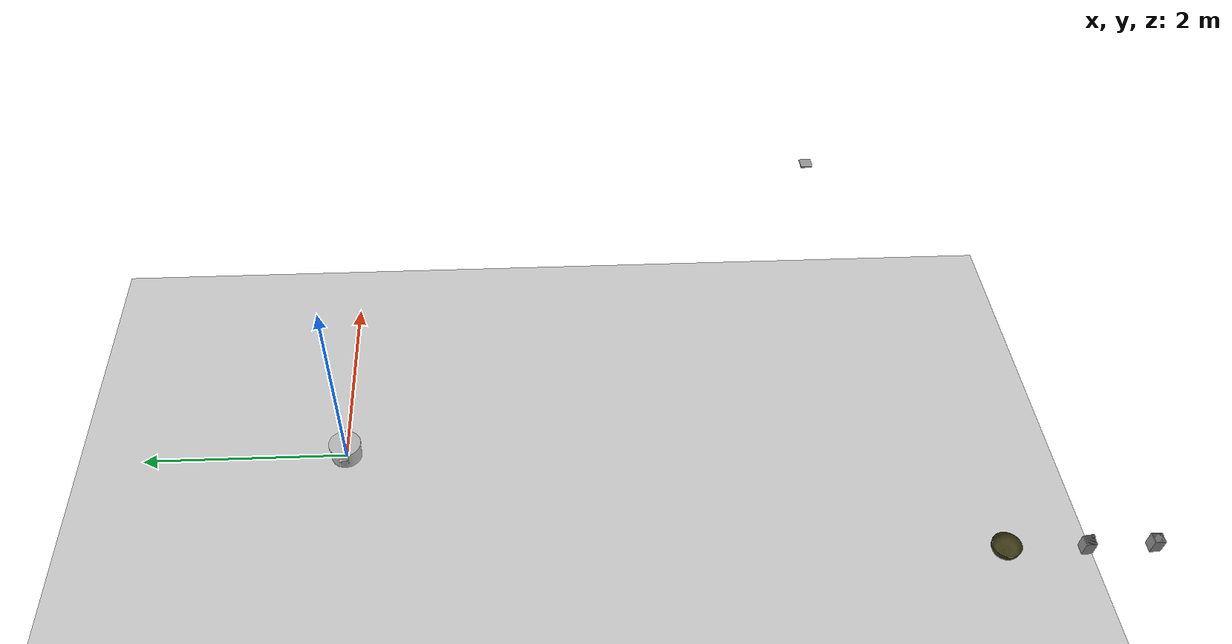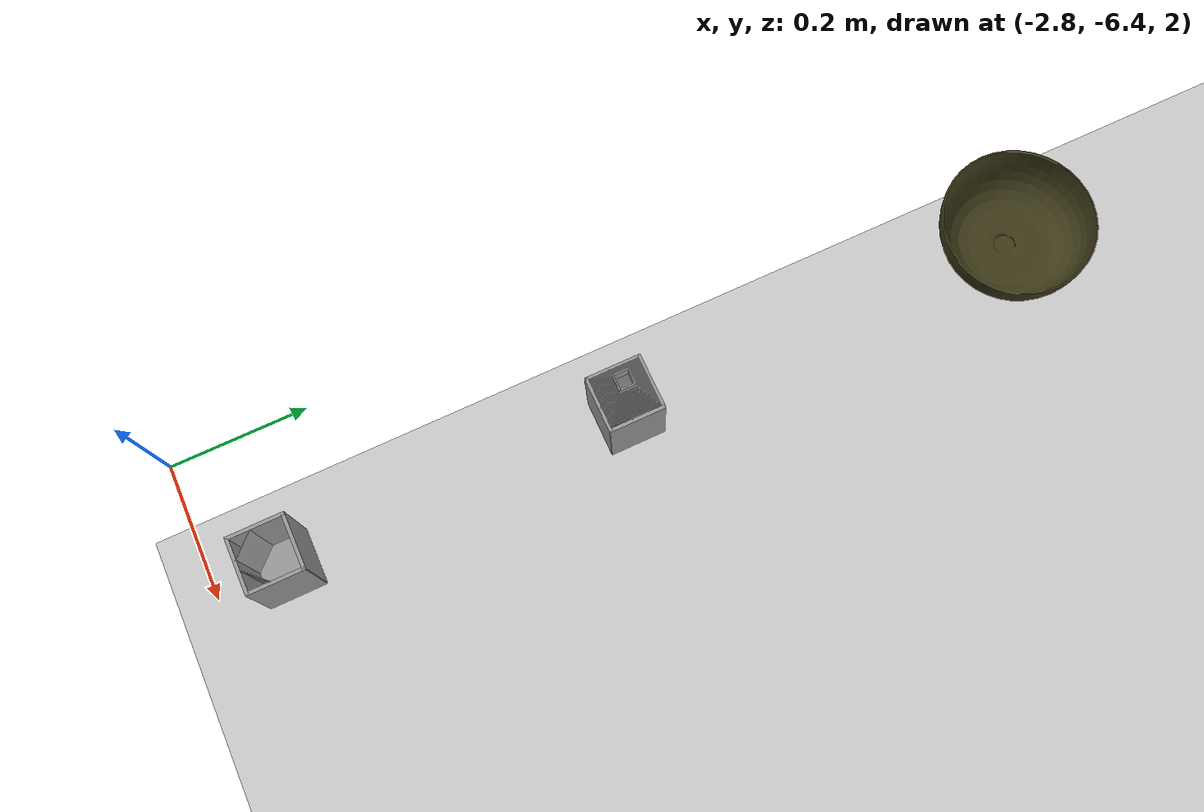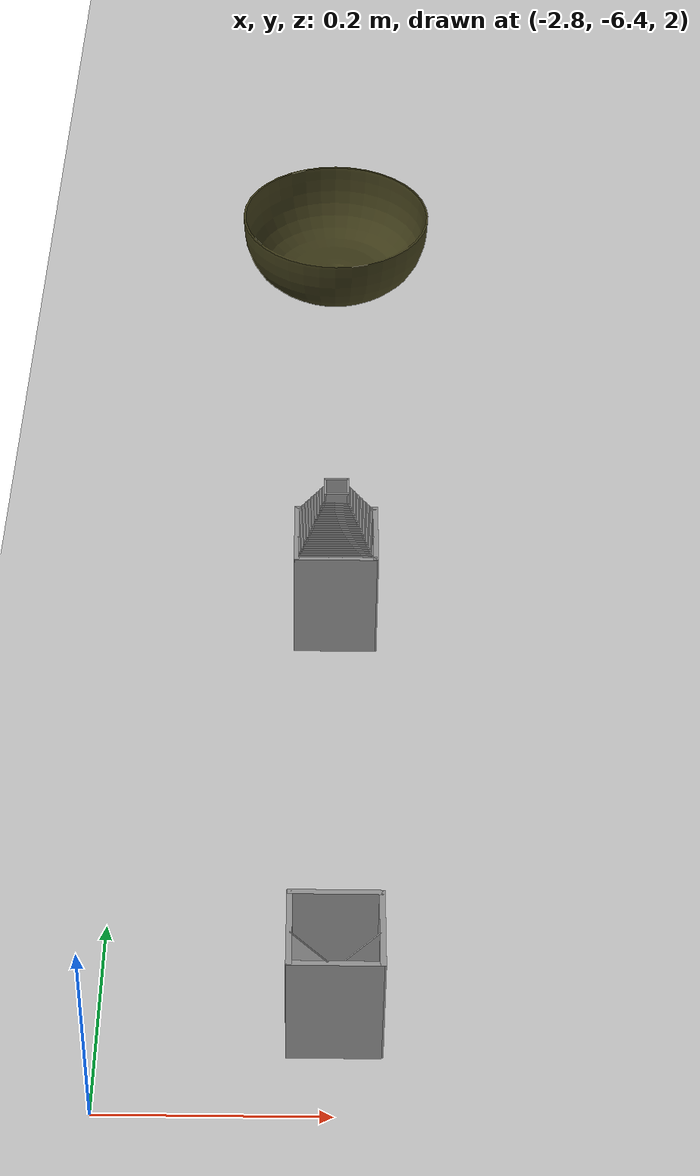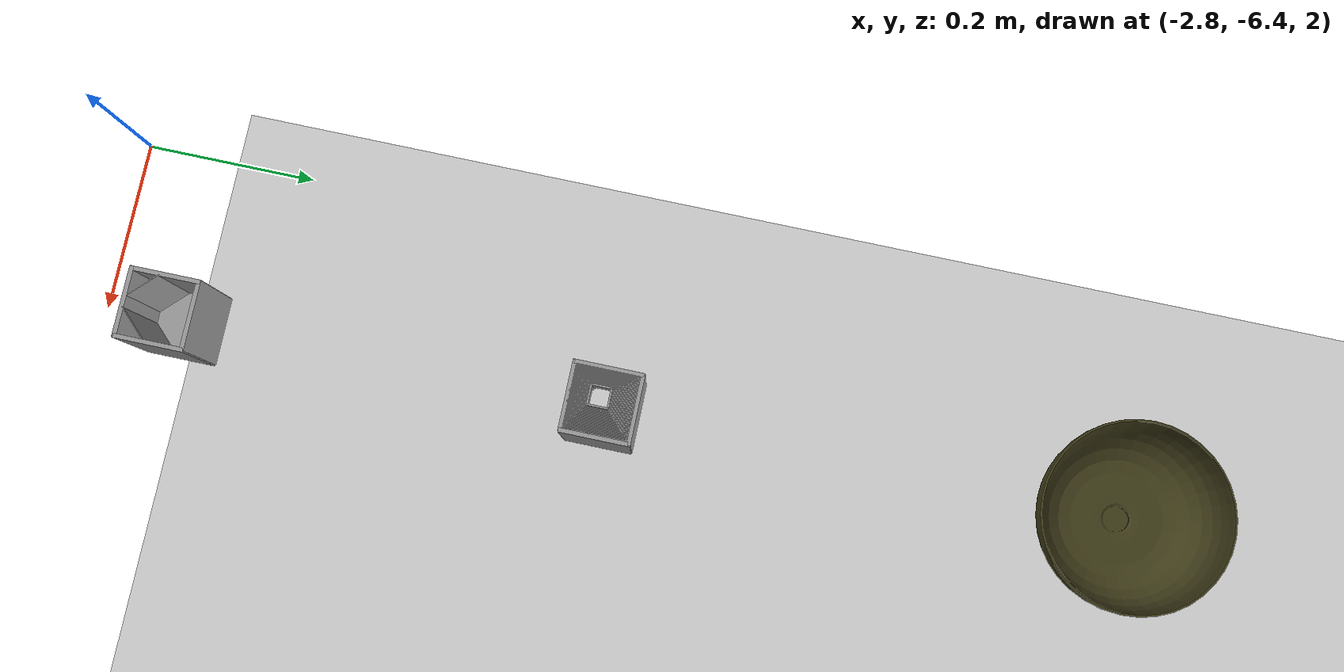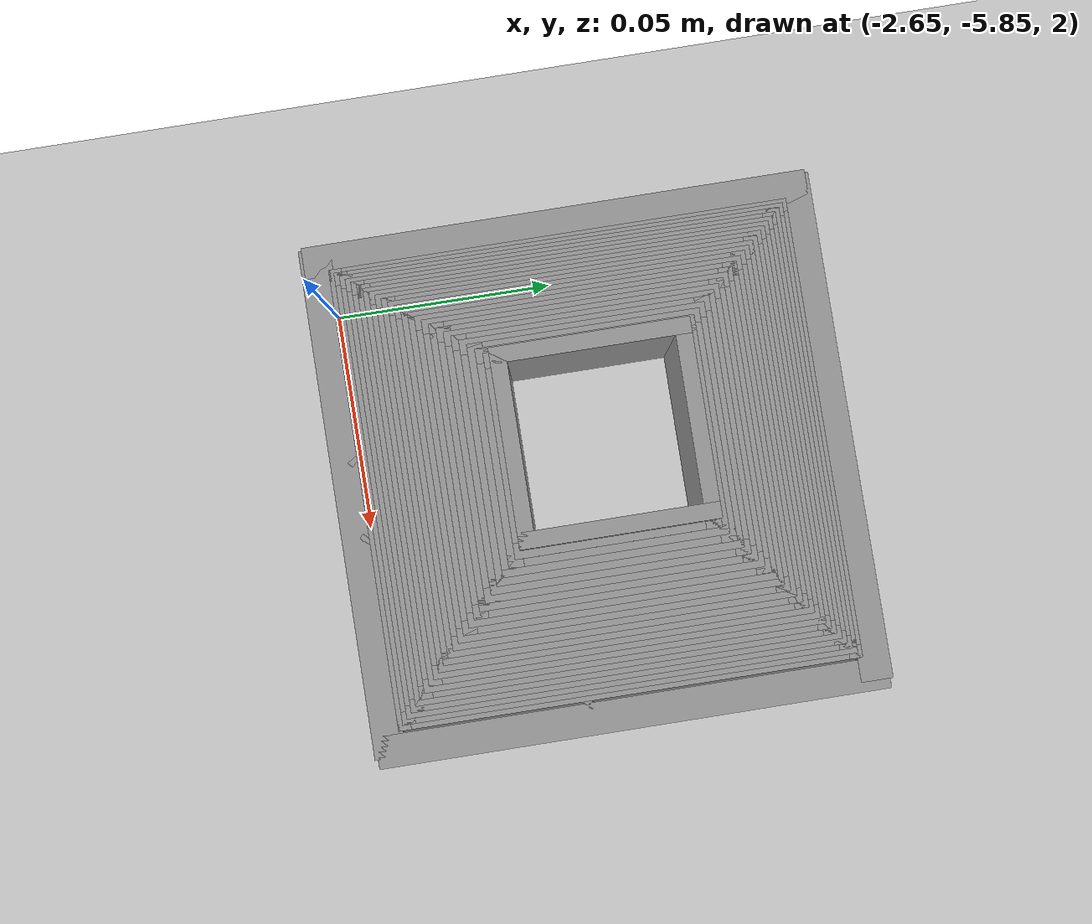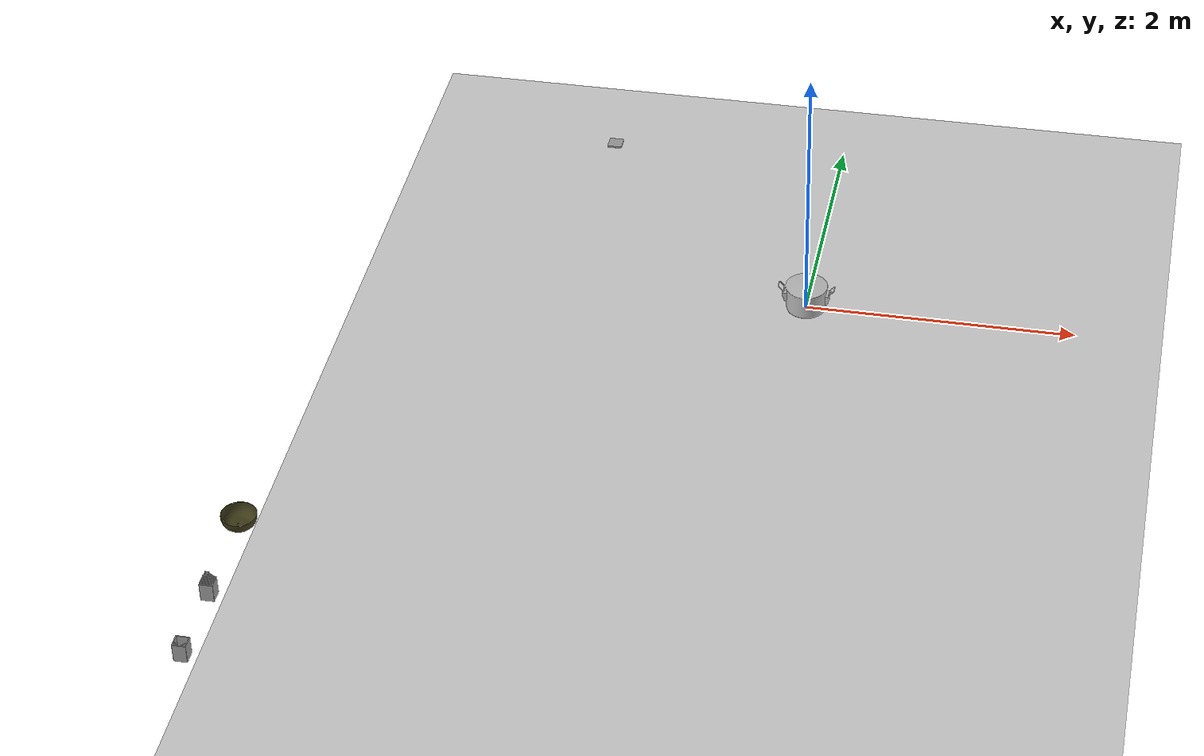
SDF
<sdf version="1.4">
 <world name="default">
  <include><uri>model://ground_plane</uri></include>
  <include><uri>model://sun</uri></include>
  <include><uri>model://bottle</uri></include>
  <include><uri>model://bowl</uri></include>
  <include><uri>model://mug</uri></include>
  <include><uri>model://pot</uri></include>
 </world>
</sdf>

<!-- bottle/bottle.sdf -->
<sdf version="1.4">
    <model name="bottle">
        <pose>-2.600000 -5.800000 2.000000 0.000000 -0.000000 0.000000</pose>
        <link name="bottle_link">
            <pose>0.000000 0.000000 0.000000 0.000000 -0.000000 0.000000</pose>
            <inertial>
                <pose>0.000125 -0.005375 0.046250 0.000000 -0.000000 0.000000</pose>
                <inertia>
                    <ixx>0.000334</ixx>
                    <ixy>0.000000</ixy>
                    <ixz>-0.000001</ixz>
                    <iyy>0.000303</iyy>
                    <iyz>0.000026</iyz>
                    <izz>0.000165</izz>
                </inertia>
                <mass>0.0080000</mass>
            </inertial>
            <collision name="bottle_bottom_collision">
                <pose>0.000000 0.000000 0.005000 0.000000 -0.000000 0.000000</pose>
                <geometry>
                    <box>
                        <size>0.080000 0.080000 0.010000</size>
                    </box>
                </geometry>
                <surface>
                    <friction>
                        <ode>
                            <mu>0.1</mu>
                            <mu2>0.1</mu2>
                            <fdir1>0.000000 0.000000 0.000000</fdir1>
                            <slip1>10.0</slip1>
                            <slip2>10.0</slip2>
                        </ode>
                    </friction>
                    <bounce>
                        <restitution_coefficient>0.000000</restitution_coefficient>
                        <threshold>100000.000000</threshold>
                    </bounce>
                    <contact>
                        <ode>
                            <soft_cfm>0.0</soft_cfm>
                            <soft_erp>0.0</soft_erp>
                            <kp>1000000000000.0</kp>
                            <kd>10000000000000000000.0</kd>
                            <max_vel>100.000000</max_vel>
                            <min_depth>0.001000</min_depth>
                        </ode>
                    </contact>
                </surface>
                <laser_retro>0.000000</laser_retro>
            </collision>
            <visual name="bottle_bottom_visual">
                <pose>2.000000 2.000000 2.005000 0.000000 -0.000000 0.000000</pose>
                <geometry>
                    <box>
                        <size>0.080000 0.080000 0.010000</size>
                    </box>
                </geometry>
                <material>
                    <script>
                        <uri>file://media/materials/scripts/gazebo.material</uri>
                        <name>Gazebo/Grey</name>
                    </script>
                </material>
                <cast_shadows>1</cast_shadows>
                <laser_retro>0.000000</laser_retro>
                <transparency>0.000000</transparency>
            </visual>
            <collision name="bottle_north_side_collision">
                <pose>0.039000 0.000000 0.060000 0.000000 -0.000000 0.000000</pose>
                <geometry>
                    <box>
                        <size>0.005000 0.080000 0.120000</size>
                    </box>
                </geometry>
                <surface>
                    <friction>
                        <ode>
                            <mu>0.1</mu>
                            <mu2>0.1</mu2>
                            <fdir1>0.000000 0.000000 0.000000</fdir1>
                            <slip1>10.0</slip1>
                            <slip2>10.0</slip2>
                        </ode>
                    </friction>
                    <bounce>
                        <restitution_coefficient>0.000000</restitution_coefficient>
                        <threshold>100000.000000</threshold>
                    </bounce>
                    <contact>
                        <ode>
                            <soft_cfm>0.0</soft_cfm>
                            <soft_erp>0.0</soft_erp>
                            <kp>1000000000000.0</kp>
                            <kd>10000000000000000000.0</kd>
                            <max_vel>100.000000</max_vel>
                            <min_depth>0.001000</min_depth>
                        </ode>
                    </contact>
                </surface>
                <laser_retro>0.000000</laser_retro>
            </collision>
            <visual name="bottle_north_side_visual">
                <pose>0.039000 0.000000 0.060000 0.000000 -0.000000 0.000000</pose>
                <geometry>
                    <box>
                        <size>0.005000 0.080000 0.120000</size>
                    </box>
                </geometry>
                <material>
                    <script>
                        <uri>file://media/materials/scripts/gazebo.material</uri>
                        <name>Gazebo/Grey</name>
                    </script>
                </material>
                <cast_shadows>1</cast_shadows>
                <laser_retro>0.000000</laser_retro>
                <transparency>0.000000</transparency>
            </visual>
            <collision name="bottle_north_side_help">
                <pose>0.021500 -0.021500 0.060000 0.000000 0.000000 -0.785398</pose>
                <geometry>
                    <box>
                        <size>0.001000 0.045000 0.120000</size>
                    </box>
                </geometry>
                <surface>
                    <friction>
                        <ode>
                            <mu>0.1</mu>
                            <mu2>0.1</mu2>
                            <fdir1>0.000000 0.000000 0.000000</fdir1>
                            <slip1>10.0</slip1>
                            <slip2>10.0</slip2>
                        </ode>
                    </friction>
                    <bounce>
                        <restitution_coefficient>0.000000</restitution_coefficient>
                        <threshold>100000.000000</threshold>
                    </bounce>
                    <contact>
                        <ode>
                            <soft_cfm>0.0</soft_cfm>
                            <soft_erp>0.0</soft_erp>
                            <kp>1000000000000.0</kp>
                            <kd>10000000000000000000.0</kd>
                            <max_vel>100.000000</max_vel>
                            <min_depth>0.001000</min_depth>
                        </ode>
                    </contact>
                </surface>
                <laser_retro>0.000000</laser_retro>
            </collision>
            <visual name="bottle_north_side_help_visual">
                <pose>0.021500 -0.021500 0.060000 0.000000 0.000000 -0.785398</pose>
                <geometry>
                    <box>
                        <size>0.001000 0.045000 0.120000</size>
                    </box>
                </geometry>
                <material>
                    <script>
                        <uri>file://media/materials/scripts/gazebo.material</uri>
                        <name>Gazebo/Grey</name>
                    </script>
                </material>
                <cast_shadows>1</cast_shadows>
                <laser_retro>0.000000</laser_retro>
                <transparency>0.000000</transparency>
            </visual>
            <collision name="bottle_east_side_collision">
                <pose>0.000000 0.038000 0.060000 0.000000 -0.000000 0.000000</pose>
                <geometry>
                    <box>
                        <size>0.080000 0.005000 0.120000</size>
                    </box>
                </geometry>
                <surface>
                    <friction>
                        <ode>
                            <mu>0.1</mu>
                            <mu2>0.1</mu2>
                            <fdir1>0.000000 0.000000 0.000000</fdir1>
                            <slip1>10.0</slip1>
                            <slip2>10.0</slip2>
                        </ode>
                    </friction>
                    <bounce>
                        <restitution_coefficient>0.000000</restitution_coefficient>
                        <threshold>100000.000000</threshold>
                    </bounce>
                    <contact>
                        <ode>
                            <soft_cfm>0.0</soft_cfm>
                            <soft_erp>0.0</soft_erp>
                            <kp>1000000000000.0</kp>
                            <kd>10000000000000000000.0</kd>
                            <max_vel>100.000000</max_vel>
                            <min_depth>0.001000</min_depth>
                        </ode>
                    </contact>
                </surface>
                <laser_retro>0.000000</laser_retro>
            </collision>
            <visual name="bottle_east_side_visual">
                <pose>0.000000 0.038000 0.060000 0.000000 -0.000000 0.000000</pose>
                <geometry>
                    <box>
                        <size>0.080000 0.005000 0.120000</size>
                    </box>
                </geometry>
                <material>
                    <script>
                        <uri>file://media/materials/scripts/gazebo.material</uri>
                        <name>Gazebo/Grey</name>
                    </script>
                </material>
                <cast_shadows>1</cast_shadows>
                <laser_retro>0.000000</laser_retro>
                <transparency>0.000000</transparency>
            </visual>
            <collision name="bottle_south_side_collision">
                <pose>-0.038000 0.000000 0.060000 0.000000 -0.000000 0.000000</pose>
                <geometry>
                    <box>
                        <size>0.005000 0.080000 0.120000</size>
                    </box>
                </geometry>
                <surface>
                    <friction>
                        <ode>
                            <mu>0.1</mu>
                            <mu2>0.1</mu2>
                            <fdir1>0.000000 0.000000 0.000000</fdir1>
                            <slip1>10.0</slip1>
                            <slip2>10.0</slip2>
                        </ode>
                    </friction>
                    <bounce>
                        <restitution_coefficient>0.000000</restitution_coefficient>
                        <threshold>100000.000000</threshold>
                    </bounce>
                    <contact>
                        <ode>
                            <soft_cfm>0.0</soft_cfm>
                            <soft_erp>0.0</soft_erp>
                            <kp>1000000000000.0</kp>
                            <kd>10000000000000000000.0</kd>
                            <max_vel>100.000000</max_vel>
                            <min_depth>0.001000</min_depth>
                        </ode>
                    </contact>
                </surface>
                <laser_retro>0.000000</laser_retro>
            </collision>
            <visual name="bottle_south_side_visual">
                <pose>-0.038000 0.000000 0.060000 0.000000 -0.000000 0.000000</pose>
                <geometry>
                    <box>
                        <size>0.005000 0.080000 0.120000</size>
                    </box>
                </geometry>
                <material>
                    <script>
                        <uri>file://media/materials/scripts/gazebo.material</uri>
                        <name>Gazebo/Grey</name>
                    </script>
                </material>
                <cast_shadows>1</cast_shadows>
                <laser_retro>0.000000</laser_retro>
                <transparency>0.000000</transparency>
            </visual>
            <collision name="bottle_south_side_help">
                <pose>-0.021500 -0.021500 0.060000 0.000000 -0.000000 0.785398</pose>
                <geometry>
                    <box>
                        <size>0.001000 0.045000 0.120000</size>
                    </box>
                </geometry>
                <surface>
                    <friction>
                        <ode>
                            <mu>0.1</mu>
                            <mu2>0.1</mu2>
                            <fdir1>0.000000 0.000000 0.000000</fdir1>
                            <slip1>10.0</slip1>
                            <slip2>10.0</slip2>
                        </ode>
                    </friction>
                    <bounce>
                        <restitution_coefficient>0.000000</restitution_coefficient>
                        <threshold>100000.000000</threshold>
                    </bounce>
                    <contact>
                        <ode>
                            <soft_cfm>0.0</soft_cfm>
                            <soft_erp>0.0</soft_erp>
                            <kp>1000000000000.0</kp>
                            <kd>10000000000000000000.0</kd>
                            <max_vel>100.000000</max_vel>
                            <min_depth>0.001000</min_depth>
                        </ode>
                    </contact>
                </surface>
                <laser_retro>0.000000</laser_retro>
            </collision>
            <visual name="bottle_south_side_help_visual">
                <pose>-0.021500 -0.021500 0.060000 0.000000 -0.000000 0.785398</pose>
                <geometry>
                    <box>
                        <size>0.001000 0.045000 0.120000</size>
                    </box>
                </geometry>
                <material>
                    <script>
                        <uri>file://media/materials/scripts/gazebo.material</uri>
                        <name>Gazebo/Grey</name>
                    </script>
                </material>
                <cast_shadows>1</cast_shadows>
                <laser_retro>0.000000</laser_retro>
                <transparency>0.000000</transparency>
            </visual>
            <collision name="bottle_west_side_collision">
                <pose>0.000000 -0.038000 0.060000 0.000000 -0.000000 0.000000</pose>
                <geometry>
                    <box>
                        <size>0.080000 0.005000 0.120000</size>
                    </box>
                </geometry>
                <surface>
                    <friction>
                        <ode>
                            <mu>0.1</mu>
                            <mu2>0.1</mu2>
                            <fdir1>0.000000 0.000000 0.000000</fdir1>
                            <slip1>10.0</slip1>
                            <slip2>10.0</slip2>
                        </ode>
                    </friction>
                    <bounce>
                        <restitution_coefficient>0.000000</restitution_coefficient>
                        <threshold>100000.000000</threshold>
                    </bounce>
                    <contact>
                        <ode>
                            <soft_cfm>0.0</soft_cfm>
                            <soft_erp>0.0</soft_erp>
                            <kp>1000000000000.0</kp>
                            <kd>10000000000000000000.0</kd>
                            <max_vel>100.000000</max_vel>
                            <min_depth>0.001000</min_depth>
                        </ode>
                    </contact>
                </surface>
                <laser_retro>0.000000</laser_retro>
            </collision>
            <visual name="bottle_west_side_visual">
                <pose>0.000000 -0.038000 0.060000 0.000000 -0.000000 0.000000</pose>
                <geometry>
                    <box>
                        <size>0.080000 0.005000 0.120000</size>
                    </box>
                </geometry>
                <material>
                    <script>
                        <uri>file://media/materials/scripts/gazebo.material</uri>
                        <name>Gazebo/Grey</name>
                    </script>
                </material>
                <cast_shadows>1</cast_shadows>
                <laser_retro>0.000000</laser_retro>
                <transparency>0.000000</transparency>
            </visual>
            <!-- BOTTLE WALLS STARTING -->
            <!-- LEVEL 1 -->
            <collision name="bottle_north_l1_collision">
                <pose>0.035 0 0.121 0 0 0</pose>
                <geometry>
                    <box>
                        <size>0.002 0.072 0.002</size>
                    </box>
                </geometry>
                <surface>
                    <friction>
                        <ode>
                            <mu>0.1</mu>
                            <mu2>0.1</mu2>
                            <fdir1>0.000000 0.000000 0.000000</fdir1>
                            <slip1>10.0</slip1>
                            <slip2>10.0</slip2>
                        </ode>
                    </friction>
                    <bounce>
                        <restitution_coefficient>0.000000</restitution_coefficient>
                        <threshold>100000.000000</threshold>
                    </bounce>
                    <contact>
                        <ode>
                            <soft_cfm>0.0</soft_cfm>
                            <soft_erp>0.0</soft_erp>
                            <kp>1000000000000.0</kp>
                            <kd>10000000000000000000.0</kd>
                            <max_vel>100.000000</max_vel>
                            <min_depth>0.001000</min_depth>
                        </ode>
                    </contact>
                </surface>
                <laser_retro>0.000000</laser_retro>
            </collision>
            <visual name="bottle_north_l1_visual">
                <pose>0.035 0 0.121 0 0 0</pose>
                <geometry>
                    <box>
                        <size>0.002 0.072 0.002</size>
                    </box>
                </geometry>
                <material>
                    <script>
                        <uri>file://media/materials/scripts/gazebo.material</uri>
                        <name>Gazebo/Grey</name>
                    </script>
                </material>
                <cast_shadows>1</cast_shadows>
                <laser_retro>0.000000</laser_retro>
                <transparency>0.000000</transparency>
            </visual>
            <collision name="bottle_south_l1_collision">
                <pose>-0.035 0 0.121 0 0 0</pose>
                <geometry>
                    <box>
                        <size>0.002 0.072 0.002</size>
                    </box>
                </geometry>
                <surface>
                    <friction>
                        <ode>
                            <mu>0.1</mu>
                            <mu2>0.1</mu2>
                            <fdir1>0.000000 0.000000 0.000000</fdir1>
                            <slip1>10.0</slip1>
                            <slip2>10.0</slip2>
                        </ode>
                    </friction>
                    <bounce>
                        <restitution_coefficient>0.000000</restitution_coefficient>
                        <threshold>100000.000000</threshold>
                    </bounce>
                    <contact>
                        <ode>
                            <soft_cfm>0.0</soft_cfm>
                            <soft_erp>0.0</soft_erp>
                            <kp>1000000000000.0</kp>
                            <kd>10000000000000000000.0</kd>
                            <max_vel>100.000000</max_vel>
                            <min_depth>0.001000</min_depth>
                        </ode>
                    </contact>
                </surface>
                <laser_retro>0.000000</laser_retro>
            </collision>
            <visual name="bottle_south_l1_visual">
                <pose>-0.035 0 0.121 0 0 0</pose>
                <geometry>
                    <box>
                        <size>0.002 0.072 0.002</size>
                    </box>
                </geometry>
                <material>
                    <script>
                        <uri>file://media/materials/scripts/gazebo.material</uri>
                        <name>Gazebo/Grey</name>
                    </script>
                </material>
                <cast_shadows>1</cast_shadows>
                <laser_retro>0.000000</laser_retro>
                <transparency>0.000000</transparency>
            </visual>
            <collision name="bottle_east_l1_collision">
                <pose>0 0.035 0.121 0 0 0</pose>
                <geometry>
                    <box>
                        <size>0.072 0.002 0.002</size>
                    </box>
                </geometry>
                <surface>
                    <friction>
                        <ode>
                            <mu>0.1</mu>
                            <mu2>0.1</mu2>
                            <fdir1>0.000000 0.000000 0.000000</fdir1>
                            <slip1>10.0</slip1>
                            <slip2>10.0</slip2>
                        </ode>
                    </friction>
                    <bounce>
                        <restitution_coefficient>0.000000</restitution_coefficient>
                        <threshold>100000.000000</threshold>
                    </bounce>
                    <contact>
                        <ode>
                            <soft_cfm>0.0</soft_cfm>
                            <soft_erp>0.0</soft_erp>
                            <kp>1000000000000.0</kp>
                            <kd>10000000000000000000.0</kd>
                            <max_vel>100.000000</max_vel>
                            <min_depth>0.001000</min_depth>
                        </ode>
                    </contact>
                </surface>
                <laser_retro>0.000000</laser_retro>
            </collision>
            <visual name="bottle_east_l1_visual">
                <pose>0 0.035 0.121 0 0 0</pose>
                <geometry>
                    <box>
                        <size>0.072 0.002 0.002</size>
                    </box>
                </geometry>
                <material>
                    <script>
                        <uri>file://media/materials/scripts/gazebo.material</uri>
                        <name>Gazebo/Grey</name>
                    </script>
                </material>
                <cast_shadows>1</cast_shadows>
                <laser_retro>0.000000</laser_retro>
                <transparency>0.000000</transparency>
            </visual>
            <collision name="bottle_west_l1_collision">
                <pose>0 -0.035 0.121 0 0 0</pose>
                <geometry>
                    <box>
                        <size>0.072 0.002 0.002</size>
                    </box>
                </geometry>
                <surface>
                    <friction>
                        <ode>
                            <mu>0.1</mu>
                            <mu2>0.1</mu2>
                            <fdir1>0.000000 0.000000 0.000000</fdir1>
                            <slip1>10.0</slip1>
                            <slip2>10.0</slip2>
                        </ode>
                    </friction>
                    <bounce>
                        <restitution_coefficient>0.000000</restitution_coefficient>
                        <threshold>100000.000000</threshold>
                    </bounce>
                    <contact>
                        <ode>
                            <soft_cfm>0.0</soft_cfm>
                            <soft_erp>0.0</soft_erp>
                            <kp>1000000000000.0</kp>
                            <kd>10000000000000000000.0</kd>
                            <max_vel>100.000000</max_vel>
                            <min_depth>0.001000</min_depth>
                        </ode>
                    </contact>
                </surface>
                <laser_retro>0.000000</laser_retro>
            </collision>
            <visual name="bottle_west_l1_visual">
                <pose>0 -0.035 0.121 0 0 0</pose>
                <geometry>
                    <box>
                        <size>0.072 0.002 0.002</size>
                    </box>
                </geometry>
                <material>
                    <script>
                        <uri>file://media/materials/scripts/gazebo.material</uri>
                        <name>Gazebo/Grey</name>
                    </script>
                </material>
                <cast_shadows>1</cast_shadows>
                <laser_retro>0.000000</laser_retro>
                <transparency>0.000000</transparency>
            </visual>
            <!-- LEVEL 2 -->
            <collision name="bottle_north_l2_collision">
                <pose>0.034 0 0.123 0 0 0</pose>
                <geometry>
                    <box>
                        <size>0.002 0.070 0.002</size>
                    </box>
                </geometry>
                <surface>
                    <friction>
                        <ode>
                            <mu>0.1</mu>
                            <mu2>0.1</mu2>
                            <fdir1>0.000000 0.000000 0.000000</fdir1>
                            <slip1>10.0</slip1>
                            <slip2>10.0</slip2>
                        </ode>
                    </friction>
                    <bounce>
                        <restitution_coefficient>0.000000</restitution_coefficient>
                        <threshold>100000.000000</threshold>
                    </bounce>
                    <contact>
                        <ode>
                            <soft_cfm>0.0</soft_cfm>
                            <soft_erp>0.0</soft_erp>
                            <kp>1000000000000.0</kp>
                            <kd>10000000000000000000.0</kd>
                            <max_vel>100.000000</max_vel>
                            <min_depth>0.001000</min_depth>
                        </ode>
                    </contact>
                </surface>
                <laser_retro>0.000000</laser_retro>
            </collision>
            <visual name="bottle_north_l2_visual">
                <pose>0.034 0 0.123 0 0 0</pose>
                <geometry>
                    <box>
                        <size>0.002 0.070 0.002</size>
                    </box>
                </geometry>
                <material>
                    <script>
                        <uri>file://media/materials/scripts/gazebo.material</uri>
                        <name>Gazebo/Grey</name>
                    </script>
                </material>
                <cast_shadows>1</cast_shadows>
                <laser_retro>0.000000</laser_retro>
                <transparency>0.000000</transparency>
            </visual>
            <collision name="bottle_south_l2_collision">
                <pose>-0.034 0 0.123 0 0 0</pose>
                <geometry>
                    <box>
                        <size>0.002 0.070 0.002</size>
                    </box>
                </geometry>
                <surface>
                    <friction>
                        <ode>
                            <mu>0.1</mu>
                            <mu2>0.1</mu2>
                            <fdir1>0.000000 0.000000 0.000000</fdir1>
                            <slip1>10.0</slip1>
                            <slip2>10.0</slip2>
                        </ode>
                    </friction>
                    <bounce>
                        <restitution_coefficient>0.000000</restitution_coefficient>
                        <threshold>100000.000000</threshold>
                    </bounce>
                    <contact>
                        <ode>
                            <soft_cfm>0.0</soft_cfm>
                            <soft_erp>0.0</soft_erp>
                            <kp>1000000000000.0</kp>
                            <kd>10000000000000000000.0</kd>
                            <max_vel>100.000000</max_vel>
                            <min_depth>0.001000</min_depth>
                        </ode>
                    </contact>
                </surface>
                <laser_retro>0.000000</laser_retro>
            </collision>
            <visual name="bottle_south_l2_visual">
                <pose>-0.034 0 0.123 0 0 0</pose>
                <geometry>
                    <box>
                        <size>0.002 0.070 0.002</size>
                    </box>
                </geometry>
                <material>
                    <script>
                        <uri>file://media/materials/scripts/gazebo.material</uri>
                        <name>Gazebo/Grey</name>
                    </script>
                </material>
                <cast_shadows>1</cast_shadows>
                <laser_retro>0.000000</laser_retro>
                <transparency>0.000000</transparency>
            </visual>
            <collision name="bottle_east_l2_collision">
                <pose>0 0.034 0.123 0 0 0</pose>
                <geometry>
                    <box>
                        <size>0.070 0.002 0.002</size>
                    </box>
                </geometry>
                <surface>
                    <friction>
                        <ode>
                            <mu>0.1</mu>
                            <mu2>0.1</mu2>
                            <fdir1>0.000000 0.000000 0.000000</fdir1>
                            <slip1>10.0</slip1>
                            <slip2>10.0</slip2>
                        </ode>
                    </friction>
                    <bounce>
                        <restitution_coefficient>0.000000</restitution_coefficient>
                        <threshold>100000.000000</threshold>
                    </bounce>
                    <contact>
                        <ode>
                            <soft_cfm>0.0</soft_cfm>
                            <soft_erp>0.0</soft_erp>
                            <kp>1000000000000.0</kp>
                            <kd>10000000000000000000.0</kd>
                            <max_vel>100.000000</max_vel>
                            <min_depth>0.001000</min_depth>
                        </ode>
                    </contact>
                </surface>
                <laser_retro>0.000000</laser_retro>
            </collision>
            <visual name="bottle_east_l2_visual">
                <pose>0 0.034 0.123 0 0 0</pose>
                <geometry>
                    <box>
                        <size>0.070 0.002 0.002</size>
                    </box>
                </geometry>
                <material>
                    <script>
                        <uri>file://media/materials/scripts/gazebo.material</uri>
                        <name>Gazebo/Grey</name>
                    </script>
                </material>
                <cast_shadows>1</cast_shadows>
                <laser_retro>0.000000</laser_retro>
                <transparency>0.000000</transparency>
            </visual>
            <collision name="bottle_west_l2_collision">
                <pose>0 -0.034 0.123 0 0 0</pose>
                <geometry>
                    <box>
                        <size>0.070 0.002 0.002</size>
                    </box>
                </geometry>
                <surface>
                    <friction>
                        <ode>
                            <mu>0.1</mu>
                            <mu2>0.1</mu2>
                            <fdir1>0.000000 0.000000 0.000000</fdir1>
                            <slip1>10.0</slip1>
                            <slip2>10.0</slip2>
                        </ode>
                    </friction>
                    <bounce>
                        <restitution_coefficient>0.000000</restitution_coefficient>
                        <threshold>100000.000000</threshold>
                    </bounce>
                    <contact>
                        <ode>
                            <soft_cfm>0.0</soft_cfm>
                            <soft_erp>0.0</soft_erp>
                            <kp>1000000000000.0</kp>
                            <kd>10000000000000000000.0</kd>
                            <max_vel>100.000000</max_vel>
                            <min_depth>0.001000</min_depth>
                        </ode>
                    </contact>
                </surface>
                <laser_retro>0.000000</laser_retro>
            </collision>
            <visual name="bottle_west_l2_visual">
                <pose>0 -0.034 0.123 0 0 0</pose>
                <geometry>
                    <box>
                        <size>0.070 0.002 0.002</size>
                    </box>
                </geometry>
                <material>
                    <script>
                        <uri>file://media/materials/scripts/gazebo.material</uri>
                        <name>Gazebo/Grey</name>
                    </script>
                </material>
                <cast_shadows>1</cast_shadows>
                <laser_retro>0.000000</laser_retro>
                <transparency>0.000000</transparency>
            </visual>
            <!-- LEVEL 3 -->
            <collision name="bottle_north_l3_collision">
                <pose>0.033 0 0.125 0 0 0</pose>
                <geometry>
                    <box>
                        <size>0.002 0.068 0.002</size>
                    </box>
                </geometry>
                <surface>
                    <friction>
                        <ode>
                            <mu>0.1</mu>
                            <mu2>0.1</mu2>
                            <fdir1>0.000000 0.000000 0.000000</fdir1>
                            <slip1>10.0</slip1>
                            <slip2>10.0</slip2>
                        </ode>
                    </friction>
                    <bounce>
                        <restitution_coefficient>0.000000</restitution_coefficient>
                        <threshold>100000.000000</threshold>
                    </bounce>
                    <contact>
                        <ode>
                            <soft_cfm>0.0</soft_cfm>
                            <soft_erp>0.0</soft_erp>
                            <kp>1000000000000.0</kp>
                            <kd>10000000000000000000.0</kd>
                            <max_vel>100.000000</max_vel>
                            <min_depth>0.001000</min_depth>
                        </ode>
                    </contact>
                </surface>
                <laser_retro>0.000000</laser_retro>
            </collision>
            <visual name="bottle_north_l3_visual">
                <pose>0.033 0 0.125 0 0 0</pose>
                <geometry>
                    <box>
                        <size>0.002 0.068 0.002</size>
                    </box>
                </geometry>
                <material>
                    <script>
                        <uri>file://media/materials/scripts/gazebo.material</uri>
                        <name>Gazebo/Grey</name>
                    </script>
                </material>
                <cast_shadows>1</cast_shadows>
                <laser_retro>0.000000</laser_retro>
                <transparency>0.000000</transparency>
            </visual>
            <collision name="bottle_south_l3_collision">
                <pose>-0.033 0 0.125 0 0 0</pose>
                <geometry>
                    <box>
                        <size>0.002 0.068 0.002</size>
                    </box>
                </geometry>
                <surface>
                    <friction>
                        <ode>
                            <mu>0.1</mu>
                            <mu2>0.1</mu2>
                            <fdir1>0.000000 0.000000 0.000000</fdir1>
                            <slip1>10.0</slip1>
                            <slip2>10.0</slip2>
                        </ode>
                    </friction>
                    <bounce>
                        <restitution_coefficient>0.000000</restitution_coefficient>
                        <threshold>100000.000000</threshold>
                    </bounce>
                    <contact>
                        <ode>
                            <soft_cfm>0.0</soft_cfm>
                            <soft_erp>0.0</soft_erp>
                            <kp>1000000000000.0</kp>
                            <kd>10000000000000000000.0</kd>
                            <max_vel>100.000000</max_vel>
                            <min_depth>0.001000</min_depth>
                        </ode>
                    </contact>
                </surface>
                <laser_retro>0.000000</laser_retro>
            </collision>
            <visual name="bottle_south_l3_visual">
                <pose>-0.033 0 0.125 0 0 0</pose>
                <geometry>
                    <box>
                        <size>0.002 0.068 0.002</size>
                    </box>
                </geometry>
                <material>
                    <script>
                        <uri>file://media/materials/scripts/gazebo.material</uri>
                        <name>Gazebo/Grey</name>
                    </script>
                </material>
                <cast_shadows>1</cast_shadows>
                <laser_retro>0.000000</laser_retro>
                <transparency>0.000000</transparency>
            </visual>
            <collision name="bottle_east_l3_collision">
                <pose>0 0.033 0.125 0 0 0</pose>
                <geometry>
                    <box>
                        <size>0.068 0.002 0.002</size>
                    </box>
                </geometry>
                <surface>
                    <friction>
                        <ode>
                            <mu>0.1</mu>
                            <mu2>0.1</mu2>
                            <fdir1>0.000000 0.000000 0.000000</fdir1>
                            <slip1>10.0</slip1>
                            <slip2>10.0</slip2>
                        </ode>
                    </friction>
                    <bounce>
                        <restitution_coefficient>0.000000</restitution_coefficient>
                        <threshold>100000.000000</threshold>
                    </bounce>
                    <contact>
                        <ode>
                            <soft_cfm>0.0</soft_cfm>
                            <soft_erp>0.0</soft_erp>
                            <kp>1000000000000.0</kp>
                            <kd>10000000000000000000.0</kd>
                            <max_vel>100.000000</max_vel>
                            <min_depth>0.001000</min_depth>
                        </ode>
                    </contact>
                </surface>
                <laser_retro>0.000000</laser_retro>
            </collision>
            <visual name="bottle_east_l3_visual">
                <pose>0 0.033 0.125 0 0 0</pose>
                <geometry>
                    <box>
                        <size>0.068 0.002 0.002</size>
                    </box>
                </geometry>
                <material>
                    <script>
                        <uri>file://media/materials/scripts/gazebo.material</uri>
                        <name>Gazebo/Grey</name>
                    </script>
                </material>
                <cast_shadows>1</cast_shadows>
                <laser_retro>0.000000</laser_retro>
                <transparency>0.000000</transparency>
            </visual>
            <collision name="bottle_west_l3_collision">
                <pose>0 -0.033 0.125 0 0 0</pose>
                <geometry>
                    <box>
                        <size>0.068 0.002 0.002</size>
                    </box>
                </geometry>
                <surface>
                    <friction>
                        <ode>
                            <mu>0.1</mu>
                            <mu2>0.1</mu2>
                            <fdir1>0.000000 0.000000 0.000000</fdir1>
                            <slip1>10.0</slip1>
                            <slip2>10.0</slip2>
                        </ode>
                    </friction>
                    <bounce>
                        <restitution_coefficient>0.000000</restitution_coefficient>
                        <threshold>100000.000000</threshold>
                    </bounce>
                    <contact>
                        <ode>
                            <soft_cfm>0.0</soft_cfm>
                            <soft_erp>0.0</soft_erp>
                            <kp>1000000000000.0</kp>
                            <kd>10000000000000000000.0</kd>
                            <max_vel>100.000000</max_vel>
                            <min_depth>0.001000</min_depth>
                        </ode>
                    </contact>
                </surface>
                <laser_retro>0.000000</laser_retro>
            </collision>
            <visual name="bottle_west_l3_visual">
                <pose>0 -0.033 0.125 0 0 0</pose>
                <geometry>
                    <box>
                        <size>0.068 0.002 0.002</size>
                    </box>
                </geometry>
                <material>
                    <script>
                        <uri>file://media/materials/scripts/gazebo.material</uri>
                        <name>Gazebo/Grey</name>
                    </script>
                </material>
                <cast_shadows>1</cast_shadows>
                <laser_retro>0.000000</laser_retro>
                <transparency>0.000000</transparency>
            </visual>
            <!-- LEVEL 4 -->
            <collision name="bottle_north_l4_collision">
                <pose>0.032 0 0.127 0 0 0</pose>
                <geometry>
                    <box>
                        <size>0.002 0.066 0.002</size>
                    </box>
                </geometry>
                <surface>
                    <friction>
                        <ode>
                            <mu>0.1</mu>
                            <mu2>0.1</mu2>
                            <fdir1>0.000000 0.000000 0.000000</fdir1>
                            <slip1>10.0</slip1>
                            <slip2>10.0</slip2>
                        </ode>
                    </friction>
                    <bounce>
                        <restitution_coefficient>0.000000</restitution_coefficient>
                        <threshold>100000.000000</threshold>
                    </bounce>
                    <contact>
                        <ode>
                            <soft_cfm>0.0</soft_cfm>
                            <soft_erp>0.0</soft_erp>
                            <kp>1000000000000.0</kp>
                            <kd>10000000000000000000.0</kd>
                            <max_vel>100.000000</max_vel>
                            <min_depth>0.001000</min_depth>
                        </ode>
                    </contact>
                </surface>
                <laser_retro>0.000000</laser_retro>
            </collision>
            <visual name="bottle_north_l4_visual">
                <pose>0.032 0 0.127 0 0 0</pose>
                <geometry>
                    <box>
                        <size>0.002 0.066 0.002</size>
                    </box>
                </geometry>
                <material>
                    <script>
                        <uri>file://media/materials/scripts/gazebo.material</uri>
                        <name>Gazebo/Grey</name>
                    </script>
                </material>
                <cast_shadows>1</cast_shadows>
                <laser_retro>0.000000</laser_retro>
                <transparency>0.000000</transparency>
            </visual>
            <collision name="bottle_south_l4_collision">
                <pose>-0.032 0 0.127 0 0 0</pose>
                <geometry>
                    <box>
                        <size>0.002 0.066 0.002</size>
                    </box>
                </geometry>
                <surface>
                    <friction>
                        <ode>
                            <mu>0.1</mu>
                            <mu2>0.1</mu2>
                            <fdir1>0.000000 0.000000 0.000000</fdir1>
                            <slip1>10.0</slip1>
                            <slip2>10.0</slip2>
                        </ode>
                    </friction>
                    <bounce>
                        <restitution_coefficient>0.000000</restitution_coefficient>
                        <threshold>100000.000000</threshold>
                    </bounce>
                    <contact>
                        <ode>
                            <soft_cfm>0.0</soft_cfm>
                            <soft_erp>0.0</soft_erp>
                            <kp>1000000000000.0</kp>
                            <kd>10000000000000000000.0</kd>
                            <max_vel>100.000000</max_vel>
                            <min_depth>0.001000</min_depth>
                        </ode>
                    </contact>
                </surface>
                <laser_retro>0.000000</laser_retro>
            </collision>
            <visual name="bottle_south_l4_visual">
                <pose>-0.032 0 0.127 0 0 0</pose>
                <geometry>
                    <box>
                        <size>0.002 0.066 0.002</size>
                    </box>
                </geometry>
                <material>
                    <script>
                        <uri>file://media/materials/scripts/gazebo.material</uri>
                        <name>Gazebo/Grey</name>
                    </script>
                </material>
                <cast_shadows>1</cast_shadows>
                <laser_retro>0.000000</laser_retro>
                <transparency>0.000000</transparency>
            </visual>
            <collision name="bottle_east_l4_collision">
                <pose>0 0.032 0.127 0 0 0</pose>
                <geometry>
                    <box>
                        <size>0.066 0.002 0.002</size>
                    </box>
                </geometry>
                <surface>
                    <friction>
                        <ode>
                            <mu>0.1</mu>
                            <mu2>0.1</mu2>
                            <fdir1>0.000000 0.000000 0.000000</fdir1>
                            <slip1>10.0</slip1>
                            <slip2>10.0</slip2>
                        </ode>
                    </friction>
                    <bounce>
                        <restitution_coefficient>0.000000</restitution_coefficient>
                        <threshold>100000.000000</threshold>
                    </bounce>
                    <contact>
                        <ode>
                            <soft_cfm>0.0</soft_cfm>
                            <soft_erp>0.0</soft_erp>
                            <kp>1000000000000.0</kp>
                            <kd>10000000000000000000.0</kd>
                            <max_vel>100.000000</max_vel>
                            <min_depth>0.001000</min_depth>
                        </ode>
                    </contact>
                </surface>
                <laser_retro>0.000000</laser_retro>
            </collision>
            <visual name="bottle_east_l4_visual">
                <pose>0 0.032 0.127 0 0 0</pose>
                <geometry>
                    <box>
                        <size>0.066 0.002 0.002</size>
                    </box>
                </geometry>
                <material>
                    <script>
                        <uri>file://media/materials/scripts/gazebo.material</uri>
                        <name>Gazebo/Grey</name>
                    </script>
                </material>
                <cast_shadows>1</cast_shadows>
                <laser_retro>0.000000</laser_retro>
                <transparency>0.000000</transparency>
            </visual>
            <collision name="bottle_west_l4_collision">
                <pose>0 -0.032 0.127 0 0 0</pose>
                <geometry>
                    <box>
                        <size>0.066 0.002 0.002</size>
                    </box>
                </geometry>
                <surface>
                    <friction>
                        <ode>
                            <mu>0.1</mu>
                            <mu2>0.1</mu2>
                            <fdir1>0.000000 0.000000 0.000000</fdir1>
                            <slip1>10.0</slip1>
                            <slip2>10.0</slip2>
                        </ode>
                    </friction>
                    <bounce>
                        <restitution_coefficient>0.000000</restitution_coefficient>
                        <threshold>100000.000000</threshold>
                    </bounce>
                    <contact>
                        <ode>
                            <soft_cfm>0.0</soft_cfm>
                            <soft_erp>0.0</soft_erp>
                            <kp>1000000000000.0</kp>
                            <kd>10000000000000000000.0</kd>
                            <max_vel>100.000000</max_vel>
                            <min_depth>0.001000</min_depth>
                        </ode>
                    </contact>
                </surface>
                <laser_retro>0.000000</laser_retro>
            </collision>
            <visual name="bottle_west_l4_visual">
                <pose>0 -0.032 0.127 0 0 0</pose>
                <geometry>
                    <box>
                        <size>0.066 0.002 0.002</size>
                    </box>
                </geometry>
                <material>
                    <script>
                        <uri>file://media/materials/scripts/gazebo.material</uri>
                        <name>Gazebo/Grey</name>
                    </script>
                </material>
                <cast_shadows>1</cast_shadows>
                <laser_retro>0.000000</laser_retro>
                <transparency>0.000000</transparency>
            </visual>
            <!-- LEVEL 5 -->
            <collision name="bottle_north_l5_collision">
                <pose>0.031 0 0.129 0 0 0</pose>
                <geometry>
                    <box>
                        <size>0.002 0.064 0.002</size>
                    </box>
                </geometry>
                <surface>
                    <friction>
                        <ode>
                            <mu>0.1</mu>
                            <mu2>0.1</mu2>
                            <fdir1>0.000000 0.000000 0.000000</fdir1>
                            <slip1>10.0</slip1>
                            <slip2>10.0</slip2>
                        </ode>
                    </friction>
                    <bounce>
                        <restitution_coefficient>0.000000</restitution_coefficient>
                        <threshold>100000.000000</threshold>
                    </bounce>
                    <contact>
                        <ode>
                            <soft_cfm>0.0</soft_cfm>
                            <soft_erp>0.0</soft_erp>
                            <kp>1000000000000.0</kp>
                            <kd>10000000000000000000.0</kd>
                            <max_vel>100.000000</max_vel>
                            <min_depth>0.001000</min_depth>
                        </ode>
                    </contact>
                </surface>
                <laser_retro>0.000000</laser_retro>
            </collision>
            <visual name="bottle_north_l5_visual">
                <pose>0.031 0 0.129 0 0 0</pose>
                <geometry>
                    <box>
                        <size>0.002 0.064 0.002</size>
                    </box>
                </geometry>
                <material>
                    <script>
                        <uri>file://media/materials/scripts/gazebo.material</uri>
                        <name>Gazebo/Grey</name>
                    </script>
                </material>
                <cast_shadows>1</cast_shadows>
                <laser_retro>0.000000</laser_retro>
                <transparency>0.000000</transparency>
            </visual>
            <collision name="bottle_south_l5_collision">
                <pose>-0.031 0 0.129 0 0 0</pose>
                <geometry>
                    <box>
                        <size>0.002 0.064 0.002</size>
                    </box>
                </geometry>
                <surface>
                    <friction>
                        <ode>
                            <mu>0.1</mu>
                            <mu2>0.1</mu2>
                            <fdir1>0.000000 0.000000 0.000000</fdir1>
                            <slip1>10.0</slip1>
                            <slip2>10.0</slip2>
                        </ode>
                    </friction>
                    <bounce>
                        <restitution_coefficient>0.000000</restitution_coefficient>
                        <threshold>100000.000000</threshold>
                    </bounce>
                    <contact>
                        <ode>
                            <soft_cfm>0.0</soft_cfm>
                            <soft_erp>0.0</soft_erp>
                            <kp>1000000000000.0</kp>
                            <kd>10000000000000000000.0</kd>
                            <max_vel>100.000000</max_vel>
                            <min_depth>0.001000</min_depth>
                        </ode>
                    </contact>
                </surface>
                <laser_retro>0.000000</laser_retro>
            </collision>
            <visual name="bottle_south_l5_visual">
                <pose>-0.031 0 0.129 0 0 0</pose>
                <geometry>
                    <box>
                        <size>0.002 0.064 0.002</size>
                    </box>
                </geometry>
                <material>
                    <script>
                        <uri>file://media/materials/scripts/gazebo.material</uri>
                        <name>Gazebo/Grey</name>
                    </script>
                </material>
                <cast_shadows>1</cast_shadows>
                <laser_retro>0.000000</laser_retro>
                <transparency>0.000000</transparency>
            </visual>
            <collision name="bottle_east_l5_collision">
                <pose>0 0.031 0.129 0 0 0</pose>
                <geometry>
                    <box>
                        <size>0.064 0.002 0.002</size>
                    </box>
                </geometry>
                <surface>
                    <friction>
                        <ode>
                            <mu>0.1</mu>
                            <mu2>0.1</mu2>
                            <fdir1>0.000000 0.000000 0.000000</fdir1>
                            <slip1>10.0</slip1>
                            <slip2>10.0</slip2>
                        </ode>
                    </friction>
                    <bounce>
                        <restitution_coefficient>0.000000</restitution_coefficient>
                        <threshold>100000.000000</threshold>
                    </bounce>
                    <contact>
                        <ode>
                            <soft_cfm>0.0</soft_cfm>
                            <soft_erp>0.0</soft_erp>
                            <kp>1000000000000.0</kp>
                            <kd>10000000000000000000.0</kd>
                            <max_vel>100.000000</max_vel>
                            <min_depth>0.001000</min_depth>
                        </ode>
                    </contact>
                </surface>
                <laser_retro>0.000000</laser_retro>
            </collision>
            <visual name="bottle_east_l5_visual">
                <pose>0 0.031 0.129 0 0 0</pose>
                <geometry>
                    <box>
                        <size>0.064 0.002 0.002</size>
                    </box>
                </geometry>
                <material>
                    <script>
                        <uri>file://media/materials/scripts/gazebo.material</uri>
                        <name>Gazebo/Grey</name>
                    </script>
                </material>
                <cast_shadows>1</cast_shadows>
                <laser_retro>0.000000</laser_retro>
                <transparency>0.000000</transparency>
            </visual>
            <collision name="bottle_west_l5_collision">
                <pose>0 -0.031 0.129 0 0 0</pose>
                <geometry>
                    <box>
                        <size>0.064 0.002 0.002</size>
                    </box>
                </geometry>
                <surface>
                    <friction>
                        <ode>
                            <mu>0.1</mu>
                            <mu2>0.1</mu2>
                            <fdir1>0.000000 0.000000 0.000000</fdir1>
                            <slip1>10.0</slip1>
                            <slip2>10.0</slip2>
                        </ode>
                    </friction>
                    <bounce>
                        <restitution_coefficient>0.000000</restitution_coefficient>
                        <threshold>100000.000000</threshold>
                    </bounce>
                    <contact>
                        <ode>
                            <soft_cfm>0.0</soft_cfm>
                            <soft_erp>0.0</soft_erp>
                            <kp>1000000000000.0</kp>
                            <kd>10000000000000000000.0</kd>
                            <max_vel>100.000000</max_vel>
                            <min_depth>0.001000</min_depth>
                        </ode>
                    </contact>
                </surface>
                <laser_retro>0.000000</laser_retro>
            </collision>
            <visual name="bottle_west_l5_visual">
                <pose>0 -0.031 0.129 0 0 0</pose>
                <geometry>
                    <box>
                        <size>0.064 0.002 0.002</size>
                    </box>
                </geometry>
                <material>
                    <script>
                        <uri>file://media/materials/scripts/gazebo.material</uri>
                        <name>Gazebo/Grey</name>
                    </script>
                </material>
                <cast_shadows>1</cast_shadows>
                <laser_retro>0.000000</laser_retro>
                <transparency>0.000000</transparency>
            </visual>
            <!-- LEVEL 6 -->
            <collision name="bottle_north_l6_collision">
                <pose>0.030 0 0.131 0 0 0</pose>
                <geometry>
                    <box>
                        <size>0.002 0.062 0.002</size>
                    </box>
                </geometry>
                <surface>
                    <friction>
                        <ode>
                            <mu>0.1</mu>
                            <mu2>0.1</mu2>
                            <fdir1>0.000000 0.000000 0.000000</fdir1>
                            <slip1>10.0</slip1>
                            <slip2>10.0</slip2>
                        </ode>
                    </friction>
                    <bounce>
                        <restitution_coefficient>0.000000</restitution_coefficient>
                        <threshold>100000.000000</threshold>
                    </bounce>
                    <contact>
                        <ode>
                            <soft_cfm>0.0</soft_cfm>
                            <soft_erp>0.0</soft_erp>
                            <kp>1000000000000.0</kp>
                            <kd>10000000000000000000.0</kd>
                            <max_vel>100.000000</max_vel>
                            <min_depth>0.001000</min_depth>
                        </ode>
                    </contact>
                </surface>
                <laser_retro>0.000000</laser_retro>
            </collision>
            <visual name="bottle_north_l6_visual">
                <pose>0.030 0 0.131 0 0 0</pose>
                <geometry>
                    <box>
                        <size>0.002 0.062 0.002</size>
                    </box>
                </geometry>
                <material>
                    <script>
                        <uri>file://media/materials/scripts/gazebo.material</uri>
                        <name>Gazebo/Grey</name>
                    </script>
                </material>
                <cast_shadows>1</cast_shadows>
                <laser_retro>0.000000</laser_retro>
                <transparency>0.000000</transparency>
            </visual>
            <collision name="bottle_south_l6_collision">
                <pose>-0.030 0 0.131 0 0 0</pose>
                <geometry>
                    <box>
                        <size>0.002 0.062 0.002</size>
                    </box>
                </geometry>
                <surface>
                    <friction>
                        <ode>
                            <mu>0.1</mu>
                            <mu2>0.1</mu2>
                            <fdir1>0.000000 0.000000 0.000000</fdir1>
                            <slip1>10.0</slip1>
                            <slip2>10.0</slip2>
                        </ode>
                    </friction>
                    <bounce>
                        <restitution_coefficient>0.000000</restitution_coefficient>
                        <threshold>100000.000000</threshold>
                    </bounce>
                    <contact>
                        <ode>
                            <soft_cfm>0.0</soft_cfm>
                            <soft_erp>0.0</soft_erp>
                            <kp>1000000000000.0</kp>
                            <kd>10000000000000000000.0</kd>
                            <max_vel>100.000000</max_vel>
                            <min_depth>0.001000</min_depth>
                        </ode>
                    </contact>
                </surface>
                <laser_retro>0.000000</laser_retro>
            </collision>
            <visual name="bottle_south_l6_visual">
                <pose>-0.030 0 0.131 0 0 0</pose>
                <geometry>
                    <box>
                        <size>0.002 0.062 0.002</size>
                    </box>
                </geometry>
                <material>
                    <script>
                        <uri>file://media/materials/scripts/gazebo.material</uri>
                        <name>Gazebo/Grey</name>
                    </script>
                </material>
                <cast_shadows>1</cast_shadows>
                <laser_retro>0.000000</laser_retro>
                <transparency>0.000000</transparency>
            </visual>
            <collision name="bottle_east_l6_collision">
                <pose>0 0.030 0.131 0 0 0</pose>
                <geometry>
                    <box>
                        <size>0.062 0.002 0.002</size>
                    </box>
                </geometry>
                <surface>
                    <friction>
                        <ode>
                            <mu>0.1</mu>
                            <mu2>0.1</mu2>
                            <fdir1>0.000000 0.000000 0.000000</fdir1>
                            <slip1>10.0</slip1>
                            <slip2>10.0</slip2>
                        </ode>
                    </friction>
                    <bounce>
                        <restitution_coefficient>0.000000</restitution_coefficient>
                        <threshold>100000.000000</threshold>
                    </bounce>
                    <contact>
                        <ode>
                            <soft_cfm>0.0</soft_cfm>
                            <soft_erp>0.0</soft_erp>
                            <kp>1000000000000.0</kp>
                            <kd>10000000000000000000.0</kd>
                            <max_vel>100.000000</max_vel>
                            <min_depth>0.001000</min_depth>
                        </ode>
                    </contact>
                </surface>
                <laser_retro>0.000000</laser_retro>
            </collision>
            <visual name="bottle_east_l6_visual">
                <pose>0 0.030 0.131 0 0 0</pose>
                <geometry>
                    <box>
                        <size>0.062 0.002 0.002</size>
                    </box>
                </geometry>
                <material>
                    <script>
                        <uri>file://media/materials/scripts/gazebo.material</uri>
                        <name>Gazebo/Grey</name>
                    </script>
                </material>
                <cast_shadows>1</cast_shadows>
                <laser_retro>0.000000</laser_retro>
                <transparency>0.000000</transparency>
            </visual>
            <collision name="bottle_west_l6_collision">
                <pose>0 -0.030 0.131 0 0 0</pose>
                <geometry>
                    <box>
                        <size>0.062 0.002 0.002</size>
                    </box>
                </geometry>
                <surface>
                    <friction>
                        <ode>
                            <mu>0.1</mu>
                            <mu2>0.1</mu2>
                            <fdir1>0.000000 0.000000 0.000000</fdir1>
                            <slip1>10.0</slip1>
                            <slip2>10.0</slip2>
                        </ode>
                    </friction>
                    <bounce>
                        <restitution_coefficient>0.000000</restitution_coefficient>
                        <threshold>100000.000000</threshold>
                    </bounce>
                    <contact>
                        <ode>
                            <soft_cfm>0.0</soft_cfm>
                            <soft_erp>0.0</soft_erp>
                            <kp>1000000000000.0</kp>
                            <kd>10000000000000000000.0</kd>
                            <max_vel>100.000000</max_vel>
                            <min_depth>0.001000</min_depth>
                        </ode>
                    </contact>
                </surface>
                <laser_retro>0.000000</laser_retro>
            </collision>
            <visual name="bottle_west_l6_visual">
                <pose>0 -0.030 0.131 0 0 0</pose>
                <geometry>
                    <box>
                        <size>0.062 0.002 0.002</size>
                    </box>
                </geometry>
                <material>
                    <script>
                        <uri>file://media/materials/scripts/gazebo.material</uri>
                        <name>Gazebo/Grey</name>
                    </script>
                </material>
                <cast_shadows>1</cast_shadows>
                <laser_retro>0.000000</laser_retro>
                <transparency>0.000000</transparency>
            </visual>
            <!-- LEVEL 7 -->
            <collision name="bottle_north_l7_collision">
                <pose>0.029 0 0.133 0 0 0</pose>
                <geometry>
                    <box>
                        <size>0.002 0.060 0.002</size>
                    </box>
                </geometry>
                <surface>
                    <friction>
                        <ode>
                            <mu>0.1</mu>
                            <mu2>0.1</mu2>
                            <fdir1>0.000000 0.000000 0.000000</fdir1>
                            <slip1>10.0</slip1>
                            <slip2>10.0</slip2>
                        </ode>
                    </friction>
                    <bounce>
                        <restitution_coefficient>0.000000</restitution_coefficient>
                        <threshold>100000.000000</threshold>
                    </bounce>
                    <contact>
                        <ode>
                            <soft_cfm>0.0</soft_cfm>
                            <soft_erp>0.0</soft_erp>
                            <kp>1000000000000.0</kp>
                            <kd>10000000000000000000.0</kd>
                            <max_vel>100.000000</max_vel>
                            <min_depth>0.001000</min_depth>
                        </ode>
                    </contact>
                </surface>
                <laser_retro>0.000000</laser_retro>
            </collision>
            <visual name="bottle_north_l7_visual">
                <pose>0.029 0 0.133 0 0 0</pose>
                <geometry>
                    <box>
                        <size>0.002 0.060 0.002</size>
                    </box>
                </geometry>
                <material>
                    <script>
                        <uri>file://media/materials/scripts/gazebo.material</uri>
                        <name>Gazebo/Grey</name>
                    </script>
                </material>
                <cast_shadows>1</cast_shadows>
                <laser_retro>0.000000</laser_retro>
                <transparency>0.000000</transparency>
            </visual>
            <collision name="bottle_south_l7_collision">
                <pose>-0.029 0 0.133 0 0 0</pose>
                <geometry>
                    <box>
                        <size>0.002 0.060 0.002</size>
                    </box>
                </geometry>
                <surface>
                    <friction>
                        <ode>
                            <mu>0.1</mu>
                            <mu2>0.1</mu2>
                            <fdir1>0.000000 0.000000 0.000000</fdir1>
                            <slip1>10.0</slip1>
                            <slip2>10.0</slip2>
                        </ode>
                    </friction>
                    <bounce>
                        <restitution_coefficient>0.000000</restitution_coefficient>
                        <threshold>100000.000000</threshold>
                    </bounce>
                    <contact>
                        <ode>
                            <soft_cfm>0.0</soft_cfm>
                            <soft_erp>0.0</soft_erp>
                            <kp>1000000000000.0</kp>
                            <kd>10000000000000000000.0</kd>
                            <max_vel>100.000000</max_vel>
                            <min_depth>0.001000</min_depth>
                        </ode>
                    </contact>
                </surface>
                <laser_retro>0.000000</laser_retro>
            </collision>
            <visual name="bottle_south_l7_visual">
                <pose>-0.029 0 0.133 0 0 0</pose>
                <geometry>
                    <box>
                        <size>0.002 0.060 0.002</size>
                    </box>
                </geometry>
                <material>
                    <script>
                        <uri>file://media/materials/scripts/gazebo.material</uri>
                        <name>Gazebo/Grey</name>
                    </script>
                </material>
                <cast_shadows>1</cast_shadows>
                <laser_retro>0.000000</laser_retro>
                <transparency>0.000000</transparency>
            </visual>
            <collision name="bottle_east_l7_collision">
                <pose>0 0.029 0.133 0 0 0</pose>
                <geometry>
                    <box>
                        <size>0.060 0.002 0.002</size>
                    </box>
                </geometry>
                <surface>
                    <friction>
                        <ode>
                            <mu>0.1</mu>
                            <mu2>0.1</mu2>
                            <fdir1>0.000000 0.000000 0.000000</fdir1>
                            <slip1>10.0</slip1>
                            <slip2>10.0</slip2>
                        </ode>
                    </friction>
                    <bounce>
                        <restitution_coefficient>0.000000</restitution_coefficient>
                        <threshold>100000.000000</threshold>
                    </bounce>
                    <contact>
                        <ode>
                            <soft_cfm>0.0</soft_cfm>
                            <soft_erp>0.0</soft_erp>
                            <kp>1000000000000.0</kp>
                            <kd>10000000000000000000.0</kd>
                            <max_vel>100.000000</max_vel>
                            <min_depth>0.001000</min_depth>
                        </ode>
                    </contact>
                </surface>
                <laser_retro>0.000000</laser_retro>
            </collision>
            <visual name="bottle_east_l7_visual">
                <pose>0 0.029 0.133 0 0 0</pose>
                <geometry>
                    <box>
                        <size>0.060 0.002 0.002</size>
                    </box>
                </geometry>
                <material>
                    <script>
                        <uri>file://media/materials/scripts/gazebo.material</uri>
                        <name>Gazebo/Grey</name>
                    </script>
                </material>
                <cast_shadows>1</cast_shadows>
                <laser_retro>0.000000</laser_retro>
                <transparency>0.000000</transparency>
            </visual>
            <collision name="bottle_west_l7_collision">
                <pose>0 -0.029 0.133 0 0 0</pose>
                <geometry>
                    <box>
                        <size>0.060 0.002 0.002</size>
                    </box>
                </geometry>
                <surface>
                    <friction>
                        <ode>
                            <mu>0.1</mu>
                            <mu2>0.1</mu2>
                            <fdir1>0.000000 0.000000 0.000000</fdir1>
                            <slip1>10.0</slip1>
                            <slip2>10.0</slip2>
                        </ode>
                    </friction>
                    <bounce>
                        <restitution_coefficient>0.000000</restitution_coefficient>
                        <threshold>100000.000000</threshold>
                    </bounce>
                    <contact>
                        <ode>
                            <soft_cfm>0.0</soft_cfm>
                            <soft_erp>0.0</soft_erp>
                            <kp>1000000000000.0</kp>
                            <kd>10000000000000000000.0</kd>
                            <max_vel>100.000000</max_vel>
                            <min_depth>0.001000</min_depth>
                        </ode>
                    </contact>
                </surface>
                <laser_retro>0.000000</laser_retro>
            </collision>
            <visual name="bottle_west_l7_visual">
                <pose>0 -0.029 0.133 0 0 0</pose>
                <geometry>
                    <box>
                        <size>0.060 0.002 0.002</size>
                    </box>
                </geometry>
                <material>
                    <script>
                        <uri>file://media/materials/scripts/gazebo.material</uri>
                        <name>Gazebo/Grey</name>
                    </script>
                </material>
                <cast_shadows>1</cast_shadows>
                <laser_retro>0.000000</laser_retro>
                <transparency>0.000000</transparency>
            </visual>
            <!-- LEVEL 8 -->
            <collision name="bottle_north_l8_collision">
                <pose>0.028 0 0.135 0 0 0</pose>
                <geometry>
                    <box>
                        <size>0.002 0.058 0.002</size>
                    </box>
                </geometry>
                <surface>
                    <friction>
                        <ode>
                            <mu>0.1</mu>
                            <mu2>0.1</mu2>
                            <fdir1>0.000000 0.000000 0.000000</fdir1>
                            <slip1>10.0</slip1>
                            <slip2>10.0</slip2>
                        </ode>
                    </friction>
                    <bounce>
                        <restitution_coefficient>0.000000</restitution_coefficient>
                        <threshold>100000.000000</threshold>
                    </bounce>
                    <contact>
                        <ode>
                            <soft_cfm>0.0</soft_cfm>
                            <soft_erp>0.0</soft_erp>
                            <kp>1000000000000.0</kp>
                            <kd>10000000000000000000.0</kd>
                            <max_vel>100.000000</max_vel>
                            <min_depth>0.001000</min_depth>
                        </ode>
                    </contact>
                </surface>
                <laser_retro>0.000000</laser_retro>
            </collision>
            <visual name="bottle_north_l8_visual">
                <pose>0.028 0 0.135 0 0 0</pose>
                <geometry>
                    <box>
                        <size>0.002 0.058 0.002</size>
                    </box>
                </geometry>
                <material>
                    <script>
                        <uri>file://media/materials/scripts/gazebo.material</uri>
                        <name>Gazebo/Grey</name>
                    </script>
                </material>
                <cast_shadows>1</cast_shadows>
                <laser_retro>0.000000</laser_retro>
                <transparency>0.000000</transparency>
            </visual>
            <collision name="bottle_south_l8_collision">
                <pose>-0.028 0 0.135 0 0 0</pose>
                <geometry>
                    <box>
                        <size>0.002 0.058 0.002</size>
                    </box>
                </geometry>
                <surface>
                    <friction>
                        <ode>
                            <mu>0.1</mu>
                            <mu2>0.1</mu2>
                            <fdir1>0.000000 0.000000 0.000000</fdir1>
                            <slip1>10.0</slip1>
                            <slip2>10.0</slip2>
                        </ode>
                    </friction>
                    <bounce>
                        <restitution_coefficient>0.000000</restitution_coefficient>
                        <threshold>100000.000000</threshold>
                    </bounce>
                    <contact>
                        <ode>
                            <soft_cfm>0.0</soft_cfm>
                            <soft_erp>0.0</soft_erp>
                            <kp>1000000000000.0</kp>
                            <kd>10000000000000000000.0</kd>
                            <max_vel>100.000000</max_vel>
                            <min_depth>0.001000</min_depth>
                        </ode>
                    </contact>
                </surface>
                <laser_retro>0.000000</laser_retro>
            </collision>
            <visual name="bottle_south_l8_visual">
                <pose>-0.028 0 0.135 0 0 0</pose>
                <geometry>
                    <box>
                        <size>0.002 0.058 0.002</size>
                    </box>
                </geometry>
                <material>
                    <script>
                        <uri>file://media/materials/scripts/gazebo.material</uri>
                        <name>Gazebo/Grey</name>
                    </script>
                </material>
                <cast_shadows>1</cast_shadows>
                <laser_retro>0.000000</laser_retro>
                <transparency>0.000000</transparency>
            </visual>
            <collision name="bottle_east_l8_collision">
                <pose>0 0.028 0.135 0 0 0</pose>
                <geometry>
                    <box>
                        <size>0.058 0.002 0.002</size>
                    </box>
                </geometry>
                <surface>
                    <friction>
                        <ode>
                            <mu>0.1</mu>
                            <mu2>0.1</mu2>
                            <fdir1>0.000000 0.000000 0.000000</fdir1>
                            <slip1>10.0</slip1>
                            <slip2>10.0</slip2>
                        </ode>
                    </friction>
                    <bounce>
                        <restitution_coefficient>0.000000</restitution_coefficient>
                        <threshold>100000.000000</threshold>
                    </bounce>
                    <contact>
                        <ode>
                            <soft_cfm>0.0</soft_cfm>
                            <soft_erp>0.0</soft_erp>
                            <kp>1000000000000.0</kp>
                            <kd>10000000000000000000.0</kd>
                            <max_vel>100.000000</max_vel>
                            <min_depth>0.001000</min_depth>
                        </ode>
                    </contact>
                </surface>
                <laser_retro>0.000000</laser_retro>
            </collision>
            <visual name="bottle_east_l8_visual">
                <pose>0 0.028 0.135 0 0 0</pose>
                <geometry>
                    <box>
                        <size>0.058 0.002 0.002</size>
                    </box>
                </geometry>
                <material>
                    <script>
                        <uri>file://media/materials/scripts/gazebo.material</uri>
                        <name>Gazebo/Grey</name>
                    </script>
                </material>
                <cast_shadows>1</cast_shadows>
                <laser_retro>0.000000</laser_retro>
                <transparency>0.000000</transparency>
            </visual>
            <collision name="bottle_west_l8_collision">
                <pose>0 -0.028 0.135 0 0 0</pose>
                <geometry>
                    <box>
                        <size>0.058 0.002 0.002</size>
                    </box>
                </geometry>
                <surface>
                    <friction>
                        <ode>
                            <mu>0.1</mu>
                            <mu2>0.1</mu2>
                            <fdir1>0.000000 0.000000 0.000000</fdir1>
                            <slip1>10.0</slip1>
                            <slip2>10.0</slip2>
                        </ode>
                    </friction>
                    <bounce>
                        <restitution_coefficient>0.000000</restitution_coefficient>
                        <threshold>100000.000000</threshold>
                    </bounce>
                    <contact>
                        <ode>
                            <soft_cfm>0.0</soft_cfm>
                            <soft_erp>0.0</soft_erp>
                            <kp>1000000000000.0</kp>
                            <kd>10000000000000000000.0</kd>
                            <max_vel>100.000000</max_vel>
                            <min_depth>0.001000</min_depth>
                        </ode>
                    </contact>
                </surface>
                <laser_retro>0.000000</laser_retro>
            </collision>
            <visual name="bottle_west_l8_visual">
                <pose>0 -0.028 0.135 0 0 0</pose>
                <geometry>
                    <box>
                        <size>0.058 0.002 0.002</size>
                    </box>
                </geometry>
                <material>
                    <script>
                        <uri>file://media/materials/scripts/gazebo.material</uri>
                        <name>Gazebo/Grey</name>
                    </script>
                </material>
                <cast_shadows>1</cast_shadows>
                <laser_retro>0.000000</laser_retro>
                <transparency>0.000000</transparency>
            </visual>
            <!-- LEVEL 9 -->
            <collision name="bottle_north_l9_collision">
                <pose>0.027 0 0.137 0 0 0</pose>
                <geometry>
                    <box>
                        <size>0.002 0.056 0.002</size>
                    </box>
                </geometry>
                <surface>
                    <friction>
                        <ode>
                            <mu>0.1</mu>
                            <mu2>0.1</mu2>
                            <fdir1>0.000000 0.000000 0.000000</fdir1>
                            <slip1>10.0</slip1>
                            <slip2>10.0</slip2>
                        </ode>
                    </friction>
                    <bounce>
                        <restitution_coefficient>0.000000</restitution_coefficient>
                        <threshold>100000.000000</threshold>
                    </bounce>
                    <contact>
                        <ode>
                            <soft_cfm>0.0</soft_cfm>
                            <soft_erp>0.0</soft_erp>
                            <kp>1000000000000.0</kp>
                            <kd>10000000000000000000.0</kd>
                            <max_vel>100.000000</max_vel>
                            <min_depth>0.001000</min_depth>
                        </ode>
                    </contact>
                </surface>
                <laser_retro>0.000000</laser_retro>
            </collision>
            <visual name="bottle_north_l9_visual">
                <pose>0.027 0 0.137 0 0 0</pose>
                <geometry>
                    <box>
                        <size>0.002 0.056 0.002</size>
                    </box>
                </geometry>
                <material>
                    <script>
                        <uri>file://media/materials/scripts/gazebo.material</uri>
                        <name>Gazebo/Grey</name>
                    </script>
                </material>
                <cast_shadows>1</cast_shadows>
                <laser_retro>0.000000</laser_retro>
                <transparency>0.000000</transparency>
            </visual>
            <collision name="bottle_south_l9_collision">
                <pose>-0.027 0 0.137 0 0 0</pose>
                <geometry>
                    <box>
                        <size>0.002 0.056 0.002</size>
                    </box>
                </geometry>
                <surface>
                    <friction>
                        <ode>
                            <mu>0.1</mu>
                            <mu2>0.1</mu2>
                            <fdir1>0.000000 0.000000 0.000000</fdir1>
                            <slip1>10.0</slip1>
                            <slip2>10.0</slip2>
                        </ode>
                    </friction>
                    <bounce>
                        <restitution_coefficient>0.000000</restitution_coefficient>
                        <threshold>100000.000000</threshold>
                    </bounce>
                    <contact>
                        <ode>
                            <soft_cfm>0.0</soft_cfm>
                            <soft_erp>0.0</soft_erp>
                            <kp>1000000000000.0</kp>
                            <kd>10000000000000000000.0</kd>
                            <max_vel>100.000000</max_vel>
                            <min_depth>0.001000</min_depth>
                        </ode>
                    </contact>
                </surface>
                <laser_retro>0.000000</laser_retro>
            </collision>
            <visual name="bottle_south_l9_visual">
                <pose>-0.027 0 0.137 0 0 0</pose>
                <geometry>
                    <box>
                        <size>0.002 0.056 0.002</size>
                    </box>
                </geometry>
                <material>
                    <script>
                        <uri>file://media/materials/scripts/gazebo.material</uri>
                        <name>Gazebo/Grey</name>
                    </script>
                </material>
                <cast_shadows>1</cast_shadows>
                <laser_retro>0.000000</laser_retro>
                <transparency>0.000000</transparency>
            </visual>
            <collision name="bottle_east_l9_collision">
                <pose>0 0.027 0.137 0 0 0</pose>
                <geometry>
                    <box>
                        <size>0.056 0.002 0.002</size>
                    </box>
                </geometry>
                <surface>
                    <friction>
                        <ode>
                            <mu>0.1</mu>
                            <mu2>0.1</mu2>
                            <fdir1>0.000000 0.000000 0.000000</fdir1>
                            <slip1>10.0</slip1>
                            <slip2>10.0</slip2>
                        </ode>
                    </friction>
                    <bounce>
                        <restitution_coefficient>0.000000</restitution_coefficient>
                        <threshold>100000.000000</threshold>
                    </bounce>
                    <contact>
                        <ode>
                            <soft_cfm>0.0</soft_cfm>
                            <soft_erp>0.0</soft_erp>
                            <kp>1000000000000.0</kp>
                            <kd>10000000000000000000.0</kd>
                            <max_vel>100.000000</max_vel>
                            <min_depth>0.001000</min_depth>
                        </ode>
                    </contact>
                </surface>
                <laser_retro>0.000000</laser_retro>
            </collision>
            <visual name="bottle_east_l9_visual">
                <pose>0 0.027 0.137 0 0 0</pose>
                <geometry>
                    <box>
                        <size>0.056 0.002 0.002</size>
                    </box>
                </geometry>
                <material>
                    <script>
                        <uri>file://media/materials/scripts/gazebo.material</uri>
                        <name>Gazebo/Grey</name>
                    </script>
                </material>
                <cast_shadows>1</cast_shadows>
                <laser_retro>0.000000</laser_retro>
                <transparency>0.000000</transparency>
            </visual>
            <collision name="bottle_west_l9_collision">
                <pose>0 -0.027 0.137 0 0 0</pose>
                <geometry>
                    <box>
                        <size>0.056 0.002 0.002</size>
                    </box>
                </geometry>
                <surface>
                    <friction>
                        <ode>
                            <mu>0.1</mu>
                            <mu2>0.1</mu2>
                            <fdir1>0.000000 0.000000 0.000000</fdir1>
                            <slip1>10.0</slip1>
                            <slip2>10.0</slip2>
                        </ode>
                    </friction>
                    <bounce>
                        <restitution_coefficient>0.000000</restitution_coefficient>
                        <threshold>100000.000000</threshold>
                    </bounce>
                    <contact>
                        <ode>
                            <soft_cfm>0.0</soft_cfm>
                            <soft_erp>0.0</soft_erp>
                            <kp>1000000000000.0</kp>
                            <kd>10000000000000000000.0</kd>
                            <max_vel>100.000000</max_vel>
                            <min_depth>0.001000</min_depth>
                        </ode>
                    </contact>
                </surface>
                <laser_retro>0.000000</laser_retro>
            </collision>
            <visual name="bottle_west_l9_visual">
                <pose>0 -0.027 0.137 0 0 0</pose>
                <geometry>
                    <box>
                        <size>0.056 0.002 0.002</size>
                    </box>
                </geometry>
                <material>
                    <script>
                        <uri>file://media/materials/scripts/gazebo.material</uri>
                        <name>Gazebo/Grey</name>
                    </script>
                </material>
                <cast_shadows>1</cast_shadows>
                <laser_retro>0.000000</laser_retro>
                <transparency>0.000000</transparency>
            </visual>
            <!-- LEVEL 10 -->
            <collision name="bottle_north_l10_collision">
                <pose>0.026 0 0.139 0 0 0</pose>
                <geometry>
                    <box>
                        <size>0.002 0.054 0.002</size>
                    </box>
                </geometry>
                <surface>
                    <friction>
                        <ode>
                            <mu>0.1</mu>
                            <mu2>0.1</mu2>
                            <fdir1>0.000000 0.000000 0.000000</fdir1>
                            <slip1>10.0</slip1>
                            <slip2>10.0</slip2>
                        </ode>
                    </friction>
                    <bounce>
                        <restitution_coefficient>0.000000</restitution_coefficient>
                        <threshold>100000.000000</threshold>
                    </bounce>
                    <contact>
                        <ode>
                            <soft_cfm>0.0</soft_cfm>
                            <soft_erp>0.0</soft_erp>
                            <kp>1000000000000.0</kp>
                            <kd>10000000000000000000.0</kd>
                            <max_vel>100.000000</max_vel>
                            <min_depth>0.001000</min_depth>
                        </ode>
                    </contact>
                </surface>
                <laser_retro>0.000000</laser_retro>
            </collision>
            <visual name="bottle_north_l10_visual">
                <pose>0.026 0 0.139 0 0 0</pose>
                <geometry>
                    <box>
                        <size>0.002 0.054 0.002</size>
                    </box>
                </geometry>
                <material>
                    <script>
                        <uri>file://media/materials/scripts/gazebo.material</uri>
                        <name>Gazebo/Grey</name>
                    </script>
                </material>
                <cast_shadows>1</cast_shadows>
                <laser_retro>0.000000</laser_retro>
                <transparency>0.000000</transparency>
            </visual>
            <collision name="bottle_south_l10_collision">
                <pose>-0.026 0 0.139 0 0 0</pose>
                <geometry>
                    <box>
                        <size>0.002 0.054 0.002</size>
                    </box>
                </geometry>
                <surface>
                    <friction>
                        <ode>
                            <mu>0.1</mu>
                            <mu2>0.1</mu2>
                            <fdir1>0.000000 0.000000 0.000000</fdir1>
                            <slip1>10.0</slip1>
                            <slip2>10.0</slip2>
                        </ode>
                    </friction>
                    <bounce>
                        <restitution_coefficient>0.000000</restitution_coefficient>
                        <threshold>100000.000000</threshold>
                    </bounce>
                    <contact>
                        <ode>
                            <soft_cfm>0.0</soft_cfm>
                            <soft_erp>0.0</soft_erp>
                            <kp>1000000000000.0</kp>
                            <kd>10000000000000000000.0</kd>
                            <max_vel>100.000000</max_vel>
                            <min_depth>0.001000</min_depth>
                        </ode>
                    </contact>
                </surface>
                <laser_retro>0.000000</laser_retro>
            </collision>
            <visual name="bottle_south_l10_visual">
                <pose>-0.026 0 0.139 0 0 0</pose>
                <geometry>
                    <box>
                        <size>0.002 0.054 0.002</size>
                    </box>
                </geometry>
                <material>
                    <script>
                        <uri>file://media/materials/scripts/gazebo.material</uri>
                        <name>Gazebo/Grey</name>
                    </script>
                </material>
                <cast_shadows>1</cast_shadows>
                <laser_retro>0.000000</laser_retro>
                <transparency>0.000000</transparency>
            </visual>
            <collision name="bottle_east_l10_collision">
                <pose>0 0.026 0.139 0 0 0</pose>
                <geometry>
                    <box>
                        <size>0.054 0.002 0.002</size>
                    </box>
                </geometry>
                <surface>
                    <friction>
                        <ode>
                            <mu>0.1</mu>
                            <mu2>0.1</mu2>
                            <fdir1>0.000000 0.000000 0.000000</fdir1>
                            <slip1>10.0</slip1>
                            <slip2>10.0</slip2>
                        </ode>
                    </friction>
                    <bounce>
                        <restitution_coefficient>0.000000</restitution_coefficient>
                        <threshold>100000.000000</threshold>
                    </bounce>
                    <contact>
                        <ode>
                            <soft_cfm>0.0</soft_cfm>
                            <soft_erp>0.0</soft_erp>
                            <kp>1000000000000.0</kp>
                            <kd>10000000000000000000.0</kd>
                            <max_vel>100.000000</max_vel>
                            <min_depth>0.001000</min_depth>
                        </ode>
                    </contact>
                </surface>
                <laser_retro>0.000000</laser_retro>
            </collision>
            <visual name="bottle_east_l10_visual">
                <pose>0 0.026 0.139 0 0 0</pose>
                <geometry>
                    <box>
                        <size>0.054 0.002 0.002</size>
                    </box>
                </geometry>
                <material>
                    <script>
                        <uri>file://media/materials/scripts/gazebo.material</uri>
                        <name>Gazebo/Grey</name>
                    </script>
                </material>
                <cast_shadows>1</cast_shadows>
                <laser_retro>0.000000</laser_retro>
                <transparency>0.000000</transparency>
            </visual>
            <collision name="bottle_west_l10_collision">
                <pose>0 -0.026 0.139 0 0 0</pose>
                <geometry>
                    <box>
                        <size>0.054 0.002 0.002</size>
                    </box>
                </geometry>
                <surface>
                    <friction>
                        <ode>
                            <mu>0.1</mu>
                            <mu2>0.1</mu2>
                            <fdir1>0.000000 0.000000 0.000000</fdir1>
                            <slip1>10.0</slip1>
                            <slip2>10.0</slip2>
                        </ode>
                    </friction>
                    <bounce>
                        <restitution_coefficient>0.000000</restitution_coefficient>
                        <threshold>100000.000000</threshold>
                    </bounce>
                    <contact>
                        <ode>
                            <soft_cfm>0.0</soft_cfm>
                            <soft_erp>0.0</soft_erp>
                            <kp>1000000000000.0</kp>
                            <kd>10000000000000000000.0</kd>
                            <max_vel>100.000000</max_vel>
                            <min_depth>0.001000</min_depth>
                        </ode>
                    </contact>
                </surface>
                <laser_retro>0.000000</laser_retro>
            </collision>
            <visual name="bottle_west_l10_visual">
                <pose>0 -0.026 0.139 0 0 0</pose>
                <geometry>
                    <box>
                        <size>0.054 0.002 0.002</size>
                    </box>
                </geometry>
                <material>
                    <script>
                        <uri>file://media/materials/scripts/gazebo.material</uri>
                        <name>Gazebo/Grey</name>
                    </script>
                </material>
                <cast_shadows>1</cast_shadows>
                <laser_retro>0.000000</laser_retro>
                <transparency>0.000000</transparency>
            </visual>
            <!-- LEVEL 11 -->
            <collision name="bottle_north_l11_collision">
                <pose>0.025 0 0.141 0 0 0</pose>
                <geometry>
                    <box>
                        <size>0.002 0.052 0.002</size>
                    </box>
                </geometry>
                <surface>
                    <friction>
                        <ode>
                            <mu>0.1</mu>
                            <mu2>0.1</mu2>
                            <fdir1>0.000000 0.000000 0.000000</fdir1>
                            <slip1>10.0</slip1>
                            <slip2>10.0</slip2>
                        </ode>
                    </friction>
                    <bounce>
                        <restitution_coefficient>0.000000</restitution_coefficient>
                        <threshold>100000.000000</threshold>
                    </bounce>
                    <contact>
                        <ode>
                            <soft_cfm>0.0</soft_cfm>
                            <soft_erp>0.0</soft_erp>
                            <kp>1000000000000.0</kp>
                            <kd>10000000000000000000.0</kd>
                            <max_vel>100.000000</max_vel>
                            <min_depth>0.001000</min_depth>
                        </ode>
                    </contact>
                </surface>
                <laser_retro>0.000000</laser_retro>
            </collision>
            <visual name="bottle_north_l11_visual">
                <pose>0.025 0 0.141 0 0 0</pose>
                <geometry>
                    <box>
                        <size>0.002 0.052 0.002</size>
                    </box>
                </geometry>
                <material>
                    <script>
                        <uri>file://media/materials/scripts/gazebo.material</uri>
                        <name>Gazebo/Grey</name>
                    </script>
                </material>
                <cast_shadows>1</cast_shadows>
                <laser_retro>0.000000</laser_retro>
                <transparency>0.000000</transparency>
            </visual>
            <collision name="bottle_south_l11_collision">
                <pose>-0.025 0 0.141 0 0 0</pose>
                <geometry>
                    <box>
                        <size>0.002 0.052 0.002</size>
                    </box>
                </geometry>
                <surface>
                    <friction>
                        <ode>
                            <mu>0.1</mu>
                            <mu2>0.1</mu2>
                            <fdir1>0.000000 0.000000 0.000000</fdir1>
                            <slip1>10.0</slip1>
                            <slip2>10.0</slip2>
                        </ode>
                    </friction>
                    <bounce>
                        <restitution_coefficient>0.000000</restitution_coefficient>
                        <threshold>100000.000000</threshold>
                    </bounce>
                    <contact>
                        <ode>
                            <soft_cfm>0.0</soft_cfm>
                            <soft_erp>0.0</soft_erp>
                            <kp>1000000000000.0</kp>
                            <kd>10000000000000000000.0</kd>
                            <max_vel>100.000000</max_vel>
                            <min_depth>0.001000</min_depth>
                        </ode>
                    </contact>
                </surface>
                <laser_retro>0.000000</laser_retro>
            </collision>
            <visual name="bottle_south_l11_visual">
                <pose>-0.025 0 0.141 0 0 0</pose>
                <geometry>
                    <box>
                        <size>0.002 0.052 0.002</size>
                    </box>
                </geometry>
                <material>
                    <script>
                        <uri>file://media/materials/scripts/gazebo.material</uri>
                        <name>Gazebo/Grey</name>
                    </script>
                </material>
                <cast_shadows>1</cast_shadows>
                <laser_retro>0.000000</laser_retro>
                <transparency>0.000000</transparency>
            </visual>
            <collision name="bottle_east_l11_collision">
                <pose>0 0.025 0.141 0 0 0</pose>
                <geometry>
                    <box>
                        <size>0.052 0.002 0.002</size>
                    </box>
                </geometry>
                <surface>
                    <friction>
                        <ode>
                            <mu>0.1</mu>
                            <mu2>0.1</mu2>
                            <fdir1>0.000000 0.000000 0.000000</fdir1>
                            <slip1>10.0</slip1>
                            <slip2>10.0</slip2>
                        </ode>
                    </friction>
                    <bounce>
                        <restitution_coefficient>0.000000</restitution_coefficient>
                        <threshold>100000.000000</threshold>
                    </bounce>
                    <contact>
                        <ode>
                            <soft_cfm>0.0</soft_cfm>
                            <soft_erp>0.0</soft_erp>
                            <kp>1000000000000.0</kp>
                            <kd>10000000000000000000.0</kd>
                            <max_vel>100.000000</max_vel>
                            <min_depth>0.001000</min_depth>
                        </ode>
                    </contact>
                </surface>
                <laser_retro>0.000000</laser_retro>
            </collision>
            <visual name="bottle_east_l11_visual">
                <pose>0 0.025 0.141 0 0 0</pose>
                <geometry>
                    <box>
                        <size>0.052 0.002 0.002</size>
                    </box>
                </geometry>
                <material>
                    <script>
                        <uri>file://media/materials/scripts/gazebo.material</uri>
                        <name>Gazebo/Grey</name>
                    </script>
                </material>
                <cast_shadows>1</cast_shadows>
                <laser_retro>0.000000</laser_retro>
                <transparency>0.000000</transparency>
            </visual>
            <collision name="bottle_west_l11_collision">
                <pose>0 -0.025 0.141 0 0 0</pose>
                <geometry>
                    <box>
                        <size>0.052 0.002 0.002</size>
                    </box>
                </geometry>
                <surface>
                    <friction>
                        <ode>
                            <mu>0.1</mu>
                            <mu2>0.1</mu2>
                            <fdir1>0.000000 0.000000 0.000000</fdir1>
                            <slip1>10.0</slip1>
                            <slip2>10.0</slip2>
                        </ode>
                    </friction>
                    <bounce>
                        <restitution_coefficient>0.000000</restitution_coefficient>
                        <threshold>100000.000000</threshold>
                    </bounce>
                    <contact>
                        <ode>
                            <soft_cfm>0.0</soft_cfm>
                            <soft_erp>0.0</soft_erp>
                            <kp>1000000000000.0</kp>
                            <kd>10000000000000000000.0</kd>
                            <max_vel>100.000000</max_vel>
                            <min_depth>0.001000</min_depth>
                        </ode>
                    </contact>
                </surface>
                <laser_retro>0.000000</laser_retro>
            </collision>
            <visual name="bottle_west_l11_visual">
                <pose>0 -0.025 0.141 0 0 0</pose>
                <geometry>
                    <box>
                        <size>0.052 0.002 0.002</size>
                    </box>
                </geometry>
                <material>
                    <script>
                        <uri>file://media/materials/scripts/gazebo.material</uri>
                        <name>Gazebo/Grey</name>
                    </script>
                </material>
                <cast_shadows>1</cast_shadows>
                <laser_retro>0.000000</laser_retro>
                <transparency>0.000000</transparency>
            </visual>
            <!-- LEVEL 12 -->
            <collision name="bottle_north_l12_collision">
                <pose>0.024 0 0.143 0 0 0</pose>
                <geometry>
                    <box>
                        <size>0.002 0.050 0.002</size>
                    </box>
                </geometry>
                <surface>
                    <friction>
                        <ode>
                            <mu>0.1</mu>
                            <mu2>0.1</mu2>
                            <fdir1>0.000000 0.000000 0.000000</fdir1>
                            <slip1>10.0</slip1>
                            <slip2>10.0</slip2>
                        </ode>
                    </friction>
                    <bounce>
                        <restitution_coefficient>0.000000</restitution_coefficient>
                        <threshold>100000.000000</threshold>
                    </bounce>
                    <contact>
                        <ode>
                            <soft_cfm>0.0</soft_cfm>
                            <soft_erp>0.0</soft_erp>
                            <kp>1000000000000.0</kp>
                            <kd>10000000000000000000.0</kd>
                            <max_vel>100.000000</max_vel>
                            <min_depth>0.001000</min_depth>
                        </ode>
                    </contact>
                </surface>
                <laser_retro>0.000000</laser_retro>
            </collision>
            <visual name="bottle_north_l12_visual">
                <pose>0.024 0 0.143 0 0 0</pose>
                <geometry>
                    <box>
                        <size>0.002 0.050 0.002</size>
                    </box>
                </geometry>
                <material>
                    <script>
                        <uri>file://media/materials/scripts/gazebo.material</uri>
                        <name>Gazebo/Grey</name>
                    </script>
                </material>
                <cast_shadows>1</cast_shadows>
                <laser_retro>0.000000</laser_retro>
                <transparency>0.000000</transparency>
            </visual>
            <collision name="bottle_south_l12_collision">
                <pose>-0.024 0 0.143 0 0 0</pose>
                <geometry>
                    <box>
                        <size>0.002 0.050 0.002</size>
                    </box>
                </geometry>
                <surface>
                    <friction>
                        <ode>
                            <mu>0.1</mu>
                            <mu2>0.1</mu2>
                            <fdir1>0.000000 0.000000 0.000000</fdir1>
                            <slip1>10.0</slip1>
                            <slip2>10.0</slip2>
                        </ode>
                    </friction>
                    <bounce>
                        <restitution_coefficient>0.000000</restitution_coefficient>
                        <threshold>100000.000000</threshold>
                    </bounce>
                    <contact>
                        <ode>
                            <soft_cfm>0.0</soft_cfm>
                            <soft_erp>0.0</soft_erp>
                            <kp>1000000000000.0</kp>
                            <kd>10000000000000000000.0</kd>
                            <max_vel>100.000000</max_vel>
                            <min_depth>0.001000</min_depth>
                        </ode>
                    </contact>
                </surface>
                <laser_retro>0.000000</laser_retro>
            </collision>
            <visual name="bottle_south_l12_visual">
                <pose>-0.024 0 0.143 0 0 0</pose>
                <geometry>
                    <box>
                        <size>0.002 0.050 0.002</size>
                    </box>
                </geometry>
                <material>
                    <script>
                        <uri>file://media/materials/scripts/gazebo.material</uri>
                        <name>Gazebo/Grey</name>
                    </script>
                </material>
                <cast_shadows>1</cast_shadows>
                <laser_retro>0.000000</laser_retro>
                <transparency>0.000000</transparency>
            </visual>
            <collision name="bottle_east_l12_collision">
                <pose>0 0.024 0.143 0 0 0</pose>
                <geometry>
                    <box>
                        <size>0.050 0.002 0.002</size>
                    </box>
                </geometry>
                <surface>
                    <friction>
                        <ode>
                            <mu>0.1</mu>
                            <mu2>0.1</mu2>
                            <fdir1>0.000000 0.000000 0.000000</fdir1>
                            <slip1>10.0</slip1>
                            <slip2>10.0</slip2>
                        </ode>
                    </friction>
                    <bounce>
                        <restitution_coefficient>0.000000</restitution_coefficient>
                        <threshold>100000.000000</threshold>
                    </bounce>
                    <contact>
                        <ode>
                            <soft_cfm>0.0</soft_cfm>
                            <soft_erp>0.0</soft_erp>
                            <kp>1000000000000.0</kp>
                            <kd>10000000000000000000.0</kd>
                            <max_vel>100.000000</max_vel>
                            <min_depth>0.001000</min_depth>
                        </ode>
                    </contact>
                </surface>
                <laser_retro>0.000000</laser_retro>
            </collision>
            <visual name="bottle_east_l12_visual">
                <pose>0 0.024 0.143 0 0 0</pose>
                <geometry>
                    <box>
                        <size>0.050 0.002 0.002</size>
                    </box>
                </geometry>
                <material>
                    <script>
                        <uri>file://media/materials/scripts/gazebo.material</uri>
                        <name>Gazebo/Grey</name>
                    </script>
                </material>
                <cast_shadows>1</cast_shadows>
                <laser_retro>0.000000</laser_retro>
                <transparency>0.000000</transparency>
            </visual>
            <collision name="bottle_west_l12_collision">
                <pose>0 -0.024 0.143 0 0 0</pose>
                <geometry>
                    <box>
                        <size>0.050 0.002 0.002</size>
                    </box>
                </geometry>
                <surface>
                    <friction>
                        <ode>
                            <mu>0.1</mu>
                            <mu2>0.1</mu2>
                            <fdir1>0.000000 0.000000 0.000000</fdir1>
                            <slip1>10.0</slip1>
                            <slip2>10.0</slip2>
                        </ode>
                    </friction>
                    <bounce>
                        <restitution_coefficient>0.000000</restitution_coefficient>
                        <threshold>100000.000000</threshold>
                    </bounce>
                    <contact>
                        <ode>
                            <soft_cfm>0.0</soft_cfm>
                            <soft_erp>0.0</soft_erp>
                            <kp>1000000000000.0</kp>
                            <kd>10000000000000000000.0</kd>
                            <max_vel>100.000000</max_vel>
                            <min_depth>0.001000</min_depth>
                        </ode>
                    </contact>
                </surface>
                <laser_retro>0.000000</laser_retro>
            </collision>
            <visual name="bottle_west_l12_visual">
                <pose>0 -0.024 0.143 0 0 0</pose>
                <geometry>
                    <box>
                        <size>0.050 0.002 0.002</size>
                    </box>
                </geometry>
                <material>
                    <script>
                        <uri>file://media/materials/scripts/gazebo.material</uri>
                        <name>Gazebo/Grey</name>
                    </script>
                </material>
                <cast_shadows>1</cast_shadows>
                <laser_retro>0.000000</laser_retro>
                <transparency>0.000000</transparency>
            </visual>
            <!-- LEVEL 13 -->
            <collision name="bottle_north_l13_collision">
                <pose>0.023 0 0.145 0 0 0</pose>
                <geometry>
                    <box>
                        <size>0.002 0.048 0.002</size>
                    </box>
                </geometry>
                <surface>
                    <friction>
                        <ode>
                            <mu>0.1</mu>
                            <mu2>0.1</mu2>
                            <fdir1>0.000000 0.000000 0.000000</fdir1>
                            <slip1>10.0</slip1>
                            <slip2>10.0</slip2>
                        </ode>
                    </friction>
                    <bounce>
                        <restitution_coefficient>0.000000</restitution_coefficient>
                        <threshold>100000.000000</threshold>
                    </bounce>
                    <contact>
                        <ode>
                            <soft_cfm>0.0</soft_cfm>
                            <soft_erp>0.0</soft_erp>
                            <kp>1000000000000.0</kp>
                            <kd>10000000000000000000.0</kd>
                            <max_vel>100.000000</max_vel>
                            <min_depth>0.001000</min_depth>
                        </ode>
                    </contact>
                </surface>
                <laser_retro>0.000000</laser_retro>
            </collision>
            <visual name="bottle_north_l13_visual">
                <pose>0.023 0 0.145 0 0 0</pose>
                <geometry>
                    <box>
                        <size>0.002 0.048 0.002</size>
                    </box>
                </geometry>
                <material>
                    <script>
                        <uri>file://media/materials/scripts/gazebo.material</uri>
                        <name>Gazebo/Grey</name>
                    </script>
                </material>
                <cast_shadows>1</cast_shadows>
                <laser_retro>0.000000</laser_retro>
                <transparency>0.000000</transparency>
            </visual>
            <collision name="bottle_south_l13_collision">
                <pose>-0.023 0 0.145 0 0 0</pose>
                <geometry>
                    <box>
                        <size>0.002 0.048 0.002</size>
                    </box>
                </geometry>
                <surface>
                    <friction>
                        <ode>
                            <mu>0.1</mu>
                            <mu2>0.1</mu2>
                            <fdir1>0.000000 0.000000 0.000000</fdir1>
                            <slip1>10.0</slip1>
                            <slip2>10.0</slip2>
                        </ode>
                    </friction>
                    <bounce>
                        <restitution_coefficient>0.000000</restitution_coefficient>
                        <threshold>100000.000000</threshold>
                    </bounce>
                    <contact>
                        <ode>
                            <soft_cfm>0.0</soft_cfm>
                            <soft_erp>0.0</soft_erp>
                            <kp>1000000000000.0</kp>
                            <kd>10000000000000000000.0</kd>
                            <max_vel>100.000000</max_vel>
                            <min_depth>0.001000</min_depth>
                        </ode>
                    </contact>
                </surface>
                <laser_retro>0.000000</laser_retro>
            </collision>
            <visual name="bottle_south_l13_visual">
                <pose>-0.023 0 0.145 0 0 0</pose>
                <geometry>
                    <box>
                        <size>0.002 0.048 0.002</size>
                    </box>
                </geometry>
                <material>
                    <script>
                        <uri>file://media/materials/scripts/gazebo.material</uri>
                        <name>Gazebo/Grey</name>
                    </script>
                </material>
                <cast_shadows>1</cast_shadows>
                <laser_retro>0.000000</laser_retro>
                <transparency>0.000000</transparency>
            </visual>
            <collision name="bottle_east_l13_collision">
                <pose>0 0.023 0.145 0 0 0</pose>
                <geometry>
                    <box>
                        <size>0.048 0.002 0.002</size>
                    </box>
                </geometry>
                <surface>
                    <friction>
                        <ode>
                            <mu>0.1</mu>
                            <mu2>0.1</mu2>
                            <fdir1>0.000000 0.000000 0.000000</fdir1>
                            <slip1>10.0</slip1>
                            <slip2>10.0</slip2>
                        </ode>
                    </friction>
                    <bounce>
                        <restitution_coefficient>0.000000</restitution_coefficient>
                        <threshold>100000.000000</threshold>
                    </bounce>
                    <contact>
                        <ode>
                            <soft_cfm>0.0</soft_cfm>
                            <soft_erp>0.0</soft_erp>
                            <kp>1000000000000.0</kp>
                            <kd>10000000000000000000.0</kd>
                            <max_vel>100.000000</max_vel>
                            <min_depth>0.001000</min_depth>
                        </ode>
                    </contact>
                </surface>
                <laser_retro>0.000000</laser_retro>
            </collision>
            <visual name="bottle_east_l13_visual">
                <pose>0 0.023 0.145 0 0 0</pose>
                <geometry>
                    <box>
                        <size>0.048 0.002 0.002</size>
                    </box>
                </geometry>
                <material>
                    <script>
                        <uri>file://media/materials/scripts/gazebo.material</uri>
                        <name>Gazebo/Grey</name>
                    </script>
                </material>
                <cast_shadows>1</cast_shadows>
                <laser_retro>0.000000</laser_retro>
                <transparency>0.000000</transparency>
            </visual>
            <collision name="bottle_west_l13_collision">
                <pose>0 -0.023 0.145 0 0 0</pose>
                <geometry>
                    <box>
                        <size>0.048 0.002 0.002</size>
                    </box>
                </geometry>
                <surface>
                    <friction>
                        <ode>
                            <mu>0.1</mu>
                            <mu2>0.1</mu2>
                            <fdir1>0.000000 0.000000 0.000000</fdir1>
                            <slip1>10.0</slip1>
                            <slip2>10.0</slip2>
                        </ode>
                    </friction>
                    <bounce>
                        <restitution_coefficient>0.000000</restitution_coefficient>
                        <threshold>100000.000000</threshold>
                    </bounce>
                    <contact>
                        <ode>
                            <soft_cfm>0.0</soft_cfm>
                            <soft_erp>0.0</soft_erp>
                            <kp>1000000000000.0</kp>
                            <kd>10000000000000000000.0</kd>
                            <max_vel>100.000000</max_vel>
                            <min_depth>0.001000</min_depth>
                        </ode>
                    </contact>
                </surface>
                <laser_retro>0.000000</laser_retro>
            </collision>
            <visual name="bottle_west_l13_visual">
                <pose>0 -0.023 0.145 0 0 0</pose>
                <geometry>
                    <box>
                        <size>0.048 0.002 0.002</size>
                    </box>
                </geometry>
                <material>
                    <script>
                        <uri>file://media/materials/scripts/gazebo.material</uri>
                        <name>Gazebo/Grey</name>
                    </script>
                </material>
                <cast_shadows>1</cast_shadows>
                <laser_retro>0.000000</laser_retro>
                <transparency>0.000000</transparency>
            </visual>
            <!-- LEVEL 14 -->
            <collision name="bottle_north_l14_collision">
                <pose>0.022 0 0.147 0 0 0</pose>
                <geometry>
                    <box>
                        <size>0.002 0.046 0.002</size>
                    </box>
                </geometry>
                <surface>
                    <friction>
                        <ode>
                            <mu>0.1</mu>
                            <mu2>0.1</mu2>
                            <fdir1>0.000000 0.000000 0.000000</fdir1>
                            <slip1>10.0</slip1>
                            <slip2>10.0</slip2>
                        </ode>
                    </friction>
                    <bounce>
                        <restitution_coefficient>0.000000</restitution_coefficient>
                        <threshold>100000.000000</threshold>
                    </bounce>
                    <contact>
                        <ode>
                            <soft_cfm>0.0</soft_cfm>
                            <soft_erp>0.0</soft_erp>
                            <kp>1000000000000.0</kp>
                            <kd>10000000000000000000.0</kd>
                            <max_vel>100.000000</max_vel>
                            <min_depth>0.001000</min_depth>
                        </ode>
                    </contact>
                </surface>
                <laser_retro>0.000000</laser_retro>
            </collision>
            <visual name="bottle_north_l14_visual">
                <pose>0.022 0 0.147 0 0 0</pose>
                <geometry>
                    <box>
                        <size>0.002 0.046 0.002</size>
                    </box>
                </geometry>
                <material>
                    <script>
                        <uri>file://media/materials/scripts/gazebo.material</uri>
                        <name>Gazebo/Grey</name>
                    </script>
                </material>
                <cast_shadows>1</cast_shadows>
                <laser_retro>0.000000</laser_retro>
                <transparency>0.000000</transparency>
            </visual>
            <collision name="bottle_south_l14_collision">
                <pose>-0.022 0 0.147 0 0 0</pose>
                <geometry>
                    <box>
                        <size>0.002 0.046 0.002</size>
                    </box>
                </geometry>
                <surface>
                    <friction>
                        <ode>
                            <mu>0.1</mu>
                            <mu2>0.1</mu2>
                            <fdir1>0.000000 0.000000 0.000000</fdir1>
                            <slip1>10.0</slip1>
                            <slip2>10.0</slip2>
                        </ode>
                    </friction>
                    <bounce>
                        <restitution_coefficient>0.000000</restitution_coefficient>
                        <threshold>100000.000000</threshold>
                    </bounce>
                    <contact>
                        <ode>
                            <soft_cfm>0.0</soft_cfm>
                            <soft_erp>0.0</soft_erp>
                            <kp>1000000000000.0</kp>
                            <kd>10000000000000000000.0</kd>
                            <max_vel>100.000000</max_vel>
                            <min_depth>0.001000</min_depth>
                        </ode>
                    </contact>
                </surface>
                <laser_retro>0.000000</laser_retro>
            </collision>
            <visual name="bottle_south_l14_visual">
                <pose>-0.022 0 0.147 0 0 0</pose>
                <geometry>
                    <box>
                        <size>0.002 0.046 0.002</size>
                    </box>
                </geometry>
                <material>
                    <script>
                        <uri>file://media/materials/scripts/gazebo.material</uri>
                        <name>Gazebo/Grey</name>
                    </script>
                </material>
                <cast_shadows>1</cast_shadows>
                <laser_retro>0.000000</laser_retro>
                <transparency>0.000000</transparency>
            </visual>
            <collision name="bottle_east_l14_collision">
                <pose>0 0.022 0.147 0 0 0</pose>
                <geometry>
                    <box>
                        <size>0.046 0.002 0.002</size>
                    </box>
                </geometry>
                <surface>
                    <friction>
                        <ode>
                            <mu>0.1</mu>
                            <mu2>0.1</mu2>
                            <fdir1>0.000000 0.000000 0.000000</fdir1>
                            <slip1>10.0</slip1>
                            <slip2>10.0</slip2>
                        </ode>
                    </friction>
                    <bounce>
                        <restitution_coefficient>0.000000</restitution_coefficient>
                        <threshold>100000.000000</threshold>
                    </bounce>
                    <contact>
                        <ode>
                            <soft_cfm>0.0</soft_cfm>
                            <soft_erp>0.0</soft_erp>
                            <kp>1000000000000.0</kp>
                            <kd>10000000000000000000.0</kd>
                            <max_vel>100.000000</max_vel>
                            <min_depth>0.001000</min_depth>
                        </ode>
                    </contact>
                </surface>
                <laser_retro>0.000000</laser_retro>
            </collision>
            <visual name="bottle_east_l14_visual">
                <pose>0 0.022 0.147 0 0 0</pose>
                <geometry>
                    <box>
                        <size>0.046 0.002 0.002</size>
                    </box>
                </geometry>
                <material>
                    <script>
                        <uri>file://media/materials/scripts/gazebo.material</uri>
                        <name>Gazebo/Grey</name>
                    </script>
                </material>
                <cast_shadows>1</cast_shadows>
                <laser_retro>0.000000</laser_retro>
                <transparency>0.000000</transparency>
            </visual>
            <collision name="bottle_west_l14_collision">
                <pose>0 -0.022 0.147 0 0 0</pose>
                <geometry>
                    <box>
                        <size>0.046 0.002 0.002</size>
                    </box>
                </geometry>
                <surface>
                    <friction>
                        <ode>
                            <mu>0.1</mu>
                            <mu2>0.1</mu2>
                            <fdir1>0.000000 0.000000 0.000000</fdir1>
                            <slip1>10.0</slip1>
                            <slip2>10.0</slip2>
                        </ode>
                    </friction>
                    <bounce>
                        <restitution_coefficient>0.000000</restitution_coefficient>
                        <threshold>100000.000000</threshold>
                    </bounce>
                    <contact>
                        <ode>
                            <soft_cfm>0.0</soft_cfm>
                            <soft_erp>0.0</soft_erp>
                            <kp>1000000000000.0</kp>
                            <kd>10000000000000000000.0</kd>
                            <max_vel>100.000000</max_vel>
                            <min_depth>0.001000</min_depth>
                        </ode>
                    </contact>
                </surface>
                <laser_retro>0.000000</laser_retro>
            </collision>
            <visual name="bottle_west_l14_visual">
                <pose>0 -0.022 0.147 0 0 0</pose>
                <geometry>
                    <box>
                        <size>0.046 0.002 0.002</size>
                    </box>
                </geometry>
                <material>
                    <script>
                        <uri>file://media/materials/scripts/gazebo.material</uri>
                        <name>Gazebo/Grey</name>
                    </script>
                </material>
                <cast_shadows>1</cast_shadows>
                <laser_retro>0.000000</laser_retro>
                <transparency>0.000000</transparency>
            </visual>
            <!-- LEVEL 15 -->
            <collision name="bottle_north_l15_collision">
                <pose>0.021 0 0.149 0 0 0</pose>
                <geometry>
                    <box>
                        <size>0.002 0.044 0.002</size>
                    </box>
                </geometry>
                <surface>
                    <friction>
                        <ode>
                            <mu>0.1</mu>
                            <mu2>0.1</mu2>
                            <fdir1>0.000000 0.000000 0.000000</fdir1>
                            <slip1>10.0</slip1>
                            <slip2>10.0</slip2>
                        </ode>
                    </friction>
                    <bounce>
                        <restitution_coefficient>0.000000</restitution_coefficient>
                        <threshold>100000.000000</threshold>
                    </bounce>
                    <contact>
                        <ode>
                            <soft_cfm>0.0</soft_cfm>
                            <soft_erp>0.0</soft_erp>
                            <kp>1000000000000.0</kp>
                            <kd>10000000000000000000.0</kd>
                            <max_vel>100.000000</max_vel>
                            <min_depth>0.001000</min_depth>
                        </ode>
                    </contact>
                </surface>
                <laser_retro>0.000000</laser_retro>
            </collision>
            <visual name="bottle_north_l15_visual">
                <pose>0.021 0 0.149 0 0 0</pose>
                <geometry>
                    <box>
                        <size>0.002 0.044 0.002</size>
                    </box>
                </geometry>
                <material>
                    <script>
                        <uri>file://media/materials/scripts/gazebo.material</uri>
                        <name>Gazebo/Grey</name>
                    </script>
                </material>
                <cast_shadows>1</cast_shadows>
                <laser_retro>0.000000</laser_retro>
                <transparency>0.000000</transparency>
            </visual>
            <collision name="bottle_south_l15_collision">
                <pose>-0.021 0 0.149 0 0 0</pose>
                <geometry>
                    <box>
                        <size>0.002 0.044 0.002</size>
                    </box>
                </geometry>
                <surface>
                    <friction>
                        <ode>
                            <mu>0.1</mu>
                            <mu2>0.1</mu2>
                            <fdir1>0.000000 0.000000 0.000000</fdir1>
                            <slip1>10.0</slip1>
                            <slip2>10.0</slip2>
                        </ode>
                    </friction>
                    <bounce>
                        <restitution_coefficient>0.000000</restitution_coefficient>
                        <threshold>100000.000000</threshold>
                    </bounce>
                    <contact>
                        <ode>
                            <soft_cfm>0.0</soft_cfm>
                            <soft_erp>0.0</soft_erp>
                            <kp>1000000000000.0</kp>
                            <kd>10000000000000000000.0</kd>
                            <max_vel>100.000000</max_vel>
                            <min_depth>0.001000</min_depth>
                        </ode>
                    </contact>
                </surface>
                <laser_retro>0.000000</laser_retro>
            </collision>
            <visual name="bottle_south_l15_visual">
                <pose>-0.021 0 0.149 0 0 0</pose>
                <geometry>
                    <box>
                        <size>0.002 0.044 0.002</size>
                    </box>
                </geometry>
                <material>
                    <script>
                        <uri>file://media/materials/scripts/gazebo.material</uri>
                        <name>Gazebo/Grey</name>
                    </script>
                </material>
                <cast_shadows>1</cast_shadows>
                <laser_retro>0.000000</laser_retro>
                <transparency>0.000000</transparency>
            </visual>
            <collision name="bottle_east_l15_collision">
                <pose>0 0.021 0.149 0 0 0</pose>
                <geometry>
                    <box>
                        <size>0.044 0.002 0.002</size>
                    </box>
                </geometry>
                <surface>
                    <friction>
                        <ode>
                            <mu>0.1</mu>
                            <mu2>0.1</mu2>
                            <fdir1>0.000000 0.000000 0.000000</fdir1>
                            <slip1>10.0</slip1>
                            <slip2>10.0</slip2>
                        </ode>
                    </friction>
                    <bounce>
                        <restitution_coefficient>0.000000</restitution_coefficient>
                        <threshold>100000.000000</threshold>
                    </bounce>
                    <contact>
                        <ode>
                            <soft_cfm>0.0</soft_cfm>
                            <soft_erp>0.0</soft_erp>
                            <kp>1000000000000.0</kp>
                            <kd>10000000000000000000.0</kd>
                            <max_vel>100.000000</max_vel>
                            <min_depth>0.001000</min_depth>
                        </ode>
                    </contact>
                </surface>
                <laser_retro>0.000000</laser_retro>
            </collision>
            <visual name="bottle_east_l15_visual">
                <pose>0 0.021 0.149 0 0 0</pose>
                <geometry>
                    <box>
                        <size>0.044 0.002 0.002</size>
                    </box>
                </geometry>
                <material>
                    <script>
                        <uri>file://media/materials/scripts/gazebo.material</uri>
                        <name>Gazebo/Grey</name>
                    </script>
                </material>
                <cast_shadows>1</cast_shadows>
                <laser_retro>0.000000</laser_retro>
                <transparency>0.000000</transparency>
            </visual>
            <collision name="bottle_west_l15_collision">
                <pose>0 -0.021 0.149 0 0 0</pose>
                <geometry>
                    <box>
                        <size>0.044 0.002 0.002</size>
                    </box>
                </geometry>
                <surface>
                    <friction>
                        <ode>
                            <mu>0.1</mu>
                            <mu2>0.1</mu2>
                            <fdir1>0.000000 0.000000 0.000000</fdir1>
                            <slip1>10.0</slip1>
                            <slip2>10.0</slip2>
                        </ode>
                    </friction>
                    <bounce>
                        <restitution_coefficient>0.000000</restitution_coefficient>
                        <threshold>100000.000000</threshold>
                    </bounce>
                    <contact>
                        <ode>
                            <soft_cfm>0.0</soft_cfm>
                            <soft_erp>0.0</soft_erp>
                            <kp>1000000000000.0</kp>
                            <kd>10000000000000000000.0</kd>
                            <max_vel>100.000000</max_vel>
                            <min_depth>0.001000</min_depth>
                        </ode>
                    </contact>
                </surface>
                <laser_retro>0.000000</laser_retro>
            </collision>
            <visual name="bottle_west_l15_visual">
                <pose>0 -0.021 0.149 0 0 0</pose>
                <geometry>
                    <box>
                        <size>0.044 0.002 0.002</size>
                    </box>
                </geometry>
                <material>
                    <script>
                        <uri>file://media/materials/scripts/gazebo.material</uri>
                        <name>Gazebo/Grey</name>
                    </script>
                </material>
                <cast_shadows>1</cast_shadows>
                <laser_retro>0.000000</laser_retro>
                <transparency>0.000000</transparency>
            </visual>
            <!-- LEVEL 16 -->
            <collision name="bottle_north_l16_collision">
                <pose>0.020 0 0.151 0 0 0</pose>
                <geometry>
                    <box>
                        <size>0.002 0.042 0.002</size>
                    </box>
                </geometry>
                <surface>
                    <friction>
                        <ode>
                            <mu>0.1</mu>
                            <mu2>0.1</mu2>
                            <fdir1>0.000000 0.000000 0.000000</fdir1>
                            <slip1>10.0</slip1>
                            <slip2>10.0</slip2>
                        </ode>
                    </friction>
                    <bounce>
                        <restitution_coefficient>0.000000</restitution_coefficient>
                        <threshold>100000.000000</threshold>
                    </bounce>
                    <contact>
                        <ode>
                            <soft_cfm>0.0</soft_cfm>
                            <soft_erp>0.0</soft_erp>
                            <kp>1000000000000.0</kp>
                            <kd>10000000000000000000.0</kd>
                            <max_vel>100.000000</max_vel>
                            <min_depth>0.001000</min_depth>
                        </ode>
                    </contact>
                </surface>
                <laser_retro>0.000000</laser_retro>
            </collision>
            <visual name="bottle_north_l16_visual">
                <pose>0.020 0 0.151 0 0 0</pose>
                <geometry>
                    <box>
                        <size>0.002 0.042 0.002</size>
                    </box>
                </geometry>
                <material>
                    <script>
                        <uri>file://media/materials/scripts/gazebo.material</uri>
                        <name>Gazebo/Grey</name>
                    </script>
                </material>
                <cast_shadows>1</cast_shadows>
                <laser_retro>0.000000</laser_retro>
                <transparency>0.000000</transparency>
            </visual>
            <collision name="bottle_south_l16_collision">
                <pose>-0.020 0 0.151 0 0 0</pose>
                <geometry>
                    <box>
                        <size>0.002 0.042 0.002</size>
                    </box>
                </geometry>
                <surface>
                    <friction>
                        <ode>
                            <mu>0.1</mu>
                            <mu2>0.1</mu2>
                            <fdir1>0.000000 0.000000 0.000000</fdir1>
                            <slip1>10.0</slip1>
                            <slip2>10.0</slip2>
                        </ode>
                    </friction>
                    <bounce>
                        <restitution_coefficient>0.000000</restitution_coefficient>
                        <threshold>100000.000000</threshold>
                    </bounce>
                    <contact>
                        <ode>
                            <soft_cfm>0.0</soft_cfm>
                            <soft_erp>0.0</soft_erp>
                            <kp>1000000000000.0</kp>
                            <kd>10000000000000000000.0</kd>
                            <max_vel>100.000000</max_vel>
                            <min_depth>0.001000</min_depth>
                        </ode>
                    </contact>
                </surface>
                <laser_retro>0.000000</laser_retro>
            </collision>
            <visual name="bottle_south_l16_visual">
                <pose>-0.020 0 0.151 0 0 0</pose>
                <geometry>
                    <box>
                        <size>0.002 0.042 0.002</size>
                    </box>
                </geometry>
                <material>
                    <script>
                        <uri>file://media/materials/scripts/gazebo.material</uri>
                        <name>Gazebo/Grey</name>
                    </script>
                </material>
                <cast_shadows>1</cast_shadows>
                <laser_retro>0.000000</laser_retro>
                <transparency>0.000000</transparency>
            </visual>
            <collision name="bottle_east_l16_collision">
                <pose>0 0.020 0.151 0 0 0</pose>
                <geometry>
                    <box>
                        <size>0.042 0.002 0.002</size>
                    </box>
                </geometry>
                <surface>
                    <friction>
                        <ode>
                            <mu>0.1</mu>
                            <mu2>0.1</mu2>
                            <fdir1>0.000000 0.000000 0.000000</fdir1>
                            <slip1>10.0</slip1>
                            <slip2>10.0</slip2>
                        </ode>
                    </friction>
                    <bounce>
                        <restitution_coefficient>0.000000</restitution_coefficient>
                        <threshold>100000.000000</threshold>
                    </bounce>
                    <contact>
                        <ode>
                            <soft_cfm>0.0</soft_cfm>
                            <soft_erp>0.0</soft_erp>
                            <kp>1000000000000.0</kp>
                            <kd>10000000000000000000.0</kd>
                            <max_vel>100.000000</max_vel>
                            <min_depth>0.001000</min_depth>
                        </ode>
                    </contact>
                </surface>
                <laser_retro>0.000000</laser_retro>
            </collision>
            <visual name="bottle_east_l16_visual">
                <pose>0 0.020 0.151 0 0 0</pose>
                <geometry>
                    <box>
                        <size>0.042 0.002 0.002</size>
                    </box>
                </geometry>
                <material>
                    <script>
                        <uri>file://media/materials/scripts/gazebo.material</uri>
                        <name>Gazebo/Grey</name>
                    </script>
                </material>
                <cast_shadows>1</cast_shadows>
                <laser_retro>0.000000</laser_retro>
                <transparency>0.000000</transparency>
            </visual>
            <collision name="bottle_west_l16_collision">
                <pose>0 -0.020 0.151 0 0 0</pose>
                <geometry>
                    <box>
                        <size>0.042 0.002 0.002</size>
                    </box>
                </geometry>
                <surface>
                    <friction>
                        <ode>
                            <mu>0.1</mu>
                            <mu2>0.1</mu2>
                            <fdir1>0.000000 0.000000 0.000000</fdir1>
                            <slip1>10.0</slip1>
                            <slip2>10.0</slip2>
                        </ode>
                    </friction>
                    <bounce>
                        <restitution_coefficient>0.000000</restitution_coefficient>
                        <threshold>100000.000000</threshold>
                    </bounce>
                    <contact>
                        <ode>
                            <soft_cfm>0.0</soft_cfm>
                            <soft_erp>0.0</soft_erp>
                            <kp>1000000000000.0</kp>
                            <kd>10000000000000000000.0</kd>
                            <max_vel>100.000000</max_vel>
                            <min_depth>0.001000</min_depth>
                        </ode>
                    </contact>
                </surface>
                <laser_retro>0.000000</laser_retro>
            </collision>
            <visual name="bottle_west_l16_visual">
                <pose>0 -0.020 0.151 0 0 0</pose>
                <geometry>
                    <box>
                        <size>0.042 0.002 0.002</size>
                    </box>
                </geometry>
                <material>
                    <script>
                        <uri>file://media/materials/scripts/gazebo.material</uri>
                        <name>Gazebo/Grey</name>
                    </script>
                </material>
                <cast_shadows>1</cast_shadows>
                <laser_retro>0.000000</laser_retro>
                <transparency>0.000000</transparency>
            </visual>
            <!-- LEVEL 17 -->
            <collision name="bottle_north_l17_collision">
                <pose>0.019 0 0.153 0 0 0</pose>
                <geometry>
                    <box>
                        <size>0.002 0.040 0.002</size>
                    </box>
                </geometry>
                <surface>
                    <friction>
                        <ode>
                            <mu>0.1</mu>
                            <mu2>0.1</mu2>
                            <fdir1>0.000000 0.000000 0.000000</fdir1>
                            <slip1>10.0</slip1>
                            <slip2>10.0</slip2>
                        </ode>
                    </friction>
                    <bounce>
                        <restitution_coefficient>0.000000</restitution_coefficient>
                        <threshold>100000.000000</threshold>
                    </bounce>
                    <contact>
                        <ode>
                            <soft_cfm>0.0</soft_cfm>
                            <soft_erp>0.0</soft_erp>
                            <kp>1000000000000.0</kp>
                            <kd>10000000000000000000.0</kd>
                            <max_vel>100.000000</max_vel>
                            <min_depth>0.001000</min_depth>
                        </ode>
                    </contact>
                </surface>
                <laser_retro>0.000000</laser_retro>
            </collision>
            <visual name="bottle_north_l17_visual">
                <pose>0.019 0 0.153 0 0 0</pose>
                <geometry>
                    <box>
                        <size>0.002 0.040 0.002</size>
                    </box>
                </geometry>
                <material>
                    <script>
                        <uri>file://media/materials/scripts/gazebo.material</uri>
                        <name>Gazebo/Grey</name>
                    </script>
                </material>
                <cast_shadows>1</cast_shadows>
                <laser_retro>0.000000</laser_retro>
                <transparency>0.000000</transparency>
            </visual>
            <collision name="bottle_south_l17_collision">
                <pose>-0.019 0 0.153 0 0 0</pose>
                <geometry>
                    <box>
                        <size>0.002 0.040 0.002</size>
                    </box>
                </geometry>
                <surface>
                    <friction>
                        <ode>
                            <mu>0.1</mu>
                            <mu2>0.1</mu2>
                            <fdir1>0.000000 0.000000 0.000000</fdir1>
                            <slip1>10.0</slip1>
                            <slip2>10.0</slip2>
                        </ode>
                    </friction>
                    <bounce>
                        <restitution_coefficient>0.000000</restitution_coefficient>
                        <threshold>100000.000000</threshold>
                    </bounce>
                    <contact>
                        <ode>
                            <soft_cfm>0.0</soft_cfm>
                            <soft_erp>0.0</soft_erp>
                            <kp>1000000000000.0</kp>
                            <kd>10000000000000000000.0</kd>
                            <max_vel>100.000000</max_vel>
                            <min_depth>0.001000</min_depth>
                        </ode>
                    </contact>
                </surface>
                <laser_retro>0.000000</laser_retro>
            </collision>
            <visual name="bottle_south_l17_visual">
                <pose>-0.019 0 0.153 0 0 0</pose>
                <geometry>
                    <box>
                        <size>0.002 0.040 0.002</size>
                    </box>
                </geometry>
                <material>
                    <script>
                        <uri>file://media/materials/scripts/gazebo.material</uri>
                        <name>Gazebo/Grey</name>
                    </script>
                </material>
                <cast_shadows>1</cast_shadows>
                <laser_retro>0.000000</laser_retro>
                <transparency>0.000000</transparency>
            </visual>
            <collision name="bottle_east_l17_collision">
                <pose>0 0.019 0.153 0 0 0</pose>
                <geometry>
                    <box>
                        <size>0.040 0.002 0.002</size>
                    </box>
                </geometry>
                <surface>
                    <friction>
                        <ode>
                            <mu>0.1</mu>
                            <mu2>0.1</mu2>
                            <fdir1>0.000000 0.000000 0.000000</fdir1>
                            <slip1>10.0</slip1>
                            <slip2>10.0</slip2>
                        </ode>
                    </friction>
                    <bounce>
                        <restitution_coefficient>0.000000</restitution_coefficient>
                        <threshold>100000.000000</threshold>
                    </bounce>
                    <contact>
                        <ode>
                            <soft_cfm>0.0</soft_cfm>
                            <soft_erp>0.0</soft_erp>
                            <kp>1000000000000.0</kp>
                            <kd>10000000000000000000.0</kd>
                            <max_vel>100.000000</max_vel>
                            <min_depth>0.001000</min_depth>
                        </ode>
                    </contact>
                </surface>
                <laser_retro>0.000000</laser_retro>
            </collision>
            <visual name="bottle_east_l17_visual">
                <pose>0 0.019 0.153 0 0 0</pose>
                <geometry>
                    <box>
                        <size>0.040 0.002 0.002</size>
                    </box>
                </geometry>
                <material>
                    <script>
                        <uri>file://media/materials/scripts/gazebo.material</uri>
                        <name>Gazebo/Grey</name>
                    </script>
                </material>
                <cast_shadows>1</cast_shadows>
                <laser_retro>0.000000</laser_retro>
                <transparency>0.000000</transparency>
            </visual>
            <collision name="bottle_west_l17_collision">
                <pose>0 -0.019 0.153 0 0 0</pose>
                <geometry>
                    <box>
                        <size>0.040 0.002 0.002</size>
                    </box>
                </geometry>
                <surface>
                    <friction>
                        <ode>
                            <mu>0.1</mu>
                            <mu2>0.1</mu2>
                            <fdir1>0.000000 0.000000 0.000000</fdir1>
                            <slip1>10.0</slip1>
                            <slip2>10.0</slip2>
                        </ode>
                    </friction>
                    <bounce>
                        <restitution_coefficient>0.000000</restitution_coefficient>
                        <threshold>100000.000000</threshold>
                    </bounce>
                    <contact>
                        <ode>
                            <soft_cfm>0.0</soft_cfm>
                            <soft_erp>0.0</soft_erp>
                            <kp>1000000000000.0</kp>
                            <kd>10000000000000000000.0</kd>
                            <max_vel>100.000000</max_vel>
                            <min_depth>0.001000</min_depth>
                        </ode>
                    </contact>
                </surface>
                <laser_retro>0.000000</laser_retro>
            </collision>
            <visual name="bottle_west_l17_visual">
                <pose>0 -0.019 0.153 0 0 0</pose>
                <geometry>
                    <box>
                        <size>0.040 0.002 0.002</size>
                    </box>
                </geometry>
                <material>
                    <script>
                        <uri>file://media/materials/scripts/gazebo.material</uri>
                        <name>Gazebo/Grey</name>
                    </script>
                </material>
                <cast_shadows>1</cast_shadows>
                <laser_retro>0.000000</laser_retro>
                <transparency>0.000000</transparency>
            </visual>
            <!-- LEVEL 18 -->
            <collision name="bottle_north_l18_collision">
                <pose>0.018 0 0.155 0 0 0</pose>
                <geometry>
                    <box>
                        <size>0.002 0.038 0.002</size>
                    </box>
                </geometry>
                <surface>
                    <friction>
                        <ode>
                            <mu>0.1</mu>
                            <mu2>0.1</mu2>
                            <fdir1>0.000000 0.000000 0.000000</fdir1>
                            <slip1>10.0</slip1>
                            <slip2>10.0</slip2>
                        </ode>
                    </friction>
                    <bounce>
                        <restitution_coefficient>0.000000</restitution_coefficient>
                        <threshold>100000.000000</threshold>
                    </bounce>
                    <contact>
                        <ode>
                            <soft_cfm>0.0</soft_cfm>
                            <soft_erp>0.0</soft_erp>
                            <kp>1000000000000.0</kp>
                            <kd>10000000000000000000.0</kd>
                            <max_vel>100.000000</max_vel>
                            <min_depth>0.001000</min_depth>
                        </ode>
                    </contact>
                </surface>
                <laser_retro>0.000000</laser_retro>
            </collision>
            <visual name="bottle_north_l18_visual">
                <pose>0.018 0 0.155 0 0 0</pose>
                <geometry>
                    <box>
                        <size>0.002 0.038 0.002</size>
                    </box>
                </geometry>
                <material>
                    <script>
                        <uri>file://media/materials/scripts/gazebo.material</uri>
                        <name>Gazebo/Grey</name>
                    </script>
                </material>
                <cast_shadows>1</cast_shadows>
                <laser_retro>0.000000</laser_retro>
                <transparency>0.000000</transparency>
            </visual>
            <collision name="bottle_south_l18_collision">
                <pose>-0.018 0 0.155 0 0 0</pose>
                <geometry>
                    <box>
                        <size>0.002 0.038 0.002</size>
                    </box>
                </geometry>
                <surface>
                    <friction>
                        <ode>
                            <mu>0.1</mu>
                            <mu2>0.1</mu2>
                            <fdir1>0.000000 0.000000 0.000000</fdir1>
                            <slip1>10.0</slip1>
                            <slip2>10.0</slip2>
                        </ode>
                    </friction>
                    <bounce>
                        <restitution_coefficient>0.000000</restitution_coefficient>
                        <threshold>100000.000000</threshold>
                    </bounce>
                    <contact>
                        <ode>
                            <soft_cfm>0.0</soft_cfm>
                            <soft_erp>0.0</soft_erp>
                            <kp>1000000000000.0</kp>
                            <kd>10000000000000000000.0</kd>
                            <max_vel>100.000000</max_vel>
                            <min_depth>0.001000</min_depth>
                        </ode>
                    </contact>
                </surface>
                <laser_retro>0.000000</laser_retro>
            </collision>
            <visual name="bottle_south_l18_visual">
                <pose>-0.018 0 0.155 0 0 0</pose>
                <geometry>
                    <box>
                        <size>0.002 0.038 0.002</size>
                    </box>
                </geometry>
                <material>
                    <script>
                        <uri>file://media/materials/scripts/gazebo.material</uri>
                        <name>Gazebo/Grey</name>
                    </script>
                </material>
                <cast_shadows>1</cast_shadows>
                <laser_retro>0.000000</laser_retro>
                <transparency>0.000000</transparency>
            </visual>
            <collision name="bottle_east_l18_collision">
                <pose>0 0.018 0.155 0 0 0</pose>
                <geometry>
                    <box>
                        <size>0.038 0.002 0.002</size>
                    </box>
                </geometry>
                <surface>
                    <friction>
                        <ode>
                            <mu>0.1</mu>
                            <mu2>0.1</mu2>
                            <fdir1>0.000000 0.000000 0.000000</fdir1>
                            <slip1>10.0</slip1>
                            <slip2>10.0</slip2>
                        </ode>
                    </friction>
                    <bounce>
                        <restitution_coefficient>0.000000</restitution_coefficient>
                        <threshold>100000.000000</threshold>
                    </bounce>
                    <contact>
                        <ode>
                            <soft_cfm>0.0</soft_cfm>
                            <soft_erp>0.0</soft_erp>
                            <kp>1000000000000.0</kp>
                            <kd>10000000000000000000.0</kd>
                            <max_vel>100.000000</max_vel>
                            <min_depth>0.001000</min_depth>
                        </ode>
                    </contact>
                </surface>
                <laser_retro>0.000000</laser_retro>
            </collision>
            <visual name="bottle_east_l18_visual">
                <pose>0 0.018 0.155 0 0 0</pose>
                <geometry>
                    <box>
                        <size>0.038 0.002 0.002</size>
                    </box>
                </geometry>
                <material>
                    <script>
                        <uri>file://media/materials/scripts/gazebo.material</uri>
                        <name>Gazebo/Grey</name>
                    </script>
                </material>
                <cast_shadows>1</cast_shadows>
                <laser_retro>0.000000</laser_retro>
                <transparency>0.000000</transparency>
            </visual>
            <collision name="bottle_west_l18_collision">
                <pose>0 -0.018 0.155 0 0 0</pose>
                <geometry>
                    <box>
                        <size>0.038 0.002 0.002</size>
                    </box>
                </geometry>
                <surface>
                    <friction>
                        <ode>
                            <mu>0.1</mu>
                            <mu2>0.1</mu2>
                            <fdir1>0.000000 0.000000 0.000000</fdir1>
                            <slip1>10.0</slip1>
                            <slip2>10.0</slip2>
                        </ode>
                    </friction>
                    <bounce>
                        <restitution_coefficient>0.000000</restitution_coefficient>
                        <threshold>100000.000000</threshold>
                    </bounce>
                    <contact>
                        <ode>
                            <soft_cfm>0.0</soft_cfm>
                            <soft_erp>0.0</soft_erp>
                            <kp>1000000000000.0</kp>
                            <kd>10000000000000000000.0</kd>
                            <max_vel>100.000000</max_vel>
                            <min_depth>0.001000</min_depth>
                        </ode>
                    </contact>
                </surface>
                <laser_retro>0.000000</laser_retro>
            </collision>
            <visual name="bottle_west_l18_visual">
                <pose>0 -0.018 0.155 0 0 0</pose>
                <geometry>
                    <box>
                        <size>0.038 0.002 0.002</size>
                    </box>
                </geometry>
                <material>
                    <script>
                        <uri>file://media/materials/scripts/gazebo.material</uri>
                        <name>Gazebo/Grey</name>
                    </script>
                </material>
                <cast_shadows>1</cast_shadows>
                <laser_retro>0.000000</laser_retro>
                <transparency>0.000000</transparency>
            </visual>
            <!-- LEVEL 19 -->
            <collision name="bottle_north_l19_collision">
                <pose>0.017 0 0.157 0 0 0</pose>
                <geometry>
                    <box>
                        <size>0.002 0.036 0.002</size>
                    </box>
                </geometry>
                <surface>
                    <friction>
                        <ode>
                            <mu>0.1</mu>
                            <mu2>0.1</mu2>
                            <fdir1>0.000000 0.000000 0.000000</fdir1>
                            <slip1>10.0</slip1>
                            <slip2>10.0</slip2>
                        </ode>
                    </friction>
                    <bounce>
                        <restitution_coefficient>0.000000</restitution_coefficient>
                        <threshold>100000.000000</threshold>
                    </bounce>
                    <contact>
                        <ode>
                            <soft_cfm>0.0</soft_cfm>
                            <soft_erp>0.0</soft_erp>
                            <kp>1000000000000.0</kp>
                            <kd>10000000000000000000.0</kd>
                            <max_vel>100.000000</max_vel>
                            <min_depth>0.001000</min_depth>
                        </ode>
                    </contact>
                </surface>
                <laser_retro>0.000000</laser_retro>
            </collision>
            <visual name="bottle_north_l19_visual">
                <pose>0.017 0 0.157 0 0 0</pose>
                <geometry>
                    <box>
                        <size>0.002 0.036 0.002</size>
                    </box>
                </geometry>
                <material>
                    <script>
                        <uri>file://media/materials/scripts/gazebo.material</uri>
                        <name>Gazebo/Grey</name>
                    </script>
                </material>
                <cast_shadows>1</cast_shadows>
                <laser_retro>0.000000</laser_retro>
                <transparency>0.000000</transparency>
            </visual>
            <collision name="bottle_south_l19_collision">
                <pose>-0.017 0 0.157 0 0 0</pose>
                <geometry>
                    <box>
                        <size>0.002 0.036 0.002</size>
                    </box>
                </geometry>
                <surface>
                    <friction>
                        <ode>
                            <mu>0.1</mu>
                            <mu2>0.1</mu2>
                            <fdir1>0.000000 0.000000 0.000000</fdir1>
                            <slip1>10.0</slip1>
                            <slip2>10.0</slip2>
                        </ode>
                    </friction>
                    <bounce>
                        <restitution_coefficient>0.000000</restitution_coefficient>
                        <threshold>100000.000000</threshold>
                    </bounce>
                    <contact>
                        <ode>
                            <soft_cfm>0.0</soft_cfm>
                            <soft_erp>0.0</soft_erp>
                            <kp>1000000000000.0</kp>
                            <kd>10000000000000000000.0</kd>
                            <max_vel>100.000000</max_vel>
                            <min_depth>0.001000</min_depth>
                        </ode>
                    </contact>
                </surface>
                <laser_retro>0.000000</laser_retro>
            </collision>
            <visual name="bottle_south_l19_visual">
                <pose>-0.017 0 0.157 0 0 0</pose>
                <geometry>
                    <box>
                        <size>0.002 0.036 0.002</size>
                    </box>
                </geometry>
                <material>
                    <script>
                        <uri>file://media/materials/scripts/gazebo.material</uri>
                        <name>Gazebo/Grey</name>
                    </script>
                </material>
                <cast_shadows>1</cast_shadows>
                <laser_retro>0.000000</laser_retro>
                <transparency>0.000000</transparency>
            </visual>
            <collision name="bottle_east_l19_collision">
                <pose>0 0.017 0.157 0 0 0</pose>
                <geometry>
                    <box>
                        <size>0.036 0.002 0.002</size>
                    </box>
                </geometry>
                <surface>
                    <friction>
                        <ode>
                            <mu>0.1</mu>
                            <mu2>0.1</mu2>
                            <fdir1>0.000000 0.000000 0.000000</fdir1>
                            <slip1>10.0</slip1>
                            <slip2>10.0</slip2>
                        </ode>
                    </friction>
                    <bounce>
                        <restitution_coefficient>0.000000</restitution_coefficient>
                        <threshold>100000.000000</threshold>
                    </bounce>
                    <contact>
                        <ode>
                            <soft_cfm>0.0</soft_cfm>
                            <soft_erp>0.0</soft_erp>
                            <kp>1000000000000.0</kp>
                            <kd>10000000000000000000.0</kd>
                            <max_vel>100.000000</max_vel>
                            <min_depth>0.001000</min_depth>
                        </ode>
                    </contact>
                </surface>
                <laser_retro>0.000000</laser_retro>
            </collision>
            <visual name="bottle_east_l19_visual">
                <pose>0 0.017 0.157 0 0 0</pose>
                <geometry>
                    <box>
                        <size>0.036 0.002 0.002</size>
                    </box>
                </geometry>
                <material>
                    <script>
                        <uri>file://media/materials/scripts/gazebo.material</uri>
                        <name>Gazebo/Grey</name>
                    </script>
                </material>
                <cast_shadows>1</cast_shadows>
                <laser_retro>0.000000</laser_retro>
                <transparency>0.000000</transparency>
            </visual>
            <collision name="bottle_west_l19_collision">
                <pose>0 -0.017 0.157 0 0 0</pose>
                <geometry>
                    <box>
                        <size>0.036 0.002 0.002</size>
                    </box>
                </geometry>
                <surface>
                    <friction>
                        <ode>
                            <mu>0.1</mu>
                            <mu2>0.1</mu2>
                            <fdir1>0.000000 0.000000 0.000000</fdir1>
                            <slip1>10.0</slip1>
                            <slip2>10.0</slip2>
                        </ode>
                    </friction>
                    <bounce>
                        <restitution_coefficient>0.000000</restitution_coefficient>
                        <threshold>100000.000000</threshold>
                    </bounce>
                    <contact>
                        <ode>
                            <soft_cfm>0.0</soft_cfm>
                            <soft_erp>0.0</soft_erp>
                            <kp>1000000000000.0</kp>
                            <kd>10000000000000000000.0</kd>
                            <max_vel>100.000000</max_vel>
                            <min_depth>0.001000</min_depth>
                        </ode>
                    </contact>
                </surface>
                <laser_retro>0.000000</laser_retro>
            </collision>
            <visual name="bottle_west_l19_visual">
                <pose>0 -0.017 0.157 0 0 0</pose>
                <geometry>
                    <box>
                        <size>0.036 0.002 0.002</size>
                    </box>
                </geometry>
                <material>
                    <script>
                        <uri>file://media/materials/scripts/gazebo.material</uri>
                        <name>Gazebo/Grey</name>
                    </script>
                </material>
                <cast_shadows>1</cast_shadows>
                <laser_retro>0.000000</laser_retro>
                <transparency>0.000000</transparency>
            </visual>
            <!-- LEVEL 20 -->
            <collision name="bottle_north_l20_collision">
                <pose>0.016 0 0.159 0 0 0</pose>
                <geometry>
                    <box>
                        <size>0.002 0.034 0.002</size>
                    </box>
                </geometry>
                <surface>
                    <friction>
                        <ode>
                            <mu>0.1</mu>
                            <mu2>0.1</mu2>
                            <fdir1>0.000000 0.000000 0.000000</fdir1>
                            <slip1>10.0</slip1>
                            <slip2>10.0</slip2>
                        </ode>
                    </friction>
                    <bounce>
                        <restitution_coefficient>0.000000</restitution_coefficient>
                        <threshold>100000.000000</threshold>
                    </bounce>
                    <contact>
                        <ode>
                            <soft_cfm>0.0</soft_cfm>
                            <soft_erp>0.0</soft_erp>
                            <kp>1000000000000.0</kp>
                            <kd>10000000000000000000.0</kd>
                            <max_vel>100.000000</max_vel>
                            <min_depth>0.001000</min_depth>
                        </ode>
                    </contact>
                </surface>
                <laser_retro>0.000000</laser_retro>
            </collision>
            <visual name="bottle_north_l20_visual">
                <pose>0.016 0 0.159 0 0 0</pose>
                <geometry>
                    <box>
                        <size>0.002 0.034 0.002</size>
                    </box>
                </geometry>
                <material>
                    <script>
                        <uri>file://media/materials/scripts/gazebo.material</uri>
                        <name>Gazebo/Grey</name>
                    </script>
                </material>
                <cast_shadows>1</cast_shadows>
                <laser_retro>0.000000</laser_retro>
                <transparency>0.000000</transparency>
            </visual>
            <collision name="bottle_south_l20_collision">
                <pose>-0.016 0 0.159 0 0 0</pose>
                <geometry>
                    <box>
                        <size>0.002 0.034 0.002</size>
                    </box>
                </geometry>
                <surface>
                    <friction>
                        <ode>
                            <mu>0.1</mu>
                            <mu2>0.1</mu2>
                            <fdir1>0.000000 0.000000 0.000000</fdir1>
                            <slip1>10.0</slip1>
                            <slip2>10.0</slip2>
                        </ode>
                    </friction>
                    <bounce>
                        <restitution_coefficient>0.000000</restitution_coefficient>
                        <threshold>100000.000000</threshold>
                    </bounce>
                    <contact>
                        <ode>
                            <soft_cfm>0.0</soft_cfm>
                            <soft_erp>0.0</soft_erp>
                            <kp>1000000000000.0</kp>
                            <kd>10000000000000000000.0</kd>
                            <max_vel>100.000000</max_vel>
                            <min_depth>0.001000</min_depth>
                        </ode>
                    </contact>
                </surface>
                <laser_retro>0.000000</laser_retro>
            </collision>
            <visual name="bottle_south_l20_visual">
                <pose>-0.016 0 0.159 0 0 0</pose>
                <geometry>
                    <box>
                        <size>0.002 0.034 0.002</size>
                    </box>
                </geometry>
                <material>
                    <script>
                        <uri>file://media/materials/scripts/gazebo.material</uri>
                        <name>Gazebo/Grey</name>
                    </script>
                </material>
                <cast_shadows>1</cast_shadows>
                <laser_retro>0.000000</laser_retro>
                <transparency>0.000000</transparency>
            </visual>
            <collision name="bottle_east_l20_collision">
                <pose>0 0.016 0.159 0 0 0</pose>
                <geometry>
                    <box>
                        <size>0.034 0.002 0.002</size>
                    </box>
                </geometry>
                <surface>
                    <friction>
                        <ode>
                            <mu>0.1</mu>
                            <mu2>0.1</mu2>
                            <fdir1>0.000000 0.000000 0.000000</fdir1>
                            <slip1>10.0</slip1>
                            <slip2>10.0</slip2>
                        </ode>
                    </friction>
                    <bounce>
                        <restitution_coefficient>0.000000</restitution_coefficient>
                        <threshold>100000.000000</threshold>
                    </bounce>
                    <contact>
                        <ode>
                            <soft_cfm>0.0</soft_cfm>
                            <soft_erp>0.0</soft_erp>
                            <kp>1000000000000.0</kp>
                            <kd>10000000000000000000.0</kd>
                            <max_vel>100.000000</max_vel>
                            <min_depth>0.001000</min_depth>
                        </ode>
                    </contact>
                </surface>
                <laser_retro>0.000000</laser_retro>
            </collision>
            <visual name="bottle_east_l20_visual">
                <pose>0 0.016 0.159 0 0 0</pose>
                <geometry>
                    <box>
                        <size>0.034 0.002 0.002</size>
                    </box>
                </geometry>
                <material>
                    <script>
                        <uri>file://media/materials/scripts/gazebo.material</uri>
                        <name>Gazebo/Grey</name>
                    </script>
                </material>
                <cast_shadows>1</cast_shadows>
                <laser_retro>0.000000</laser_retro>
                <transparency>0.000000</transparency>
            </visual>
            <collision name="bottle_west_l20_collision">
                <pose>0 -0.016 0.159 0 0 0</pose>
                <geometry>
                    <box>
                        <size>0.034 0.002 0.002</size>
                    </box>
                </geometry>
                <surface>
                    <friction>
                        <ode>
                            <mu>0.1</mu>
                            <mu2>0.1</mu2>
                            <fdir1>0.000000 0.000000 0.000000</fdir1>
                            <slip1>10.0</slip1>
                            <slip2>10.0</slip2>
                        </ode>
                    </friction>
                    <bounce>
                        <restitution_coefficient>0.000000</restitution_coefficient>
                        <threshold>100000.000000</threshold>
                    </bounce>
                    <contact>
                        <ode>
                            <soft_cfm>0.0</soft_cfm>
                            <soft_erp>0.0</soft_erp>
                            <kp>1000000000000.0</kp>
                            <kd>10000000000000000000.0</kd>
                            <max_vel>100.000000</max_vel>
                            <min_depth>0.001000</min_depth>
                        </ode>
                    </contact>
                </surface>
                <laser_retro>0.000000</laser_retro>
            </collision>
            <visual name="bottle_west_l20_visual">
                <pose>0 -0.016 0.159 0 0 0</pose>
                <geometry>
                    <box>
                        <size>0.034 0.002 0.002</size>
                    </box>
                </geometry>
                <material>
                    <script>
                        <uri>file://media/materials/scripts/gazebo.material</uri>
                        <name>Gazebo/Grey</name>
                    </script>
                </material>
                <cast_shadows>1</cast_shadows>
                <laser_retro>0.000000</laser_retro>
                <transparency>0.000000</transparency>
            </visual>
            <!-- LEVEL 21 -->
            <collision name="bottle_north_l21_collision">
                <pose>0.015 0 0.161 0 0 0</pose>
                <geometry>
                    <box>
                        <size>0.002 0.032 0.002</size>
                    </box>
                </geometry>
                <surface>
                    <friction>
                        <ode>
                            <mu>0.1</mu>
                            <mu2>0.1</mu2>
                            <fdir1>0.000000 0.000000 0.000000</fdir1>
                            <slip1>10.0</slip1>
                            <slip2>10.0</slip2>
                        </ode>
                    </friction>
                    <bounce>
                        <restitution_coefficient>0.000000</restitution_coefficient>
                        <threshold>100000.000000</threshold>
                    </bounce>
                    <contact>
                        <ode>
                            <soft_cfm>0.0</soft_cfm>
                            <soft_erp>0.0</soft_erp>
                            <kp>1000000000000.0</kp>
                            <kd>10000000000000000000.0</kd>
                            <max_vel>100.000000</max_vel>
                            <min_depth>0.001000</min_depth>
                        </ode>
                    </contact>
                </surface>
                <laser_retro>0.000000</laser_retro>
            </collision>
            <visual name="bottle_north_l21_visual">
                <pose>0.015 0 0.161 0 0 0</pose>
                <geometry>
                    <box>
                        <size>0.002 0.032 0.002</size>
                    </box>
                </geometry>
                <material>
                    <script>
                        <uri>file://media/materials/scripts/gazebo.material</uri>
                        <name>Gazebo/Grey</name>
                    </script>
                </material>
                <cast_shadows>1</cast_shadows>
                <laser_retro>0.000000</laser_retro>
                <transparency>0.000000</transparency>
            </visual>
            <collision name="bottle_south_l21_collision">
                <pose>-0.015 0 0.161 0 0 0</pose>
                <geometry>
                    <box>
                        <size>0.002 0.032 0.002</size>
                    </box>
                </geometry>
                <surface>
                    <friction>
                        <ode>
                            <mu>0.1</mu>
                            <mu2>0.1</mu2>
                            <fdir1>0.000000 0.000000 0.000000</fdir1>
                            <slip1>10.0</slip1>
                            <slip2>10.0</slip2>
                        </ode>
                    </friction>
                    <bounce>
                        <restitution_coefficient>0.000000</restitution_coefficient>
                        <threshold>100000.000000</threshold>
                    </bounce>
                    <contact>
                        <ode>
                            <soft_cfm>0.0</soft_cfm>
                            <soft_erp>0.0</soft_erp>
                            <kp>1000000000000.0</kp>
                            <kd>10000000000000000000.0</kd>
                            <max_vel>100.000000</max_vel>
                            <min_depth>0.001000</min_depth>
                        </ode>
                    </contact>
                </surface>
                <laser_retro>0.000000</laser_retro>
            </collision>
            <visual name="bottle_south_l21_visual">
                <pose>-0.015 0 0.161 0 0 0</pose>
                <geometry>
                    <box>
                        <size>0.002 0.032 0.002</size>
                    </box>
                </geometry>
                <material>
                    <script>
                        <uri>file://media/materials/scripts/gazebo.material</uri>
                        <name>Gazebo/Grey</name>
                    </script>
                </material>
                <cast_shadows>1</cast_shadows>
                <laser_retro>0.000000</laser_retro>
                <transparency>0.000000</transparency>
            </visual>
            <collision name="bottle_east_l21_collision">
                <pose>0 0.015 0.161 0 0 0</pose>
                <geometry>
                    <box>
                        <size>0.032 0.002 0.002</size>
                    </box>
                </geometry>
                <surface>
                    <friction>
                        <ode>
                            <mu>0.1</mu>
                            <mu2>0.1</mu2>
                            <fdir1>0.000000 0.000000 0.000000</fdir1>
                            <slip1>10.0</slip1>
                            <slip2>10.0</slip2>
                        </ode>
                    </friction>
                    <bounce>
                        <restitution_coefficient>0.000000</restitution_coefficient>
                        <threshold>100000.000000</threshold>
                    </bounce>
                    <contact>
                        <ode>
                            <soft_cfm>0.0</soft_cfm>
                            <soft_erp>0.0</soft_erp>
                            <kp>1000000000000.0</kp>
                            <kd>10000000000000000000.0</kd>
                            <max_vel>100.000000</max_vel>
                            <min_depth>0.001000</min_depth>
                        </ode>
                    </contact>
                </surface>
                <laser_retro>0.000000</laser_retro>
            </collision>
            <visual name="bottle_east_l21_visual">
                <pose>0 0.015 0.161 0 0 0</pose>
                <geometry>
                    <box>
                        <size>0.032 0.002 0.002</size>
                    </box>
                </geometry>
                <material>
                    <script>
                        <uri>file://media/materials/scripts/gazebo.material</uri>
                        <name>Gazebo/Grey</name>
                    </script>
                </material>
                <cast_shadows>1</cast_shadows>
                <laser_retro>0.000000</laser_retro>
                <transparency>0.000000</transparency>
            </visual>
            <collision name="bottle_west_l21_collision">
                <pose>0 -0.015 0.161 0 0 0</pose>
                <geometry>
                    <box>
                        <size>0.032 0.002 0.002</size>
                    </box>
                </geometry>
                <surface>
                    <friction>
                        <ode>
                            <mu>0.1</mu>
                            <mu2>0.1</mu2>
                            <fdir1>0.000000 0.000000 0.000000</fdir1>
                            <slip1>10.0</slip1>
                            <slip2>10.0</slip2>
                        </ode>
                    </friction>
                    <bounce>
                        <restitution_coefficient>0.000000</restitution_coefficient>
                        <threshold>100000.000000</threshold>
                    </bounce>
                    <contact>
                        <ode>
                            <soft_cfm>0.0</soft_cfm>
                            <soft_erp>0.0</soft_erp>
                            <kp>1000000000000.0</kp>
                            <kd>10000000000000000000.0</kd>
                            <max_vel>100.000000</max_vel>
                            <min_depth>0.001000</min_depth>
                        </ode>
                    </contact>
                </surface>
                <laser_retro>0.000000</laser_retro>
            </collision>
            <visual name="bottle_west_l21_visual">
                <pose>0 -0.015 0.161 0 0 0</pose>
                <geometry>
                    <box>
                        <size>0.032 0.002 0.002</size>
                    </box>
                </geometry>
                <material>
                    <script>
                        <uri>file://media/materials/scripts/gazebo.material</uri>
                        <name>Gazebo/Grey</name>
                    </script>
                </material>
                <cast_shadows>1</cast_shadows>
                <laser_retro>0.000000</laser_retro>
                <transparency>0.000000</transparency>
            </visual>
            <!-- LEVEL 22 -->
            <collision name="bottle_north_l22_collision">
                <pose>0.014 0 0.163 0 0 0</pose>
                <geometry>
                    <box>
                        <size>0.002 0.030 0.002</size>
                    </box>
                </geometry>
                <surface>
                    <friction>
                        <ode>
                            <mu>0.1</mu>
                            <mu2>0.1</mu2>
                            <fdir1>0.000000 0.000000 0.000000</fdir1>
                            <slip1>10.0</slip1>
                            <slip2>10.0</slip2>
                        </ode>
                    </friction>
                    <bounce>
                        <restitution_coefficient>0.000000</restitution_coefficient>
                        <threshold>100000.000000</threshold>
                    </bounce>
                    <contact>
                        <ode>
                            <soft_cfm>0.0</soft_cfm>
                            <soft_erp>0.0</soft_erp>
                            <kp>1000000000000.0</kp>
                            <kd>10000000000000000000.0</kd>
                            <max_vel>100.000000</max_vel>
                            <min_depth>0.001000</min_depth>
                        </ode>
                    </contact>
                </surface>
                <laser_retro>0.000000</laser_retro>
            </collision>
            <visual name="bottle_north_l22_visual">
                <pose>0.014 0 0.163 0 0 0</pose>
                <geometry>
                    <box>
                        <size>0.002 0.030 0.002</size>
                    </box>
                </geometry>
                <material>
                    <script>
                        <uri>file://media/materials/scripts/gazebo.material</uri>
                        <name>Gazebo/Grey</name>
                    </script>
                </material>
                <cast_shadows>1</cast_shadows>
                <laser_retro>0.000000</laser_retro>
                <transparency>0.000000</transparency>
            </visual>
            <collision name="bottle_south_l22_collision">
                <pose>-0.014 0 0.163 0 0 0</pose>
                <geometry>
                    <box>
                        <size>0.002 0.030 0.002</size>
                    </box>
                </geometry>
                <surface>
                    <friction>
                        <ode>
                            <mu>0.1</mu>
                            <mu2>0.1</mu2>
                            <fdir1>0.000000 0.000000 0.000000</fdir1>
                            <slip1>10.0</slip1>
                            <slip2>10.0</slip2>
                        </ode>
                    </friction>
                    <bounce>
                        <restitution_coefficient>0.000000</restitution_coefficient>
                        <threshold>100000.000000</threshold>
                    </bounce>
                    <contact>
                        <ode>
                            <soft_cfm>0.0</soft_cfm>
                            <soft_erp>0.0</soft_erp>
                            <kp>1000000000000.0</kp>
                            <kd>10000000000000000000.0</kd>
                            <max_vel>100.000000</max_vel>
                            <min_depth>0.001000</min_depth>
                        </ode>
                    </contact>
                </surface>
                <laser_retro>0.000000</laser_retro>
            </collision>
            <visual name="bottle_south_l22_visual">
                <pose>-0.014 0 0.163 0 0 0</pose>
                <geometry>
                    <box>
                        <size>0.002 0.030 0.002</size>
                    </box>
                </geometry>
                <material>
                    <script>
                        <uri>file://media/materials/scripts/gazebo.material</uri>
                        <name>Gazebo/Grey</name>
                    </script>
                </material>
                <cast_shadows>1</cast_shadows>
                <laser_retro>0.000000</laser_retro>
                <transparency>0.000000</transparency>
            </visual>
            <collision name="bottle_east_l22_collision">
                <pose>0 0.014 0.163 0 0 0</pose>
                <geometry>
                    <box>
                        <size>0.030 0.002 0.002</size>
                    </box>
                </geometry>
                <surface>
                    <friction>
                        <ode>
                            <mu>0.1</mu>
                            <mu2>0.1</mu2>
                            <fdir1>0.000000 0.000000 0.000000</fdir1>
                            <slip1>10.0</slip1>
                            <slip2>10.0</slip2>
                        </ode>
                    </friction>
                    <bounce>
                        <restitution_coefficient>0.000000</restitution_coefficient>
                        <threshold>100000.000000</threshold>
                    </bounce>
                    <contact>
                        <ode>
                            <soft_cfm>0.0</soft_cfm>
                            <soft_erp>0.0</soft_erp>
                            <kp>1000000000000.0</kp>
                            <kd>10000000000000000000.0</kd>
                            <max_vel>100.000000</max_vel>
                            <min_depth>0.001000</min_depth>
                        </ode>
                    </contact>
                </surface>
                <laser_retro>0.000000</laser_retro>
            </collision>
            <visual name="bottle_east_l22_visual">
                <pose>0 0.014 0.163 0 0 0</pose>
                <geometry>
                    <box>
                        <size>0.030 0.002 0.002</size>
                    </box>
                </geometry>
                <material>
                    <script>
                        <uri>file://media/materials/scripts/gazebo.material</uri>
                        <name>Gazebo/Grey</name>
                    </script>
                </material>
                <cast_shadows>1</cast_shadows>
                <laser_retro>0.000000</laser_retro>
                <transparency>0.000000</transparency>
            </visual>
            <collision name="bottle_west_l22_collision">
                <pose>0 -0.014 0.163 0 0 0</pose>
                <geometry>
                    <box>
                        <size>0.030 0.002 0.002</size>
                    </box>
                </geometry>
                <surface>
                    <friction>
                        <ode>
                            <mu>0.1</mu>
                            <mu2>0.1</mu2>
                            <fdir1>0.000000 0.000000 0.000000</fdir1>
                            <slip1>10.0</slip1>
                            <slip2>10.0</slip2>
                        </ode>
                    </friction>
                    <bounce>
                        <restitution_coefficient>0.000000</restitution_coefficient>
                        <threshold>100000.000000</threshold>
                    </bounce>
                    <contact>
                        <ode>
                            <soft_cfm>0.0</soft_cfm>
                            <soft_erp>0.0</soft_erp>
                            <kp>1000000000000.0</kp>
                            <kd>10000000000000000000.0</kd>
                            <max_vel>100.000000</max_vel>
                            <min_depth>0.001000</min_depth>
                        </ode>
                    </contact>
                </surface>
                <laser_retro>0.000000</laser_retro>
            </collision>
            <visual name="bottle_west_l22_visual">
                <pose>0 -0.014 0.163 0 0 0</pose>
                <geometry>
                    <box>
                        <size>0.030 0.002 0.002</size>
                    </box>
                </geometry>
                <material>
                    <script>
                        <uri>file://media/materials/scripts/gazebo.material</uri>
                        <name>Gazebo/Grey</name>
                    </script>
                </material>
                <cast_shadows>1</cast_shadows>
                <laser_retro>0.000000</laser_retro>
                <transparency>0.000000</transparency>
            </visual>
            <!-- LEVEL 23 -->
            <collision name="bottle_north_l23_collision">
                <pose>0.013 0 0.165 0 0 0</pose>
                <geometry>
                    <box>
                        <size>0.002 0.028 0.002</size>
                    </box>
                </geometry>
                <surface>
                    <friction>
                        <ode>
                            <mu>0.1</mu>
                            <mu2>0.1</mu2>
                            <fdir1>0.000000 0.000000 0.000000</fdir1>
                            <slip1>10.0</slip1>
                            <slip2>10.0</slip2>
                        </ode>
                    </friction>
                    <bounce>
                        <restitution_coefficient>0.000000</restitution_coefficient>
                        <threshold>100000.000000</threshold>
                    </bounce>
                    <contact>
                        <ode>
                            <soft_cfm>0.0</soft_cfm>
                            <soft_erp>0.0</soft_erp>
                            <kp>1000000000000.0</kp>
                            <kd>10000000000000000000.0</kd>
                            <max_vel>100.000000</max_vel>
                            <min_depth>0.001000</min_depth>
                        </ode>
                    </contact>
                </surface>
                <laser_retro>0.000000</laser_retro>
            </collision>
            <visual name="bottle_north_l23_visual">
                <pose>0.013 0 0.165 0 0 0</pose>
                <geometry>
                    <box>
                        <size>0.002 0.028 0.002</size>
                    </box>
                </geometry>
                <material>
                    <script>
                        <uri>file://media/materials/scripts/gazebo.material</uri>
                        <name>Gazebo/Grey</name>
                    </script>
                </material>
                <cast_shadows>1</cast_shadows>
                <laser_retro>0.000000</laser_retro>
                <transparency>0.000000</transparency>
            </visual>
            <collision name="bottle_south_l23_collision">
                <pose>-0.013 0 0.165 0 0 0</pose>
                <geometry>
                    <box>
                        <size>0.002 0.028 0.002</size>
                    </box>
                </geometry>
                <surface>
                    <friction>
                        <ode>
                            <mu>0.1</mu>
                            <mu2>0.1</mu2>
                            <fdir1>0.000000 0.000000 0.000000</fdir1>
                            <slip1>10.0</slip1>
                            <slip2>10.0</slip2>
                        </ode>
                    </friction>
                    <bounce>
                        <restitution_coefficient>0.000000</restitution_coefficient>
                        <threshold>100000.000000</threshold>
                    </bounce>
                    <contact>
                        <ode>
                            <soft_cfm>0.0</soft_cfm>
                            <soft_erp>0.0</soft_erp>
                            <kp>1000000000000.0</kp>
                            <kd>10000000000000000000.0</kd>
                            <max_vel>100.000000</max_vel>
                            <min_depth>0.001000</min_depth>
                        </ode>
                    </contact>
                </surface>
                <laser_retro>0.000000</laser_retro>
            </collision>
            <visual name="bottle_south_l23_visual">
                <pose>-0.013 0 0.165 0 0 0</pose>
                <geometry>
                    <box>
                        <size>0.002 0.028 0.002</size>
                    </box>
                </geometry>
                <material>
                    <script>
                        <uri>file://media/materials/scripts/gazebo.material</uri>
                        <name>Gazebo/Grey</name>
                    </script>
                </material>
                <cast_shadows>1</cast_shadows>
                <laser_retro>0.000000</laser_retro>
                <transparency>0.000000</transparency>
            </visual>
            <collision name="bottle_east_l23_collision">
                <pose>0 0.013 0.165 0 0 0</pose>
                <geometry>
                    <box>
                        <size>0.028 0.002 0.002</size>
                    </box>
                </geometry>
                <surface>
                    <friction>
                        <ode>
                            <mu>0.1</mu>
                            <mu2>0.1</mu2>
                            <fdir1>0.000000 0.000000 0.000000</fdir1>
                            <slip1>10.0</slip1>
                            <slip2>10.0</slip2>
                        </ode>
                    </friction>
                    <bounce>
                        <restitution_coefficient>0.000000</restitution_coefficient>
                        <threshold>100000.000000</threshold>
                    </bounce>
                    <contact>
                        <ode>
                            <soft_cfm>0.0</soft_cfm>
                            <soft_erp>0.0</soft_erp>
                            <kp>1000000000000.0</kp>
                            <kd>10000000000000000000.0</kd>
                            <max_vel>100.000000</max_vel>
                            <min_depth>0.001000</min_depth>
                        </ode>
                    </contact>
                </surface>
                <laser_retro>0.000000</laser_retro>
            </collision>
            <visual name="bottle_east_l23_visual">
                <pose>0 0.013 0.165 0 0 0</pose>
                <geometry>
                    <box>
                        <size>0.028 0.002 0.002</size>
                    </box>
                </geometry>
                <material>
                    <script>
                        <uri>file://media/materials/scripts/gazebo.material</uri>
                        <name>Gazebo/Grey</name>
                    </script>
                </material>
                <cast_shadows>1</cast_shadows>
                <laser_retro>0.000000</laser_retro>
                <transparency>0.000000</transparency>
            </visual>
            <collision name="bottle_west_l23_collision">
                <pose>0 -0.013 0.165 0 0 0</pose>
                <geometry>
                    <box>
                        <size>0.028 0.002 0.002</size>
                    </box>
                </geometry>
                <surface>
                    <friction>
                        <ode>
                            <mu>0.1</mu>
                            <mu2>0.1</mu2>
                            <fdir1>0.000000 0.000000 0.000000</fdir1>
                            <slip1>10.0</slip1>
                            <slip2>10.0</slip2>
                        </ode>
                    </friction>
                    <bounce>
                        <restitution_coefficient>0.000000</restitution_coefficient>
                        <threshold>100000.000000</threshold>
                    </bounce>
                    <contact>
                        <ode>
                            <soft_cfm>0.0</soft_cfm>
                            <soft_erp>0.0</soft_erp>
                            <kp>1000000000000.0</kp>
                            <kd>10000000000000000000.0</kd>
                            <max_vel>100.000000</max_vel>
                            <min_depth>0.001000</min_depth>
                        </ode>
                    </contact>
                </surface>
                <laser_retro>0.000000</laser_retro>
            </collision>
            <visual name="bottle_west_l23_visual">
                <pose>0 -0.013 0.165 0 0 0</pose>
                <geometry>
                    <box>
                        <size>0.028 0.002 0.002</size>
                    </box>
                </geometry>
                <material>
                    <script>
                        <uri>file://media/materials/scripts/gazebo.material</uri>
                        <name>Gazebo/Grey</name>
                    </script>
                </material>
                <cast_shadows>1</cast_shadows>
                <laser_retro>0.000000</laser_retro>
                <transparency>0.000000</transparency>
            </visual>
            <!-- LEVEL 24 -->
            <collision name="bottle_north_l24_collision">
                <pose>0.012 0 0.167 0 0 0</pose>
                <geometry>
                    <box>
                        <size>0.002 0.026 0.002</size>
                    </box>
                </geometry>
                <surface>
                    <friction>
                        <ode>
                            <mu>0.1</mu>
                            <mu2>0.1</mu2>
                            <fdir1>0.000000 0.000000 0.000000</fdir1>
                            <slip1>10.0</slip1>
                            <slip2>10.0</slip2>
                        </ode>
                    </friction>
                    <bounce>
                        <restitution_coefficient>0.000000</restitution_coefficient>
                        <threshold>100000.000000</threshold>
                    </bounce>
                    <contact>
                        <ode>
                            <soft_cfm>0.0</soft_cfm>
                            <soft_erp>0.0</soft_erp>
                            <kp>1000000000000.0</kp>
                            <kd>10000000000000000000.0</kd>
                            <max_vel>100.000000</max_vel>
                            <min_depth>0.001000</min_depth>
                        </ode>
                    </contact>
                </surface>
                <laser_retro>0.000000</laser_retro>
            </collision>
            <visual name="bottle_north_l24_visual">
                <pose>0.012 0 0.167 0 0 0</pose>
                <geometry>
                    <box>
                        <size>0.002 0.026 0.002</size>
                    </box>
                </geometry>
                <material>
                    <script>
                        <uri>file://media/materials/scripts/gazebo.material</uri>
                        <name>Gazebo/Grey</name>
                    </script>
                </material>
                <cast_shadows>1</cast_shadows>
                <laser_retro>0.000000</laser_retro>
                <transparency>0.000000</transparency>
            </visual>
            <collision name="bottle_south_l24_collision">
                <pose>-0.012 0 0.167 0 0 0</pose>
                <geometry>
                    <box>
                        <size>0.002 0.026 0.002</size>
                    </box>
                </geometry>
                <surface>
                    <friction>
                        <ode>
                            <mu>0.1</mu>
                            <mu2>0.1</mu2>
                            <fdir1>0.000000 0.000000 0.000000</fdir1>
                            <slip1>10.0</slip1>
                            <slip2>10.0</slip2>
                        </ode>
                    </friction>
                    <bounce>
                        <restitution_coefficient>0.000000</restitution_coefficient>
                        <threshold>100000.000000</threshold>
                    </bounce>
                    <contact>
                        <ode>
                            <soft_cfm>0.0</soft_cfm>
                            <soft_erp>0.0</soft_erp>
                            <kp>1000000000000.0</kp>
                            <kd>10000000000000000000.0</kd>
                            <max_vel>100.000000</max_vel>
                            <min_depth>0.001000</min_depth>
                        </ode>
                    </contact>
                </surface>
                <laser_retro>0.000000</laser_retro>
            </collision>
            <visual name="bottle_south_l24_visual">
                <pose>-0.012 0 0.167 0 0 0</pose>
                <geometry>
                    <box>
                        <size>0.002 0.026 0.002</size>
                    </box>
                </geometry>
                <material>
                    <script>
                        <uri>file://media/materials/scripts/gazebo.material</uri>
                        <name>Gazebo/Grey</name>
                    </script>
                </material>
                <cast_shadows>1</cast_shadows>
                <laser_retro>0.000000</laser_retro>
                <transparency>0.000000</transparency>
            </visual>
            <collision name="bottle_east_l24_collision">
                <pose>0 0.012 0.167 0 0 0</pose>
                <geometry>
                    <box>
                        <size>0.026 0.002 0.002</size>
                    </box>
                </geometry>
                <surface>
                    <friction>
                        <ode>
                            <mu>0.1</mu>
                            <mu2>0.1</mu2>
                            <fdir1>0.000000 0.000000 0.000000</fdir1>
                            <slip1>10.0</slip1>
                            <slip2>10.0</slip2>
                        </ode>
                    </friction>
                    <bounce>
                        <restitution_coefficient>0.000000</restitution_coefficient>
                        <threshold>100000.000000</threshold>
                    </bounce>
                    <contact>
                        <ode>
                            <soft_cfm>0.0</soft_cfm>
                            <soft_erp>0.0</soft_erp>
                            <kp>1000000000000.0</kp>
                            <kd>10000000000000000000.0</kd>
                            <max_vel>100.000000</max_vel>
                            <min_depth>0.001000</min_depth>
                        </ode>
                    </contact>
                </surface>
                <laser_retro>0.000000</laser_retro>
            </collision>
            <visual name="bottle_east_l24_visual">
                <pose>0 0.012 0.167 0 0 0</pose>
                <geometry>
                    <box>
                        <size>0.026 0.002 0.002</size>
                    </box>
                </geometry>
                <material>
                    <script>
                        <uri>file://media/materials/scripts/gazebo.material</uri>
                        <name>Gazebo/Grey</name>
                    </script>
                </material>
                <cast_shadows>1</cast_shadows>
                <laser_retro>0.000000</laser_retro>
                <transparency>0.000000</transparency>
            </visual>
            <collision name="bottle_west_l24_collision">
                <pose>0 -0.012 0.167 0 0 0</pose>
                <geometry>
                    <box>
                        <size>0.026 0.002 0.002</size>
                    </box>
                </geometry>
                <surface>
                    <friction>
                        <ode>
                            <mu>0.1</mu>
                            <mu2>0.1</mu2>
                            <fdir1>0.000000 0.000000 0.000000</fdir1>
                            <slip1>10.0</slip1>
                            <slip2>10.0</slip2>
                        </ode>
                    </friction>
                    <bounce>
                        <restitution_coefficient>0.000000</restitution_coefficient>
                        <threshold>100000.000000</threshold>
                    </bounce>
                    <contact>
                        <ode>
                            <soft_cfm>0.0</soft_cfm>
                            <soft_erp>0.0</soft_erp>
                            <kp>1000000000000.0</kp>
                            <kd>10000000000000000000.0</kd>
                            <max_vel>100.000000</max_vel>
                            <min_depth>0.001000</min_depth>
                        </ode>
                    </contact>
                </surface>
                <laser_retro>0.000000</laser_retro>
            </collision>
            <visual name="bottle_west_l24_visual">
                <pose>0 -0.012 0.167 0 0 0</pose>
                <geometry>
                    <box>
                        <size>0.026 0.002 0.002</size>
                    </box>
                </geometry>
                <material>
                    <script>
                        <uri>file://media/materials/scripts/gazebo.material</uri>
                        <name>Gazebo/Grey</name>
                    </script>
                </material>
                <cast_shadows>1</cast_shadows>
                <laser_retro>0.000000</laser_retro>
                <transparency>0.000000</transparency>
            </visual>
            <!-- BOTTLE TOP -->
            <collision name="bottle_north_top_collision">
                <pose>0.011 0 0.169 0 0 0</pose>
                <geometry>
                    <box>
                        <size>0.002 0.024 0.02</size>
                    </box>
                </geometry>
                <surface>
                    <friction>
                        <ode>
                            <mu>0.1</mu>
                            <mu2>0.1</mu2>
                            <fdir1>0.000000 0.000000 0.000000</fdir1>
                            <slip1>10.0</slip1>
                            <slip2>10.0</slip2>
                        </ode>
                    </friction>
                    <bounce>
                        <restitution_coefficient>0.000000</restitution_coefficient>
                        <threshold>100000.000000</threshold>
                    </bounce>
                    <contact>
                        <ode>
                            <soft_cfm>0.0</soft_cfm>
                            <soft_erp>0.0</soft_erp>
                            <kp>1000000000000.0</kp>
                            <kd>10000000000000000000.0</kd>
                            <max_vel>100.000000</max_vel>
                            <min_depth>0.001000</min_depth>
                        </ode>
                    </contact>
                </surface>
                <laser_retro>0.000000</laser_retro>
            </collision>
            <visual name="bottle_north_top_visual">
                <pose>0.011 0 0.169 0 0 0</pose>
                <geometry>
                    <box>
                        <size>0.002 0.024 0.02</size>
                    </box>
                </geometry>
                <material>
                    <script>
                        <uri>file://media/materials/scripts/gazebo.material</uri>
                        <name>Gazebo/Grey</name>
                    </script>
                </material>
                <cast_shadows>1</cast_shadows>
                <laser_retro>0.000000</laser_retro>
                <transparency>0.000000</transparency>
            </visual>
            <collision name="bottle_south_top_collision">
                <pose>-0.011 0 0.169 0 0 0</pose>
                <geometry>
                    <box>
                        <size>0.002 0.024 0.02</size>
                    </box>
                </geometry>
                <surface>
                    <friction>
                        <ode>
                            <mu>0.1</mu>
                            <mu2>0.1</mu2>
                            <fdir1>0.000000 0.000000 0.000000</fdir1>
                            <slip1>10.0</slip1>
                            <slip2>10.0</slip2>
                        </ode>
                    </friction>
                    <bounce>
                        <restitution_coefficient>0.000000</restitution_coefficient>
                        <threshold>100000.000000</threshold>
                    </bounce>
                    <contact>
                        <ode>
                            <soft_cfm>0.0</soft_cfm>
                            <soft_erp>0.0</soft_erp>
                            <kp>1000000000000.0</kp>
                            <kd>10000000000000000000.0</kd>
                            <max_vel>100.000000</max_vel>
                            <min_depth>0.001000</min_depth>
                        </ode>
                    </contact>
                </surface>
                <laser_retro>0.000000</laser_retro>
            </collision>
            <visual name="bottle_south_top_visual">
                <pose>-0.011 0 0.169 0 0 0</pose>
                <geometry>
                    <box>
                        <size>0.002 0.024 0.02</size>
                    </box>
                </geometry>
                <material>
                    <script>
                        <uri>file://media/materials/scripts/gazebo.material</uri>
                        <name>Gazebo/Grey</name>
                    </script>
                </material>
                <cast_shadows>1</cast_shadows>
                <laser_retro>0.000000</laser_retro>
                <transparency>0.000000</transparency>
            </visual>
            <collision name="bottle_east_top_collision">
                <pose>0 0.011 0.169 0 0 0</pose>
                <geometry>
                    <box>
                        <size>0.024 0.002 0.02</size>
                    </box>
                </geometry>
                <surface>
                    <friction>
                        <ode>
                            <mu>0.1</mu>
                            <mu2>0.1</mu2>
                            <fdir1>0.000000 0.000000 0.000000</fdir1>
                            <slip1>10.0</slip1>
                            <slip2>10.0</slip2>
                        </ode>
                    </friction>
                    <bounce>
                        <restitution_coefficient>0.000000</restitution_coefficient>
                        <threshold>100000.000000</threshold>
                    </bounce>
                    <contact>
                        <ode>
                            <soft_cfm>0.0</soft_cfm>
                            <soft_erp>0.0</soft_erp>
                            <kp>1000000000000.0</kp>
                            <kd>10000000000000000000.0</kd>
                            <max_vel>100.000000</max_vel>
                            <min_depth>0.001000</min_depth>
                        </ode>
                    </contact>
                </surface>
                <laser_retro>0.000000</laser_retro>
            </collision>
            <visual name="bottle_east_top_visual">
                <pose>0 0.011 0.169 0 0 0</pose>
                <geometry>
                    <box>
                        <size>0.024 0.002 0.02</size>
                    </box>
                </geometry>
                <material>
                    <script>
                        <uri>file://media/materials/scripts/gazebo.material</uri>
                        <name>Gazebo/Grey</name>
                    </script>
                </material>
                <cast_shadows>1</cast_shadows>
                <laser_retro>0.000000</laser_retro>
                <transparency>0.000000</transparency>
            </visual>
            <collision name="bottle_west_top_collision">
                <pose>0 -0.011 0.169 0 0 0</pose>
                <geometry>
                    <box>
                        <size>0.024 0.002 0.02</size>
                    </box>
                </geometry>
                <surface>
                    <friction>
                        <ode>
                            <mu>0.1</mu>
                            <mu2>0.1</mu2>
                            <fdir1>0.000000 0.000000 0.000000</fdir1>
                            <slip1>10.0</slip1>
                            <slip2>10.0</slip2>
                        </ode>
                    </friction>
                    <bounce>
                        <restitution_coefficient>0.000000</restitution_coefficient>
                        <threshold>100000.000000</threshold>
                    </bounce>
                    <contact>
                        <ode>
                            <soft_cfm>0.0</soft_cfm>
                            <soft_erp>0.0</soft_erp>
                            <kp>1000000000000.0</kp>
                            <kd>10000000000000000000.0</kd>
                            <max_vel>100.000000</max_vel>
                            <min_depth>0.001000</min_depth>
                        </ode>
                    </contact>
                </surface>
                <laser_retro>0.000000</laser_retro>
            </collision>
            <visual name="bottle_west_top_visual">
                <pose>0 -0.011 0.169 0 0 0</pose>
                <geometry>
                    <box>
                        <size>0.024 0.002 0.02</size>
                    </box>
                </geometry>
                <material>
                    <script>
                        <uri>file://media/materials/scripts/gazebo.material</uri>
                        <name>Gazebo/Grey</name>
                    </script>
                </material>
                <cast_shadows>1</cast_shadows>
                <laser_retro>0.000000</laser_retro>
                <transparency>0.000000</transparency>
            </visual>
            <gravity>1</gravity>
            <self_collide>0</self_collide>
            <kinematic>0</kinematic>
        </link>
        <static>0</static>
        <!--plugin name="bottle_plugin" filename="libbottle_plugin.so" /-->
    </model>
</sdf>

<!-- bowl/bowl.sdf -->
<sdf version="1.4">
    <model name="bowl">
        <pose>-2.600000 -5.200000 2.000000 0.000000 -0.000000 0.000000</pose>
        <link name="bowl_link">
            <pose>0.000000 0.000000 0.000000 0.000000 -0.000000 0.000000</pose>
            <inertial>
                <pose>-0.004000 0.002000 0.076000 0.000000 -0.000000 0.000000</pose>
                <inertia>
                    <ixx>0.0001</ixx>
                    <ixy>0.000000</ixy>
                    <ixz>0.000000</ixz>
                    <iyy>0.0001</iyy>
                    <iyz>0.000000</iyz>
                    <izz>0.0001</izz>
                </inertia>
                <mass>0.05</mass>
            </inertial>
            <collision name="bowl_collision">
                <pose>0.000000 0.000000 0.000000 0.000000 -0.000000 0.000000</pose>
                <geometry>
                    <mesh>
                        <uri>model://bowl/meshes/bowl.stl</uri>
                        <scale>1 1 1</scale>
                    </mesh>
                </geometry>
                <surface>
                    <friction>
                        <ode>
                            <mu>0.7000000</mu>
                            <mu2>0.7000000</mu2>
                            <fdir1>0.000000 0.000000 0.000000</fdir1>
                            <slip1>0.000000</slip1>
                            <slip2>0.000000</slip2>
                        </ode>
                    </friction>
                    <bounce>
                        <restitution_coefficient>0.000000</restitution_coefficient>
                        <threshold>100000.000000</threshold>
                    </bounce>
                    <contact>
                        <ode>
                            <soft_cfm>0.0</soft_cfm>
                            <soft_erp>0.2</soft_erp>
                            <kp>1000000000000.0</kp>
                            <kd>1000000000000.0</kd>
                            <max_vel>100.000000</max_vel>
                            <min_depth>0.001000</min_depth>
                        </ode>
                    </contact>
                </surface>
                <laser_retro>0.000000</laser_retro>
            </collision>
            <visual name="bowl_visual">
                <pose>0.000000 0.000000 0.000000 0.000000 -0.000000 0.000000</pose>
                <geometry>
                    <mesh>
                        <uri>model://bowl/meshes/bowl.dae</uri>
                        <scale>1 1 1</scale>
                    </mesh>
                </geometry>
                <cast_shadows>1</cast_shadows>
                <laser_retro>0.000000</laser_retro>
                <transparency>0.000000</transparency>
            </visual>
            <gravity>1</gravity>
            <self_collide>0</self_collide>
            <kinematic>0</kinematic>
        </link>
    </model>
</sdf>

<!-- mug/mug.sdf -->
<sdf version="1.4">
    <model name="mug">
        <pose>-2.600000 -6.300000 2.000000 0.000000 -0.000000 0.000000</pose>
        <link name="mug_link">
            <pose>0.000000 0.000000 0.000000 0.000000 -0.000000 0.000000</pose>
            <inertial>
                <pose>0.000125 -0.005375 0.046250 0.000000 -0.000000 0.000000</pose>
                <inertia>
                    <ixx>0.000334</ixx>
                    <ixy>0.000000</ixy>
                    <ixz>-0.000001</ixz>
                    <iyy>0.000303</iyy>
                    <iyz>0.000026</iyz>
                    <izz>0.000165</izz>
                </inertia>
                <mass>0.0080000</mass>
            </inertial>
            <collision name="mug_bottom_collision">
                <pose>0.000000 0.000000 0.005000 0.000000 -0.000000 0.000000</pose>
                <geometry>
                    <box>
                        <size>0.080000 0.080000 0.010000</size>
                    </box>
                </geometry>
                <surface>
                    <friction>
                        <ode>
                            <mu>0.1</mu>
                            <mu2>0.1</mu2>
                            <fdir1>0.000000 0.000000 0.000000</fdir1>
                            <slip1>10.0</slip1>
                            <slip2>10.0</slip2>
                        </ode>
                    </friction>
                    <bounce>
                        <restitution_coefficient>0.000000</restitution_coefficient>
                        <threshold>100000.000000</threshold>
                    </bounce>
                    <contact>
                        <ode>
                            <soft_cfm>0.0</soft_cfm>
                            <soft_erp>0.0</soft_erp>
                            <kp>1000000000000.0</kp>
                            <kd>100000.0</kd>
                            <max_vel>100.000000</max_vel>
                            <min_depth>0.001000</min_depth>
                        </ode>
                    </contact>
                </surface>
                <laser_retro>0.000000</laser_retro>
            </collision>
            <visual name="mug_bottom_visual">
                <pose>0.000000 0.000000 0.005000 0.000000 -0.000000 0.000000</pose>
                <geometry>
                    <box>
                        <size>0.080000 0.080000 0.010000</size>
                    </box>
                </geometry>
                <material>
                    <script>
                        <uri>file://media/materials/scripts/gazebo.material</uri>
                        <name>Gazebo/Grey</name>
                    </script>
                </material>
                <cast_shadows>1</cast_shadows>
                <laser_retro>0.000000</laser_retro>
                <transparency>0.000000</transparency>
            </visual>
            <collision name="mug_backside_collision">
                <pose>0.039000 0.000000 0.060000 0.000000 -0.000000 0.000000</pose>
                <geometry>
                    <box>
                        <size>0.005000 0.080000 0.120000</size>
                    </box>
                </geometry>
                <surface>
                    <friction>
                        <ode>
                            <mu>0.1</mu>
                            <mu2>0.1</mu2>
                            <fdir1>0.000000 0.000000 0.000000</fdir1>
                            <slip1>10.0</slip1>
                            <slip2>10.0</slip2>
                        </ode>
                    </friction>
                    <bounce>
                        <restitution_coefficient>0.000000</restitution_coefficient>
                        <threshold>100000.000000</threshold>
                    </bounce>
                    <contact>
                        <ode>
                            <soft_cfm>0.0</soft_cfm>
                            <soft_erp>0.0</soft_erp>
                            <kp>1000000000000.0</kp>
                            <kd>100000.0</kd>
                            <max_vel>100.000000</max_vel>
                            <min_depth>0.001000</min_depth>
                        </ode>
                    </contact>
                </surface>
                <laser_retro>0.000000</laser_retro>
            </collision>
            <visual name="mug_backside_visual">
                <pose>0.039000 0.000000 0.060000 0.000000 -0.000000 0.000000</pose>
                <geometry>
                    <box>
                        <size>0.005000 0.080000 0.120000</size>
                    </box>
                </geometry>
                <material>
                    <script>
                        <uri>file://media/materials/scripts/gazebo.material</uri>
                        <name>Gazebo/Grey</name>
                    </script>
                </material>
                <cast_shadows>1</cast_shadows>
                <laser_retro>0.000000</laser_retro>
                <transparency>0.000000</transparency>
            </visual>
            <collision name="mug_leftside_collision">
                <pose>0.000000 0.038000 0.060000 0.000000 -0.000000 0.000000</pose>
                <geometry>
                    <box>
                        <size>0.080000 0.005000 0.120000</size>
                    </box>
                </geometry>
                <surface>
                    <friction>
                        <ode>
                            <mu>0.1</mu>
                            <mu2>0.1</mu2>
                            <fdir1>0.000000 0.000000 0.000000</fdir1>
                            <slip1>10.0</slip1>
                            <slip2>10.0</slip2>
                        </ode>
                    </friction>
                    <bounce>
                        <restitution_coefficient>0.000000</restitution_coefficient>
                        <threshold>100000.000000</threshold>
                    </bounce>
                    <contact>
                        <ode>
                            <soft_cfm>0.0</soft_cfm>
                            <soft_erp>0.0</soft_erp>
                            <kp>1000000000000.0</kp>
                            <kd>100000.0</kd>
                            <max_vel>100.000000</max_vel>
                            <min_depth>0.001000</min_depth>
                        </ode>
                    </contact>
                </surface>
                <laser_retro>0.000000</laser_retro>
            </collision>
            <visual name="mug_leftside_visual">
                <pose>0.000000 0.038000 0.060000 0.000000 -0.000000 0.000000</pose>
                <geometry>
                    <box>
                        <size>0.080000 0.005000 0.120000</size>
                    </box>
                </geometry>
                <material>
                    <script>
                        <uri>file://media/materials/scripts/gazebo.material</uri>
                        <name>Gazebo/Grey</name>
                    </script>
                </material>
                <cast_shadows>1</cast_shadows>
                <laser_retro>0.000000</laser_retro>
                <transparency>0.000000</transparency>
            </visual>
            <collision name="mug_frontside_collision">
                <pose>-0.038000 0.000000 0.060000 0.000000 -0.000000 0.000000</pose>
                <geometry>
                    <box>
                        <size>0.005000 0.080000 0.120000</size>
                    </box>
                </geometry>
                <surface>
                    <friction>
                        <ode>
                            <mu>0.1</mu>
                            <mu2>0.1</mu2>
                            <fdir1>0.000000 0.000000 0.000000</fdir1>
                            <slip1>10.0</slip1>
                            <slip2>10.0</slip2>
                        </ode>
                    </friction>
                    <bounce>
                        <restitution_coefficient>0.000000</restitution_coefficient>
                        <threshold>100000.000000</threshold>
                    </bounce>
                    <contact>
                        <ode>
                            <soft_cfm>0.0</soft_cfm>
                            <soft_erp>0.0</soft_erp>
                            <kp>1000000000000.0</kp>
                            <kd>100000.0</kd>
                            <max_vel>100.000000</max_vel>
                            <min_depth>0.001000</min_depth>
                        </ode>
                    </contact>
                </surface>
                <laser_retro>0.000000</laser_retro>
            </collision>
            <visual name="mug_frontside_visual">
                <pose>-0.038000 0.000000 0.060000 0.000000 -0.000000 0.000000</pose>
                <geometry>
                    <box>
                        <size>0.005000 0.080000 0.120000</size>
                    </box>
                </geometry>
                <material>
                    <script>
                        <uri>file://media/materials/scripts/gazebo.material</uri>
                        <name>Gazebo/Grey</name>
                    </script>
                </material>
                <cast_shadows>1</cast_shadows>
                <laser_retro>0.000000</laser_retro>
                <transparency>0.000000</transparency>
            </visual>

            <collision name="mug_rightside_collision">
                <pose>0.000000 -0.038000 0.060000 0.000000 -0.000000 0.000000</pose>
                <geometry>
                    <box>
                        <size>0.080000 0.005000 0.120000</size>
                    </box>
                </geometry>
                <surface>
                    <friction>
                        <ode>
                            <mu>0.1</mu>
                            <mu2>0.1</mu2>
                            <fdir1>0.000000 0.000000 0.000000</fdir1>
                            <slip1>10.0</slip1>
                            <slip2>10.0</slip2>
                        </ode>
                    </friction>
                    <bounce>
                        <restitution_coefficient>0.000000</restitution_coefficient>
                        <threshold>100000.000000</threshold>
                    </bounce>
                    <contact>
                        <ode>
                            <soft_cfm>0.0</soft_cfm>
                            <soft_erp>0.0</soft_erp>
                            <kp>1000000000000.0</kp>
                            <kd>100000.0</kd>
                            <max_vel>100.000000</max_vel>
                            <min_depth>0.001000</min_depth>
                        </ode>
                    </contact>
                </surface>
                <laser_retro>0.000000</laser_retro>
            </collision>
            <visual name="mug_rightside_visual">
                <pose>0.000000 -0.038000 0.060000 0.000000 -0.000000 0.000000</pose>
                <geometry>
                    <box>
                        <size>0.080000 0.005000 0.120000</size>
                    </box>
                </geometry>
                <material>
                    <script>
                        <uri>file://media/materials/scripts/gazebo.material</uri>
                        <name>Gazebo/Grey</name>
                    </script>
                </material>
                <cast_shadows>1</cast_shadows>
                <laser_retro>0.000000</laser_retro>
                <transparency>0.000000</transparency>
            </visual>
            <collision name="mug_help_right_collision">
                <pose>0.021500 -0.021500 0.060000 0.000000 0.000000 -0.785398</pose>
                <geometry>
                    <box>
                        <size>0.001000 0.045000 0.120000</size>
                    </box>
                </geometry>
                <surface>
                    <friction>
                        <ode>
                            <mu>0.1</mu>
                            <mu2>0.1</mu2>
                            <fdir1>0.000000 0.000000 0.000000</fdir1>
                            <slip1>10.0</slip1>
                            <slip2>10.0</slip2>
                        </ode>
                    </friction>
                    <bounce>
                        <restitution_coefficient>0.000000</restitution_coefficient>
                        <threshold>100000.000000</threshold>
                    </bounce>
                    <contact>
                        <ode>
                            <soft_cfm>0.0</soft_cfm>
                            <soft_erp>0.0</soft_erp>
                            <kp>1000000000000.0</kp>
                            <kd>100000.0</kd>
                            <max_vel>100.000000</max_vel>
                            <min_depth>0.001000</min_depth>
                        </ode>
                    </contact>
                </surface>
                <laser_retro>0.000000</laser_retro>
            </collision>
            <visual name="mug_help_right_visual">
                <pose>0.021500 -0.021500 0.060000 0.000000 0.000000 -0.785398</pose>
                <geometry>
                    <box>
                        <size>0.001000 0.045000 0.120000</size>
                    </box>
                </geometry>
                <material>
                    <script>
                        <uri>file://media/materials/scripts/gazebo.material</uri>
                        <name>Gazebo/Grey</name>
                    </script>
                </material>
                <cast_shadows>1</cast_shadows>
                <laser_retro>0.000000</laser_retro>
                <transparency>0.000000</transparency>
            </visual>
            <collision name="mug_help_left_collision">
                <pose>-0.021500 -0.021500 0.060000 0.000000 -0.000000 0.785398</pose>
                <geometry>
                    <box>
                        <size>0.001000 0.045000 0.120000</size>
                    </box>
                </geometry>
                <surface>
                    <friction>
                        <ode>
                            <mu>0.1</mu>
                            <mu2>0.1</mu2>
                            <fdir1>0.000000 0.000000 0.000000</fdir1>
                            <slip1>10.0</slip1>
                            <slip2>10.0</slip2>
                        </ode>
                    </friction>
                    <bounce>
                        <restitution_coefficient>0.000000</restitution_coefficient>
                        <threshold>100000.000000</threshold>
                    </bounce>
                    <contact>
                        <ode>
                            <soft_cfm>0.0</soft_cfm>
                            <soft_erp>0.0</soft_erp>
                            <kp>1000000000000.0</kp>
                            <kd>100000.0</kd>
                            <max_vel>100.000000</max_vel>
                            <min_depth>0.001000</min_depth>
                        </ode>
                    </contact>
                </surface>
                <laser_retro>0.000000</laser_retro>
            </collision>
            <visual name="mug_help_left_visual">
                <pose>-0.021500 -0.021500 0.060000 0.000000 -0.000000 0.785398</pose>
                <geometry>
                    <box>
                        <size>0.001000 0.045000 0.120000</size>
                    </box>
                </geometry>
                <material>
                    <script>
                        <uri>file://media/materials/scripts/gazebo.material</uri>
                        <name>Gazebo/Grey</name>
                    </script>
                </material>
                <cast_shadows>1</cast_shadows>
                <laser_retro>0.000000</laser_retro>
                <transparency>0.000000</transparency>
            </visual>

	    <!-- Visual Helper -->
		<!-- VISUAL PLUGIN -->
		<!--plugin name="mug_visual_plugin" filename="libmug_visual_plugin.so"/-->
            <!--/visual-->

            <gravity>1</gravity>
            <self_collide>0</self_collide>
            <kinematic>0</kinematic>
        </link>
        <static>0</static>

        <!--plugin name="mug_plugin" filename="libmug_plugin.so" /-->

    </model>
</sdf>

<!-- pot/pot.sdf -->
<sdf version="1.4">
    <model name="pot">
        <pose>0.000000 0.000000 0.000000 0.000000 -0.000000 0.000000</pose>
        <link name="pot_link">
            <pose>0.000000 0.000000 0.000000 0.000000 -0.000000 0.000000</pose>
            <inertial>
                <pose>-0.004000 0.002000 0.076000 0.000000 -0.000000 0.000000</pose>
                <inertia>
                    <ixx>0.0001</ixx>
                    <ixy>0.000000</ixy>
                    <ixz>0.000000</ixz>
                    <iyy>0.0001</iyy>
                    <iyz>0.000000</iyz>
                    <izz>0.0001</izz>
                </inertia>
                <mass>0.05</mass>
            </inertial>
            <collision name="pot_collision">
                <pose>0.000000 0.000000 0.000000 0.000000 -0.000000 0.000000</pose>
                <geometry>
                    <mesh>
                        <uri>model://pot/meshes/pot.stl</uri>
                        <scale>1 1 1</scale>
                    </mesh>
                </geometry>
                <surface>
                    <friction>
                        <ode>
                            <mu>0.7000000</mu>
                            <mu2>0.7000000</mu2>
                            <fdir1>0.000000 0.000000 0.000000</fdir1>
                            <slip1>0.000000</slip1>
                            <slip2>0.000000</slip2>
                        </ode>
                    </friction>
                    <bounce>
                        <restitution_coefficient>0.000000</restitution_coefficient>
                        <threshold>100000.000000</threshold>
                    </bounce>
                    <contact>
                        <ode>
                            <soft_cfm>0.0</soft_cfm>
                            <soft_erp>0.2</soft_erp>
                            <kp>1000000000000.0</kp>
                            <kd>1000000000000.0</kd>
                            <max_vel>100.000000</max_vel>
                            <min_depth>0.001000</min_depth>
                        </ode>
                    </contact>
                </surface>
                <laser_retro>0.000000</laser_retro>
            </collision>
            <visual name="pot_visual">
                <pose>0.000000 0.000000 0.000000 0.000000 -0.000000 0.000000</pose>
                <geometry>
                    <mesh>
                        <uri>model://pot/meshes/pot.dae</uri>
                        <scale>1 1 1</scale>
                    </mesh>
                </geometry>
                <cast_shadows>1</cast_shadows>
                <laser_retro>0.000000</laser_retro>
                <transparency>0.000000</transparency>
            </visual>
            <gravity>1</gravity>
            <self_collide>0</self_collide>
            <kinematic>0</kinematic>
        </link>
    </model>
</sdf>
